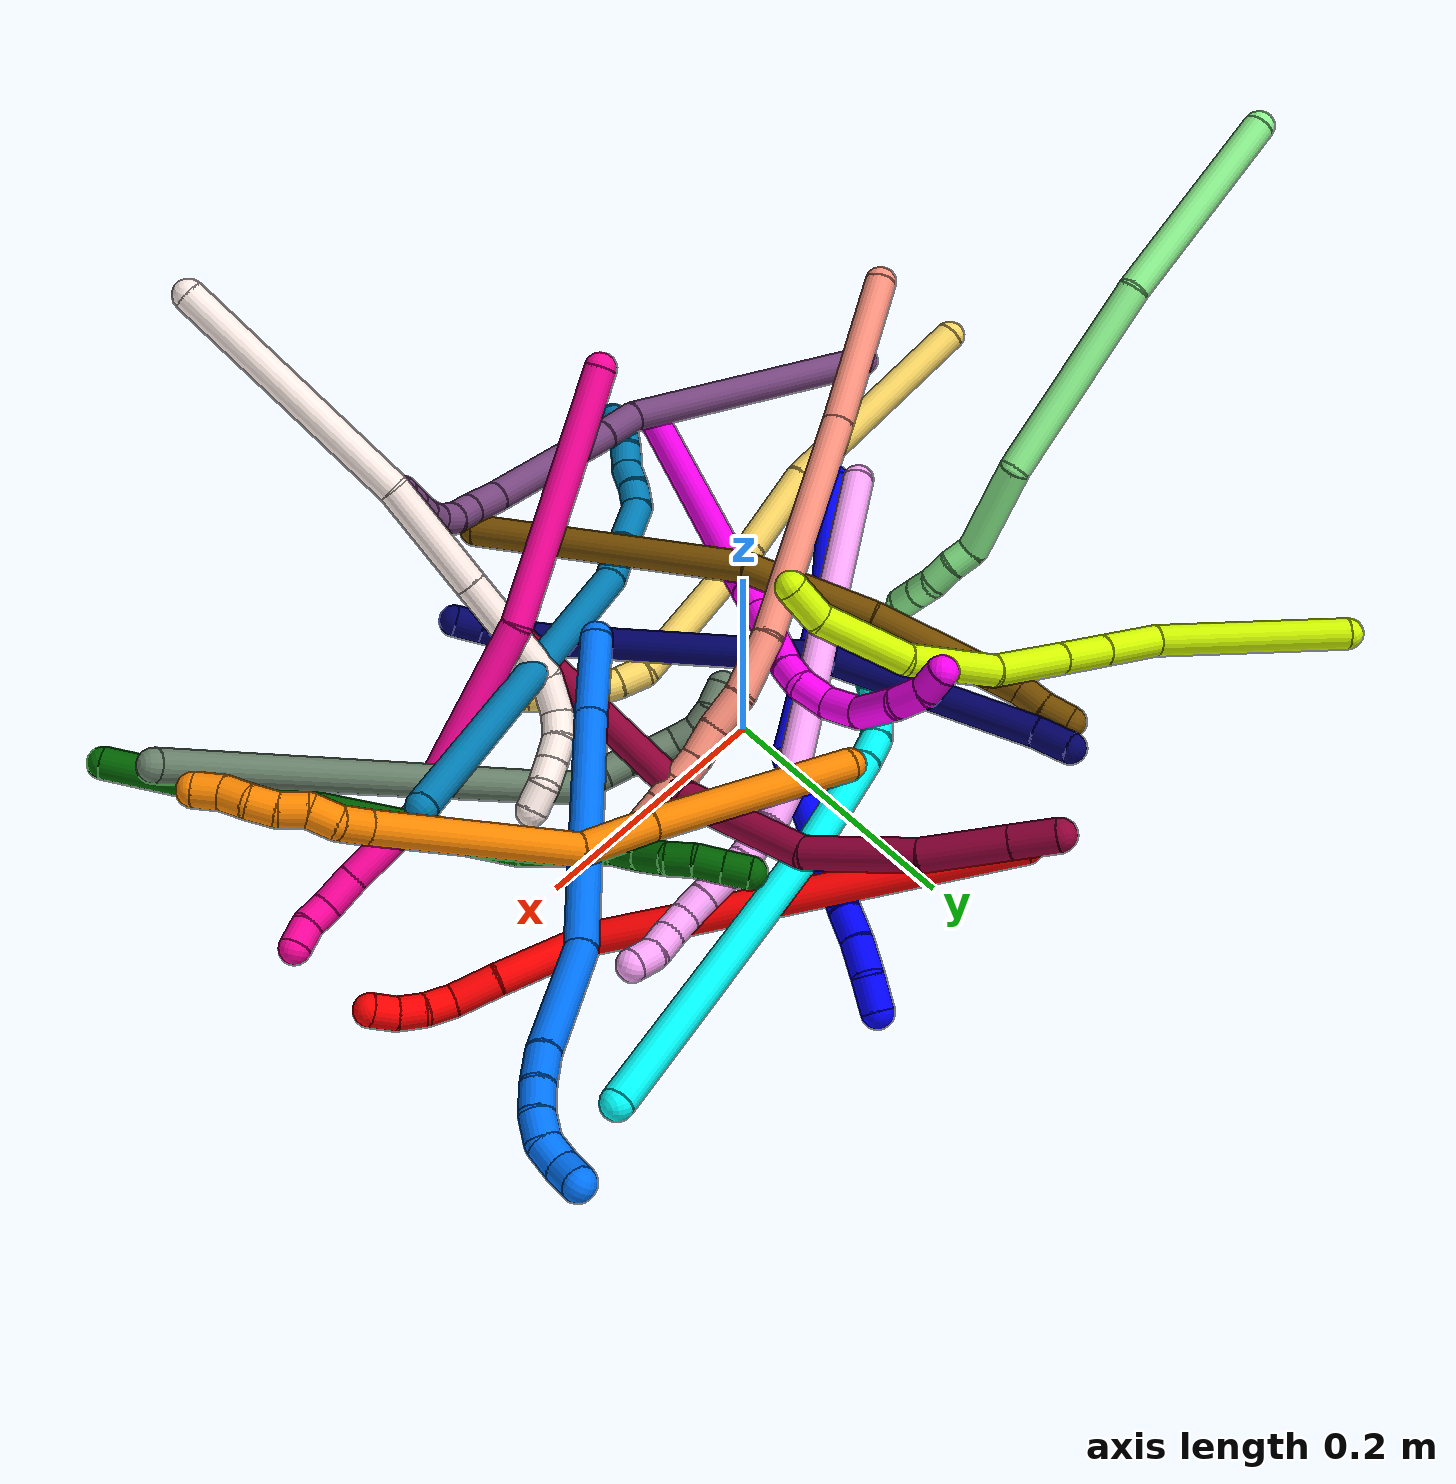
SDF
<sdf version="1.7">
 <world name="default">
  <plugin name="TubeGeneratorPlugin" filename="libtube_generator_plugin.so"/>
  <model name="photoneo_s_sensor">
   <static>1</static>
   <pose>0 0 2 1.57079 1.57079 3.14159</pose>
   <link name="link">
    <inertial><mass>0.1</mass></inertial>
    <sensor name="sensor" type="depth">
     <update_rate>30</update_rate>
     <camera>
      <horizontal_fov>1.22</horizontal_fov>
      <image><width>1920</width><height>1200</height><format>B8G8R8</format></image>
      <clip><near>0.1</near><far>4</far></clip>
      <depth_camera><output>points</output></depth_camera>
     </camera>
     <plugin name="camera_plugin" filename="libgazebo_ros_depth_camera.so">
      <baseline>0.2</baseline>
      <alwaysOn>1</alwaysOn>
      <updateRate>0.0</updateRate>
      <cameraName>camera_ir</cameraName>
      <imageTopicName>/camera/color/image_raw</imageTopicName>
      <cameraInfoTopicName>/camera/color/camera_info</cameraInfoTopicName>
      <depthImageTopicName>/camera/depth/image_raw</depthImageTopicName>
      <depthImageCameraInfoTopicName>/camera/depth/camera_info</depthImageCameraInfoTopicName>
      <pointCloudTopicName>/camera/depth/points</pointCloudTopicName>
      <frameName>fr_optical</frameName>
      <pointCloudCutoff>0.1</pointCloudCutoff>
      <pointCloudCutoffMax>2.0</pointCloudCutoffMax>
      <distortionK1>0</distortionK1>
      <distortionK2>0</distortionK2>
      <distortionK3>0</distortionK3>
      <distortionT1>0</distortionT1>
      <distortionT2>0</distortionT2>
      <CxPrime>0</CxPrime>
      <Cx>0</Cx>
      <Cy>0</Cy>
      <focalLength>0</focalLength>
      <hackBaseline>0</hackBaseline>
     </plugin>
    </sensor>
   </link>
  </model>
  <gravity>0 0 -9.8</gravity>
  <magnetic_field>6e-06 2.3e-05 -4.2e-05</magnetic_field>
  <atmosphere type="adiabatic"/>
  <physics name="default_physics" default="0" type="ode">
   <max_step_size>0.003</max_step_size>
   <real_time_factor>1</real_time_factor>
   <real_time_update_rate>1000</real_time_update_rate>
   <max_contacts>10000</max_contacts>
   <ode>
    <solver>
     <type>quick</type>
     <iters>100</iters>
     <sor>1.3</sor>
     <use_dynamic_moi_rescaling>0</use_dynamic_moi_rescaling>
    </solver>
    <constraints>
     <contact_max_correcting_vel>0</contact_max_correcting_vel>
     <contact_surface_layer>0.001</contact_surface_layer>
     <cfm>0</cfm>
     <erp>0.2</erp>
    </constraints>
   </ode>
  </physics>
  <scene><ambient>0.4 0.4 0.4 1</ambient><background>0.7 0.7 0.7 1</background><shadows>0</shadows></scene>
  <audio><device>default</device></audio>
  <spherical_coordinates>
   <surface_model>EARTH_WGS84</surface_model>
   <latitude_deg>0</latitude_deg>
   <longitude_deg>0</longitude_deg>
   <elevation>0</elevation>
   <heading_deg>0</heading_deg>
  </spherical_coordinates>
  <model name="bin">
   <static>1</static>
   <link name="bottom">
    <collision name="collision-bottom">
     <pose>0 0 -0.01 0 -0 0</pose>
     <geometry><box><size>0.8 0.6 0.02</size></box></geometry>
     <surface>
      <friction><ode><mu>100</mu><mu2>100</mu2></ode></friction>
      <contact><collide_bitmask>65535</collide_bitmask></contact>
     </surface>
    </collision>
   </link>
   <link name="west_wall">
    <collision name="collision-west_wall">
     <pose>-0.41 0 0.1 0 -0 0</pose>
     <geometry><box><size>0.02 0.6 0.2</size></box></geometry>
     <surface>
      <friction><ode><mu>100</mu><mu2>100</mu2></ode></friction>
      <contact><collide_bitmask>65535</collide_bitmask></contact>
     </surface>
    </collision>
   </link>
   <link name="east_wall">
    <collision name="collision-east_wall">
     <pose>0.41 0 0.1 0 -0 0</pose>
     <geometry><box><size>0.02 0.6 0.2</size></box></geometry>
     <surface>
      <friction><ode><mu>100</mu><mu2>100</mu2></ode></friction>
      <contact><collide_bitmask>65535</collide_bitmask></contact>
     </surface>
    </collision>
   </link>
   <link name="south_wall">
    <collision name="collision-south_wall">
     <pose>0 -0.31 0.1 0 -0 0</pose>
     <geometry><box><size>0.8 0.02 0.2</size></box></geometry>
     <surface>
      <friction><ode><mu>100</mu><mu2>100</mu2></ode></friction>
      <contact><collide_bitmask>65535</collide_bitmask></contact>
     </surface>
    </collision>
   </link>
   <link name="north_wall">
    <collision name="collision-north_wall">
     <pose>0 0.31 0.1 0 -0 0</pose>
     <geometry><box><size>0.8 0.02 0.2</size></box></geometry>
     <surface>
      <friction><ode><mu>100</mu><mu2>100</mu2></ode></friction>
      <contact><collide_bitmask>65535</collide_bitmask></contact>
     </surface>
    </collision>
   </link>
  </model>
  <model name="1">
   <static>0</static>
   <link name="1">
    <collision name="collision-cylinder-e_1_1_4">
     <pose>0.00017 0.049913 -0.037373 -2.21351 0.00273 -0.005455</pose>
     <geometry><cylinder><radius>0.0125</radius><length>0.124709</length></cylinder></geometry>
     <surface>
      <friction><ode><mu>1.16</mu><mu2>1.16</mu2><slip1>0</slip1><slip2>0</slip2></ode></friction>
      <contact><ode><kp>1e+06</kp><kd>1</kd><max_vel>0</max_vel><min_depth>0.001</min_depth></ode></contact>
     </surface>
    </collision>
    <visual name="visual-cylinder-e_1_1_4">
     <pose>0.00017 0.049913 -0.037373 -2.21351 0.00273 -0.005455</pose>
     <geometry><cylinder><radius>0.0125</radius><length>0.124709</length></cylinder></geometry>
     <material><ambient>0 0 1 1</ambient></material>
    </visual>
    <collision name="collision-cylinder-e_2_4_5">
     <pose>-0.004843 0.163602 -0.111821 -2.09738 -0.070147 0.121816</pose>
     <geometry><cylinder><radius>0.0125</radius><length>0.147902</length></cylinder></geometry>
     <surface>
      <friction><ode><mu>1.16</mu><mu2>1.16</mu2><slip1>0</slip1><slip2>0</slip2></ode></friction>
      <contact><ode><kp>1e+06</kp><kd>1</kd><max_vel>0</max_vel><min_depth>0.001</min_depth></ode></contact>
     </surface>
    </collision>
    <visual name="visual-cylinder-e_2_4_5">
     <pose>-0.004843 0.163602 -0.111821 -2.09738 -0.070147 0.121816</pose>
     <geometry><cylinder><radius>0.0125</radius><length>0.147902</length></cylinder></geometry>
     <material><ambient>0 0 1 1</ambient></material>
    </visual>
    <collision name="collision-cylinder-e_3_5_6">
     <pose>-0.002838 0.266967 -0.21059 -2.57107 0.09775 -0.330545</pose>
     <geometry><cylinder><radius>0.0125</radius><length>0.14731</length></cylinder></geometry>
     <surface>
      <friction><ode><mu>1.16</mu><mu2>1.16</mu2><slip1>0</slip1><slip2>0</slip2></ode></friction>
      <contact><ode><kp>1e+06</kp><kd>1</kd><max_vel>0</max_vel><min_depth>0.001</min_depth></ode></contact>
     </surface>
    </collision>
    <visual name="visual-cylinder-e_3_5_6">
     <pose>-0.002838 0.266967 -0.21059 -2.57107 0.09775 -0.330545</pose>
     <geometry><cylinder><radius>0.0125</radius><length>0.14731</length></cylinder></geometry>
     <material><ambient>0 0 1 1</ambient></material>
    </visual>
    <collision name="collision-cylinder-e_4_6_7">
     <pose>0.006806 0.313166 -0.282592 -2.57142 0.197856 -0.653076</pose>
     <geometry><cylinder><radius>0.0125</radius><length>0.024978</length></cylinder></geometry>
     <surface>
      <friction><ode><mu>1.16</mu><mu2>1.16</mu2><slip1>0</slip1><slip2>0</slip2></ode></friction>
      <contact><ode><kp>1e+06</kp><kd>1</kd><max_vel>0</max_vel><min_depth>0.001</min_depth></ode></contact>
     </surface>
    </collision>
    <visual name="visual-cylinder-e_4_6_7">
     <pose>0.006806 0.313166 -0.282592 -2.57142 0.197856 -0.653076</pose>
     <geometry><cylinder><radius>0.0125</radius><length>0.024978</length></cylinder></geometry>
     <material><ambient>0 0 1 1</ambient></material>
    </visual>
    <collision name="collision-cylinder-e_5_7_8">
     <pose>0.012743 0.328298 -0.303603 -2.46911 0.249205 -0.688203</pose>
     <geometry><cylinder><radius>0.0125</radius><length>0.028235</length></cylinder></geometry>
     <surface>
      <friction><ode><mu>1.16</mu><mu2>1.16</mu2><slip1>0</slip1><slip2>0</slip2></ode></friction>
      <contact><ode><kp>1e+06</kp><kd>1</kd><max_vel>0</max_vel><min_depth>0.001</min_depth></ode></contact>
     </surface>
    </collision>
    <visual name="visual-cylinder-e_5_7_8">
     <pose>0.012743 0.328298 -0.303603 -2.46911 0.249205 -0.688203</pose>
     <geometry><cylinder><radius>0.0125</radius><length>0.028235</length></cylinder></geometry>
     <material><ambient>0 0 1 1</ambient></material>
    </visual>
    <collision name="collision-cylinder-e_6_8_2">
     <pose>0.022868 0.345298 -0.322333 -2.32893 0.517346 -1.10268</pose>
     <geometry><cylinder><radius>0.0125</radius><length>0.026865</length></cylinder></geometry>
     <surface>
      <friction><ode><mu>1.16</mu><mu2>1.16</mu2><slip1>0</slip1><slip2>0</slip2></ode></friction>
      <contact><ode><kp>1e+06</kp><kd>1</kd><max_vel>0</max_vel><min_depth>0.001</min_depth></ode></contact>
     </surface>
    </collision>
    <visual name="visual-cylinder-e_6_8_2">
     <pose>0.022868 0.345298 -0.322333 -2.32893 0.517346 -1.10268</pose>
     <geometry><cylinder><radius>0.0125</radius><length>0.026865</length></cylinder></geometry>
     <material><ambient>0 0 1 1</ambient></material>
    </visual>
    <collision name="collision-sphere-2">
     <pose>0.029511 0.353775 -0.33036 0 -0 0</pose>
     <geometry><sphere><radius>0.0125</radius></sphere></geometry>
     <surface>
      <friction><ode><mu>1.16</mu><mu2>1.16</mu2><slip1>0</slip1><slip2>0</slip2></ode></friction>
      <contact><ode><kp>1e+06</kp><kd>1</kd><max_vel>0</max_vel><min_depth>0.001</min_depth></ode></contact>
     </surface>
    </collision>
    <visual name="visual-sphere-2">
     <pose>0.029511 0.353775 -0.33036 0 -0 0</pose>
     <geometry><sphere><radius>0.0125</radius></sphere></geometry>
     <material><ambient>0 0 1 1</ambient></material>
    </visual>
    <collision name="collision-sphere-4">
     <pose>0.00034 0.099826 -0.074746 0 -0 0</pose>
     <geometry><sphere><radius>0.0125</radius></sphere></geometry>
     <surface>
      <friction><ode><mu>1.16</mu><mu2>1.16</mu2><slip1>0</slip1><slip2>0</slip2></ode></friction>
      <contact><ode><kp>1e+06</kp><kd>1</kd><max_vel>0</max_vel><min_depth>0.001</min_depth></ode></contact>
     </surface>
    </collision>
    <visual name="visual-sphere-4">
     <pose>0.00034 0.099826 -0.074746 0 -0 0</pose>
     <geometry><sphere><radius>0.0125</radius></sphere></geometry>
     <material><ambient>0 0 1 1</ambient></material>
    </visual>
    <collision name="collision-sphere-1">
     <geometry><sphere><radius>0.0125</radius></sphere></geometry>
     <surface>
      <friction><ode><mu>1.16</mu><mu2>1.16</mu2><slip1>0</slip1><slip2>0</slip2></ode></friction>
      <contact><ode><kp>1e+06</kp><kd>1</kd><max_vel>0</max_vel><min_depth>0.001</min_depth></ode></contact>
     </surface>
    </collision>
    <visual name="visual-sphere-1">
     <geometry><sphere><radius>0.0125</radius></sphere></geometry>
     <material><ambient>0 0 1 1</ambient></material>
    </visual>
    <collision name="collision-sphere-8">
     <pose>0.016224 0.336821 -0.314306 0 -0 0</pose>
     <geometry><sphere><radius>0.0125</radius></sphere></geometry>
     <surface>
      <friction><ode><mu>1.16</mu><mu2>1.16</mu2><slip1>0</slip1><slip2>0</slip2></ode></friction>
      <contact><ode><kp>1e+06</kp><kd>1</kd><max_vel>0</max_vel><min_depth>0.001</min_depth></ode></contact>
     </surface>
    </collision>
    <visual name="visual-sphere-8">
     <pose>0.016224 0.336821 -0.314306 0 -0 0</pose>
     <geometry><sphere><radius>0.0125</radius></sphere></geometry>
     <material><ambient>0 0 1 1</ambient></material>
    </visual>
    <collision name="collision-sphere-5">
     <pose>-0.010026 0.227378 -0.148896 0 -0 0</pose>
     <geometry><sphere><radius>0.0125</radius></sphere></geometry>
     <surface>
      <friction><ode><mu>1.16</mu><mu2>1.16</mu2><slip1>0</slip1><slip2>0</slip2></ode></friction>
      <contact><ode><kp>1e+06</kp><kd>1</kd><max_vel>0</max_vel><min_depth>0.001</min_depth></ode></contact>
     </surface>
    </collision>
    <visual name="visual-sphere-5">
     <pose>-0.010026 0.227378 -0.148896 0 -0 0</pose>
     <geometry><sphere><radius>0.0125</radius></sphere></geometry>
     <material><ambient>0 0 1 1</ambient></material>
    </visual>
    <collision name="collision-sphere-6">
     <pose>0.004351 0.306556 -0.272283 0 -0 0</pose>
     <geometry><sphere><radius>0.0125</radius></sphere></geometry>
     <surface>
      <friction><ode><mu>1.16</mu><mu2>1.16</mu2><slip1>0</slip1><slip2>0</slip2></ode></friction>
      <contact><ode><kp>1e+06</kp><kd>1</kd><max_vel>0</max_vel><min_depth>0.001</min_depth></ode></contact>
     </surface>
    </collision>
    <visual name="visual-sphere-6">
     <pose>0.004351 0.306556 -0.272283 0 -0 0</pose>
     <geometry><sphere><radius>0.0125</radius></sphere></geometry>
     <material><ambient>0 0 1 1</ambient></material>
    </visual>
    <collision name="collision-sphere-7">
     <pose>0.009261 0.319776 -0.2929 0 -0 0</pose>
     <geometry><sphere><radius>0.0125</radius></sphere></geometry>
     <surface>
      <friction><ode><mu>1.16</mu><mu2>1.16</mu2><slip1>0</slip1><slip2>0</slip2></ode></friction>
      <contact><ode><kp>1e+06</kp><kd>1</kd><max_vel>0</max_vel><min_depth>0.001</min_depth></ode></contact>
     </surface>
    </collision>
    <visual name="visual-sphere-7">
     <pose>0.009261 0.319776 -0.2929 0 -0 0</pose>
     <geometry><sphere><radius>0.0125</radius></sphere></geometry>
     <material><ambient>0 0 1 1</ambient></material>
    </visual>
    <inertial>
     <pose>6.2e-05 0.192234 -0.153024 0 -0 0</pose>
     <mass>0.5</mass>
     <inertia>
      <ixx>0.000642</ixx>
      <ixy>0</ixy>
      <ixz>0</ixz>
      <iyy>-0.000483</iyy>
      <iyz>0</iyz>
      <izz>-0.000558</izz>
     </inertia>
    </inertial>
   </link>
   <pose>-0.219983 -0.113507 0.011872 -2.49761 1.05943 2.27583</pose>
  </model>
  <model name="2">
   <static>0</static>
   <link name="2">
    <collision name="collision-cylinder-e_1_1_4">
     <pose>0.087385 -0.089154 -0.018681 1.77735 0.764645 0.919436</pose>
     <geometry><cylinder><radius>0.0125</radius><length>0.252456</length></cylinder></geometry>
     <surface>
      <friction><ode><mu>1.16</mu><mu2>1.16</mu2><slip1>0</slip1><slip2>0</slip2></ode></friction>
      <contact><ode><kp>1e+06</kp><kd>1</kd><max_vel>0</max_vel><min_depth>0.001</min_depth></ode></contact>
     </surface>
    </collision>
    <visual name="visual-cylinder-e_1_1_4">
     <pose>0.087385 -0.089154 -0.018681 1.77735 0.764645 0.919436</pose>
     <geometry><cylinder><radius>0.0125</radius><length>0.252456</length></cylinder></geometry>
     <material><ambient>1 0 0 1</ambient></material>
    </visual>
    <collision name="collision-cylinder-e_2_4_5">
     <pose>0.20015 -0.203439 -0.042627 1.77731 0.779574 0.936532</pose>
     <geometry><cylinder><radius>0.0125</radius><length>0.072207</length></cylinder></geometry>
     <surface>
      <friction><ode><mu>1.16</mu><mu2>1.16</mu2><slip1>0</slip1><slip2>0</slip2></ode></friction>
      <contact><ode><kp>1e+06</kp><kd>1</kd><max_vel>0</max_vel><min_depth>0.001</min_depth></ode></contact>
     </surface>
    </collision>
    <visual name="visual-cylinder-e_2_4_5">
     <pose>0.20015 -0.203439 -0.042627 1.77731 0.779574 0.936532</pose>
     <geometry><cylinder><radius>0.0125</radius><length>0.072207</length></cylinder></geometry>
     <material><ambient>1 0 0 1</ambient></material>
    </visual>
    <collision name="collision-cylinder-e_3_5_6">
     <pose>0.23873 -0.263422 -0.058104 1.85584 0.348614 0.461808</pose>
     <geometry><cylinder><radius>0.0125</radius><length>0.077281</length></cylinder></geometry>
     <surface>
      <friction><ode><mu>1.16</mu><mu2>1.16</mu2><slip1>0</slip1><slip2>0</slip2></ode></friction>
      <contact><ode><kp>1e+06</kp><kd>1</kd><max_vel>0</max_vel><min_depth>0.001</min_depth></ode></contact>
     </surface>
    </collision>
    <visual name="visual-cylinder-e_3_5_6">
     <pose>0.23873 -0.263422 -0.058104 1.85584 0.348614 0.461808</pose>
     <geometry><cylinder><radius>0.0125</radius><length>0.077281</length></cylinder></geometry>
     <material><ambient>1 0 0 1</ambient></material>
    </visual>
    <collision name="collision-cylinder-e_4_6_7">
     <pose>0.259366 -0.31421 -0.07107 1.74186 0.430955 0.508605</pose>
     <geometry><cylinder><radius>0.0125</radius><length>0.035603</length></cylinder></geometry>
     <surface>
      <friction><ode><mu>1.16</mu><mu2>1.16</mu2><slip1>0</slip1><slip2>0</slip2></ode></friction>
      <contact><ode><kp>1e+06</kp><kd>1</kd><max_vel>0</max_vel><min_depth>0.001</min_depth></ode></contact>
     </surface>
    </collision>
    <visual name="visual-cylinder-e_4_6_7">
     <pose>0.259366 -0.31421 -0.07107 1.74186 0.430955 0.508605</pose>
     <geometry><cylinder><radius>0.0125</radius><length>0.035603</length></cylinder></geometry>
     <material><ambient>1 0 0 1</ambient></material>
    </visual>
    <collision name="collision-cylinder-e_5_7_8">
     <pose>0.269559 -0.339489 -0.078681 2.05036 0.256098 0.417973</pose>
     <geometry><cylinder><radius>0.0125</radius><length>0.021769</length></cylinder></geometry>
     <surface>
      <friction><ode><mu>1.16</mu><mu2>1.16</mu2><slip1>0</slip1><slip2>0</slip2></ode></friction>
      <contact><ode><kp>1e+06</kp><kd>1</kd><max_vel>0</max_vel><min_depth>0.001</min_depth></ode></contact>
     </surface>
    </collision>
    <visual name="visual-cylinder-e_5_7_8">
     <pose>0.269559 -0.339489 -0.078681 2.05036 0.256098 0.417973</pose>
     <geometry><cylinder><radius>0.0125</radius><length>0.021769</length></cylinder></geometry>
     <material><ambient>1 0 0 1</ambient></material>
    </visual>
    <collision name="collision-cylinder-e_6_8_9">
     <pose>0.277186 -0.356533 -0.088141 2.10937 0.497253 0.841443</pose>
     <geometry><cylinder><radius>0.0125</radius><length>0.020417</length></cylinder></geometry>
     <surface>
      <friction><ode><mu>1.16</mu><mu2>1.16</mu2><slip1>0</slip1><slip2>0</slip2></ode></friction>
      <contact><ode><kp>1e+06</kp><kd>1</kd><max_vel>0</max_vel><min_depth>0.001</min_depth></ode></contact>
     </surface>
    </collision>
    <visual name="visual-cylinder-e_6_8_9">
     <pose>0.277186 -0.356533 -0.088141 2.10937 0.497253 0.841443</pose>
     <geometry><cylinder><radius>0.0125</radius><length>0.020417</length></cylinder></geometry>
     <material><ambient>1 0 0 1</ambient></material>
    </visual>
    <collision name="collision-cylinder-e_7_9_2">
     <pose>0.28617 -0.370036 -0.099962 2.4647 0.41811 1.08485</pose>
     <geometry><cylinder><radius>0.0125</radius><length>0.020267</length></cylinder></geometry>
     <surface>
      <friction><ode><mu>1.16</mu><mu2>1.16</mu2><slip1>0</slip1><slip2>0</slip2></ode></friction>
      <contact><ode><kp>1e+06</kp><kd>1</kd><max_vel>0</max_vel><min_depth>0.001</min_depth></ode></contact>
     </surface>
    </collision>
    <visual name="visual-cylinder-e_7_9_2">
     <pose>0.28617 -0.370036 -0.099962 2.4647 0.41811 1.08485</pose>
     <geometry><cylinder><radius>0.0125</radius><length>0.020267</length></cylinder></geometry>
     <material><ambient>1 0 0 1</ambient></material>
    </visual>
    <collision name="collision-sphere-2">
     <pose>0.290284 -0.375837 -0.107181 0 -0 0</pose>
     <geometry><sphere><radius>0.0125</radius></sphere></geometry>
     <surface>
      <friction><ode><mu>1.16</mu><mu2>1.16</mu2><slip1>0</slip1><slip2>0</slip2></ode></friction>
      <contact><ode><kp>1e+06</kp><kd>1</kd><max_vel>0</max_vel><min_depth>0.001</min_depth></ode></contact>
     </surface>
    </collision>
    <visual name="visual-sphere-2">
     <pose>0.290284 -0.375837 -0.107181 0 -0 0</pose>
     <geometry><sphere><radius>0.0125</radius></sphere></geometry>
     <material><ambient>1 0 0 1</ambient></material>
    </visual>
    <collision name="collision-sphere-9">
     <pose>0.282055 -0.364236 -0.092743 0 -0 0</pose>
     <geometry><sphere><radius>0.0125</radius></sphere></geometry>
     <surface>
      <friction><ode><mu>1.16</mu><mu2>1.16</mu2><slip1>0</slip1><slip2>0</slip2></ode></friction>
      <contact><ode><kp>1e+06</kp><kd>1</kd><max_vel>0</max_vel><min_depth>0.001</min_depth></ode></contact>
     </surface>
    </collision>
    <visual name="visual-sphere-9">
     <pose>0.282055 -0.364236 -0.092743 0 -0 0</pose>
     <geometry><sphere><radius>0.0125</radius></sphere></geometry>
     <material><ambient>1 0 0 1</ambient></material>
    </visual>
    <collision name="collision-sphere-4">
     <pose>0.17477 -0.178307 -0.037362 0 -0 0</pose>
     <geometry><sphere><radius>0.0125</radius></sphere></geometry>
     <surface>
      <friction><ode><mu>1.16</mu><mu2>1.16</mu2><slip1>0</slip1><slip2>0</slip2></ode></friction>
      <contact><ode><kp>1e+06</kp><kd>1</kd><max_vel>0</max_vel><min_depth>0.001</min_depth></ode></contact>
     </surface>
    </collision>
    <visual name="visual-sphere-4">
     <pose>0.17477 -0.178307 -0.037362 0 -0 0</pose>
     <geometry><sphere><radius>0.0125</radius></sphere></geometry>
     <material><ambient>1 0 0 1</ambient></material>
    </visual>
    <collision name="collision-sphere-1">
     <geometry><sphere><radius>0.0125</radius></sphere></geometry>
     <surface>
      <friction><ode><mu>1.16</mu><mu2>1.16</mu2><slip1>0</slip1><slip2>0</slip2></ode></friction>
      <contact><ode><kp>1e+06</kp><kd>1</kd><max_vel>0</max_vel><min_depth>0.001</min_depth></ode></contact>
     </surface>
    </collision>
    <visual name="visual-sphere-1">
     <geometry><sphere><radius>0.0125</radius></sphere></geometry>
     <material><ambient>1 0 0 1</ambient></material>
    </visual>
    <collision name="collision-sphere-8">
     <pose>0.272316 -0.348831 -0.083539 0 -0 0</pose>
     <geometry><sphere><radius>0.0125</radius></sphere></geometry>
     <surface>
      <friction><ode><mu>1.16</mu><mu2>1.16</mu2><slip1>0</slip1><slip2>0</slip2></ode></friction>
      <contact><ode><kp>1e+06</kp><kd>1</kd><max_vel>0</max_vel><min_depth>0.001</min_depth></ode></contact>
     </surface>
    </collision>
    <visual name="visual-sphere-8">
     <pose>0.272316 -0.348831 -0.083539 0 -0 0</pose>
     <geometry><sphere><radius>0.0125</radius></sphere></geometry>
     <material><ambient>1 0 0 1</ambient></material>
    </visual>
    <collision name="collision-sphere-5">
     <pose>0.22553 -0.228571 -0.047892 0 -0 0</pose>
     <geometry><sphere><radius>0.0125</radius></sphere></geometry>
     <surface>
      <friction><ode><mu>1.16</mu><mu2>1.16</mu2><slip1>0</slip1><slip2>0</slip2></ode></friction>
      <contact><ode><kp>1e+06</kp><kd>1</kd><max_vel>0</max_vel><min_depth>0.001</min_depth></ode></contact>
     </surface>
    </collision>
    <visual name="visual-sphere-5">
     <pose>0.22553 -0.228571 -0.047892 0 -0 0</pose>
     <geometry><sphere><radius>0.0125</radius></sphere></geometry>
     <material><ambient>1 0 0 1</ambient></material>
    </visual>
    <collision name="collision-sphere-6">
     <pose>0.251929 -0.298272 -0.068316 0 -0 0</pose>
     <geometry><sphere><radius>0.0125</radius></sphere></geometry>
     <surface>
      <friction><ode><mu>1.16</mu><mu2>1.16</mu2><slip1>0</slip1><slip2>0</slip2></ode></friction>
      <contact><ode><kp>1e+06</kp><kd>1</kd><max_vel>0</max_vel><min_depth>0.001</min_depth></ode></contact>
     </surface>
    </collision>
    <visual name="visual-sphere-6">
     <pose>0.251929 -0.298272 -0.068316 0 -0 0</pose>
     <geometry><sphere><radius>0.0125</radius></sphere></geometry>
     <material><ambient>1 0 0 1</ambient></material>
    </visual>
    <collision name="collision-sphere-7">
     <pose>0.266802 -0.330148 -0.073823 0 -0 0</pose>
     <geometry><sphere><radius>0.0125</radius></sphere></geometry>
     <surface>
      <friction><ode><mu>1.16</mu><mu2>1.16</mu2><slip1>0</slip1><slip2>0</slip2></ode></friction>
      <contact><ode><kp>1e+06</kp><kd>1</kd><max_vel>0</max_vel><min_depth>0.001</min_depth></ode></contact>
     </surface>
    </collision>
    <visual name="visual-sphere-7">
     <pose>0.266802 -0.330148 -0.073823 0 -0 0</pose>
     <geometry><sphere><radius>0.0125</radius></sphere></geometry>
     <material><ambient>1 0 0 1</ambient></material>
    </visual>
    <inertial>
     <pose>0.163048 -0.181821 -0.040706 0 -0 0</pose>
     <mass>0.5</mass>
     <inertia>
      <ixx>0.001487</ixx>
      <ixy>0</ixy>
      <ixz>0</ixz>
      <iyy>0.001358</iyy>
      <iyz>0</iyz>
      <izz>3.8e-05</izz>
     </inertia>
    </inertial>
   </link>
   <pose>-0.039913 0.249769 0.074961 3.06753 0.418776 -1.47309</pose>
  </model>
  <model name="3">
   <static>0</static>
   <link name="3">
    <collision name="collision-cylinder-e_1_1_4">
     <pose>0.001723 -0.049345 0.125041 0.375868 0.012813 0.002437</pose>
     <geometry><cylinder><radius>0.0125</radius><length>0.268874</length></cylinder></geometry>
     <surface>
      <friction><ode><mu>1.16</mu><mu2>1.16</mu2><slip1>0</slip1><slip2>0</slip2></ode></friction>
      <contact><ode><kp>1e+06</kp><kd>1</kd><max_vel>0</max_vel><min_depth>0.001</min_depth></ode></contact>
     </surface>
    </collision>
    <visual name="visual-cylinder-e_1_1_4">
     <pose>0.001723 -0.049345 0.125041 0.375868 0.012813 0.002437</pose>
     <geometry><cylinder><radius>0.0125</radius><length>0.268874</length></cylinder></geometry>
     <material><ambient>0.003922 1 0.996078 1</ambient></material>
    </visual>
    <collision name="collision-cylinder-e_2_4_5">
     <pose>0.001564 -0.119449 0.295153 0.431629 -0.037897 -0.008309</pose>
     <geometry><cylinder><radius>0.0125</radius><length>0.099312</length></cylinder></geometry>
     <surface>
      <friction><ode><mu>1.16</mu><mu2>1.16</mu2><slip1>0</slip1><slip2>0</slip2></ode></friction>
      <contact><ode><kp>1e+06</kp><kd>1</kd><max_vel>0</max_vel><min_depth>0.001</min_depth></ode></contact>
     </surface>
    </collision>
    <visual name="visual-cylinder-e_2_4_5">
     <pose>0.001564 -0.119449 0.295153 0.431629 -0.037897 -0.008309</pose>
     <geometry><cylinder><radius>0.0125</radius><length>0.099312</length></cylinder></geometry>
     <material><ambient>0.003922 1 0.996078 1</ambient></material>
    </visual>
    <collision name="collision-cylinder-e_3_5_6">
     <pose>-0.001742 -0.146636 0.352458 0.483773 -0.102674 -0.025352</pose>
     <geometry><cylinder><radius>0.0125</radius><length>0.02779</length></cylinder></geometry>
     <surface>
      <friction><ode><mu>1.16</mu><mu2>1.16</mu2><slip1>0</slip1><slip2>0</slip2></ode></friction>
      <contact><ode><kp>1e+06</kp><kd>1</kd><max_vel>0</max_vel><min_depth>0.001</min_depth></ode></contact>
     </surface>
    </collision>
    <visual name="visual-cylinder-e_3_5_6">
     <pose>-0.001742 -0.146636 0.352458 0.483773 -0.102674 -0.025352</pose>
     <geometry><cylinder><radius>0.0125</radius><length>0.02779</length></cylinder></geometry>
     <material><ambient>0.003922 1 0.996078 1</ambient></material>
    </visual>
    <collision name="collision-cylinder-e_4_6_7">
     <pose>-0.006181 -0.165186 0.376831 0.784731 -0.174015 -0.072162</pose>
     <geometry><cylinder><radius>0.0125</radius><length>0.034832</length></cylinder></geometry>
     <surface>
      <friction><ode><mu>1.16</mu><mu2>1.16</mu2><slip1>0</slip1><slip2>0</slip2></ode></friction>
      <contact><ode><kp>1e+06</kp><kd>1</kd><max_vel>0</max_vel><min_depth>0.001</min_depth></ode></contact>
     </surface>
    </collision>
    <visual name="visual-cylinder-e_4_6_7">
     <pose>-0.006181 -0.165186 0.376831 0.784731 -0.174015 -0.072162</pose>
     <geometry><cylinder><radius>0.0125</radius><length>0.034832</length></cylinder></geometry>
     <material><ambient>0.003922 1 0.996078 1</ambient></material>
    </visual>
    <collision name="collision-cylinder-e_5_7_8">
     <pose>-0.01451 -0.184579 0.396211 0.787406 -0.477713 -0.201614</pose>
     <geometry><cylinder><radius>0.0125</radius><length>0.023116</length></cylinder></geometry>
     <surface>
      <friction><ode><mu>1.16</mu><mu2>1.16</mu2><slip1>0</slip1><slip2>0</slip2></ode></friction>
      <contact><ode><kp>1e+06</kp><kd>1</kd><max_vel>0</max_vel><min_depth>0.001</min_depth></ode></contact>
     </surface>
    </collision>
    <visual name="visual-cylinder-e_5_7_8">
     <pose>-0.01451 -0.184579 0.396211 0.787406 -0.477713 -0.201614</pose>
     <geometry><cylinder><radius>0.0125</radius><length>0.023116</length></cylinder></geometry>
     <material><ambient>0.003922 1 0.996078 1</ambient></material>
    </visual>
    <collision name="collision-cylinder-e_6_8_9">
     <pose>-0.021619 -0.202743 0.408472 1.13907 -0.148546 -0.095219</pose>
     <geometry><cylinder><radius>0.0125</radius><length>0.024251</length></cylinder></geometry>
     <surface>
      <friction><ode><mu>1.16</mu><mu2>1.16</mu2><slip1>0</slip1><slip2>0</slip2></ode></friction>
      <contact><ode><kp>1e+06</kp><kd>1</kd><max_vel>0</max_vel><min_depth>0.001</min_depth></ode></contact>
     </surface>
    </collision>
    <visual name="visual-cylinder-e_6_8_9">
     <pose>-0.021619 -0.202743 0.408472 1.13907 -0.148546 -0.095219</pose>
     <geometry><cylinder><radius>0.0125</radius><length>0.024251</length></cylinder></geometry>
     <material><ambient>0.003922 1 0.996078 1</ambient></material>
    </visual>
    <collision name="collision-cylinder-e_7_9_2">
     <pose>-0.024044 -0.223544 0.418018 1.14211 -0.057795 -0.037137</pose>
     <geometry><cylinder><radius>0.0125</radius><length>0.021825</length></cylinder></geometry>
     <surface>
      <friction><ode><mu>1.16</mu><mu2>1.16</mu2><slip1>0</slip1><slip2>0</slip2></ode></friction>
      <contact><ode><kp>1e+06</kp><kd>1</kd><max_vel>0</max_vel><min_depth>0.001</min_depth></ode></contact>
     </surface>
    </collision>
    <visual name="visual-cylinder-e_7_9_2">
     <pose>-0.024044 -0.223544 0.418018 1.14211 -0.057795 -0.037137</pose>
     <geometry><cylinder><radius>0.0125</radius><length>0.021825</length></cylinder></geometry>
     <material><ambient>0.003922 1 0.996078 1</ambient></material>
    </visual>
    <collision name="collision-sphere-2">
     <pose>-0.024674 -0.233452 0.422547 0 -0 0</pose>
     <geometry><sphere><radius>0.0125</radius></sphere></geometry>
     <surface>
      <friction><ode><mu>1.16</mu><mu2>1.16</mu2><slip1>0</slip1><slip2>0</slip2></ode></friction>
      <contact><ode><kp>1e+06</kp><kd>1</kd><max_vel>0</max_vel><min_depth>0.001</min_depth></ode></contact>
     </surface>
    </collision>
    <visual name="visual-sphere-2">
     <pose>-0.024674 -0.233452 0.422547 0 -0 0</pose>
     <geometry><sphere><radius>0.0125</radius></sphere></geometry>
     <material><ambient>0.003922 1 0.996078 1</ambient></material>
    </visual>
    <collision name="collision-sphere-9">
     <pose>-0.023413 -0.213635 0.41349 0 -0 0</pose>
     <geometry><sphere><radius>0.0125</radius></sphere></geometry>
     <surface>
      <friction><ode><mu>1.16</mu><mu2>1.16</mu2><slip1>0</slip1><slip2>0</slip2></ode></friction>
      <contact><ode><kp>1e+06</kp><kd>1</kd><max_vel>0</max_vel><min_depth>0.001</min_depth></ode></contact>
     </surface>
    </collision>
    <visual name="visual-sphere-9">
     <pose>-0.023413 -0.213635 0.41349 0 -0 0</pose>
     <geometry><sphere><radius>0.0125</radius></sphere></geometry>
     <material><ambient>0.003922 1 0.996078 1</ambient></material>
    </visual>
    <collision name="collision-sphere-4">
     <pose>0.003445 -0.09869 0.250083 0 -0 0</pose>
     <geometry><sphere><radius>0.0125</radius></sphere></geometry>
     <surface>
      <friction><ode><mu>1.16</mu><mu2>1.16</mu2><slip1>0</slip1><slip2>0</slip2></ode></friction>
      <contact><ode><kp>1e+06</kp><kd>1</kd><max_vel>0</max_vel><min_depth>0.001</min_depth></ode></contact>
     </surface>
    </collision>
    <visual name="visual-sphere-4">
     <pose>0.003445 -0.09869 0.250083 0 -0 0</pose>
     <geometry><sphere><radius>0.0125</radius></sphere></geometry>
     <material><ambient>0.003922 1 0.996078 1</ambient></material>
    </visual>
    <collision name="collision-sphere-1">
     <geometry><sphere><radius>0.0125</radius></sphere></geometry>
     <surface>
      <friction><ode><mu>1.16</mu><mu2>1.16</mu2><slip1>0</slip1><slip2>0</slip2></ode></friction>
      <contact><ode><kp>1e+06</kp><kd>1</kd><max_vel>0</max_vel><min_depth>0.001</min_depth></ode></contact>
     </surface>
    </collision>
    <visual name="visual-sphere-1">
     <geometry><sphere><radius>0.0125</radius></sphere></geometry>
     <material><ambient>0.003922 1 0.996078 1</ambient></material>
    </visual>
    <collision name="collision-sphere-8">
     <pose>-0.019824 -0.191852 0.403454 0 -0 0</pose>
     <geometry><sphere><radius>0.0125</radius></sphere></geometry>
     <surface>
      <friction><ode><mu>1.16</mu><mu2>1.16</mu2><slip1>0</slip1><slip2>0</slip2></ode></friction>
      <contact><ode><kp>1e+06</kp><kd>1</kd><max_vel>0</max_vel><min_depth>0.001</min_depth></ode></contact>
     </surface>
    </collision>
    <visual name="visual-sphere-8">
     <pose>-0.019824 -0.191852 0.403454 0 -0 0</pose>
     <geometry><sphere><radius>0.0125</radius></sphere></geometry>
     <material><ambient>0.003922 1 0.996078 1</ambient></material>
    </visual>
    <collision name="collision-sphere-5">
     <pose>-0.000318 -0.140208 0.340222 0 -0 0</pose>
     <geometry><sphere><radius>0.0125</radius></sphere></geometry>
     <surface>
      <friction><ode><mu>1.16</mu><mu2>1.16</mu2><slip1>0</slip1><slip2>0</slip2></ode></friction>
      <contact><ode><kp>1e+06</kp><kd>1</kd><max_vel>0</max_vel><min_depth>0.001</min_depth></ode></contact>
     </surface>
    </collision>
    <visual name="visual-sphere-5">
     <pose>-0.000318 -0.140208 0.340222 0 -0 0</pose>
     <geometry><sphere><radius>0.0125</radius></sphere></geometry>
     <material><ambient>0.003922 1 0.996078 1</ambient></material>
    </visual>
    <collision name="collision-sphere-6">
     <pose>-0.003166 -0.153065 0.364693 0 -0 0</pose>
     <geometry><sphere><radius>0.0125</radius></sphere></geometry>
     <surface>
      <friction><ode><mu>1.16</mu><mu2>1.16</mu2><slip1>0</slip1><slip2>0</slip2></ode></friction>
      <contact><ode><kp>1e+06</kp><kd>1</kd><max_vel>0</max_vel><min_depth>0.001</min_depth></ode></contact>
     </surface>
    </collision>
    <visual name="visual-sphere-6">
     <pose>-0.003166 -0.153065 0.364693 0 -0 0</pose>
     <geometry><sphere><radius>0.0125</radius></sphere></geometry>
     <material><ambient>0.003922 1 0.996078 1</ambient></material>
    </visual>
    <collision name="collision-sphere-7">
     <pose>-0.009197 -0.177307 0.388968 0 -0 0</pose>
     <geometry><sphere><radius>0.0125</radius></sphere></geometry>
     <surface>
      <friction><ode><mu>1.16</mu><mu2>1.16</mu2><slip1>0</slip1><slip2>0</slip2></ode></friction>
      <contact><ode><kp>1e+06</kp><kd>1</kd><max_vel>0</max_vel><min_depth>0.001</min_depth></ode></contact>
     </surface>
    </collision>
    <visual name="visual-sphere-7">
     <pose>-0.009197 -0.177307 0.388968 0 -0 0</pose>
     <geometry><sphere><radius>0.0125</radius></sphere></geometry>
     <material><ambient>0.003922 1 0.996078 1</ambient></material>
    </visual>
    <inertial>
     <pose>-0.002059 -0.098043 0.228082 0 -0 0</pose>
     <mass>0.5</mass>
     <inertia>
      <ixx>0.001729</ixx>
      <ixy>0</ixy>
      <ixz>0</ixz>
      <iyy>0.001587</iyy>
      <iyz>0</iyz>
      <izz>0.000661</izz>
     </inertia>
    </inertial>
   </link>
   <pose>0.318278 0.198905 0.116291 -2.40014 -1.02735 2.22705</pose>
  </model>
  <model name="4">
   <static>0</static>
   <link name="4">
    <collision name="collision-cylinder-e_1_1_4">
     <pose>0.111063 0.107108 0.001743 -1.55452 0.80346 -0.791812</pose>
     <geometry><cylinder><radius>0.0125</radius><length>0.308612</length></cylinder></geometry>
     <surface>
      <friction><ode><mu>1.16</mu><mu2>1.16</mu2><slip1>0</slip1><slip2>0</slip2></ode></friction>
      <contact><ode><kp>1e+06</kp><kd>1</kd><max_vel>0</max_vel><min_depth>0.001</min_depth></ode></contact>
     </surface>
    </collision>
    <visual name="visual-cylinder-e_1_1_4">
     <pose>0.111063 0.107108 0.001743 -1.55452 0.80346 -0.791812</pose>
     <geometry><cylinder><radius>0.0125</radius><length>0.308612</length></cylinder></geometry>
     <material><ambient>1 0.65098 0.996078 1</ambient></material>
    </visual>
    <collision name="collision-cylinder-e_2_4_5">
     <pose>0.229012 0.228474 0.000715 -1.76276 0.442657 -0.532932</pose>
     <geometry><cylinder><radius>0.0125</radius><length>0.032149</length></cylinder></geometry>
     <surface>
      <friction><ode><mu>1.16</mu><mu2>1.16</mu2><slip1>0</slip1><slip2>0</slip2></ode></friction>
      <contact><ode><kp>1e+06</kp><kd>1</kd><max_vel>0</max_vel><min_depth>0.001</min_depth></ode></contact>
     </surface>
    </collision>
    <visual name="visual-cylinder-e_2_4_5">
     <pose>0.229012 0.228474 0.000715 -1.76276 0.442657 -0.532932</pose>
     <geometry><cylinder><radius>0.0125</radius><length>0.032149</length></cylinder></geometry>
     <material><ambient>1 0.65098 0.996078 1</ambient></material>
    </visual>
    <collision name="collision-cylinder-e_3_5_6">
     <pose>0.245263 0.257014 -0.008482 -1.9936 0.538967 -0.807374</pose>
     <geometry><cylinder><radius>0.0125</radius><length>0.036495</length></cylinder></geometry>
     <surface>
      <friction><ode><mu>1.16</mu><mu2>1.16</mu2><slip1>0</slip1><slip2>0</slip2></ode></friction>
      <contact><ode><kp>1e+06</kp><kd>1</kd><max_vel>0</max_vel><min_depth>0.001</min_depth></ode></contact>
     </surface>
    </collision>
    <visual name="visual-cylinder-e_3_5_6">
     <pose>0.245263 0.257014 -0.008482 -1.9936 0.538967 -0.807374</pose>
     <geometry><cylinder><radius>0.0125</radius><length>0.036495</length></cylinder></geometry>
     <material><ambient>1 0.65098 0.996078 1</ambient></material>
    </visual>
    <collision name="collision-cylinder-e_4_6_7">
     <pose>0.259418 0.279076 -0.020057 -2.15552 0.474313 -0.845471</pose>
     <geometry><cylinder><radius>0.0125</radius><length>0.020975</length></cylinder></geometry>
     <surface>
      <friction><ode><mu>1.16</mu><mu2>1.16</mu2><slip1>0</slip1><slip2>0</slip2></ode></friction>
      <contact><ode><kp>1e+06</kp><kd>1</kd><max_vel>0</max_vel><min_depth>0.001</min_depth></ode></contact>
     </surface>
    </collision>
    <visual name="visual-cylinder-e_4_6_7">
     <pose>0.259418 0.279076 -0.020057 -2.15552 0.474313 -0.845471</pose>
     <geometry><cylinder><radius>0.0125</radius><length>0.020975</length></cylinder></geometry>
     <material><ambient>1 0.65098 0.996078 1</ambient></material>
    </visual>
    <collision name="collision-cylinder-e_5_7_8">
     <pose>0.268631 0.294708 -0.030215 -2.13856 0.443314 -0.779964</pose>
     <geometry><cylinder><radius>0.0125</radius><length>0.020621</length></cylinder></geometry>
     <surface>
      <friction><ode><mu>1.16</mu><mu2>1.16</mu2><slip1>0</slip1><slip2>0</slip2></ode></friction>
      <contact><ode><kp>1e+06</kp><kd>1</kd><max_vel>0</max_vel><min_depth>0.001</min_depth></ode></contact>
     </surface>
    </collision>
    <visual name="visual-cylinder-e_5_7_8">
     <pose>0.268631 0.294708 -0.030215 -2.13856 0.443314 -0.779964</pose>
     <geometry><cylinder><radius>0.0125</radius><length>0.020621</length></cylinder></geometry>
     <material><ambient>1 0.65098 0.996078 1</ambient></material>
    </visual>
    <collision name="collision-cylinder-e_6_8_9">
     <pose>0.277583 0.310716 -0.039906 -2.09192 0.448883 -0.751129</pose>
     <geometry><cylinder><radius>0.0125</radius><length>0.020876</length></cylinder></geometry>
     <surface>
      <friction><ode><mu>1.16</mu><mu2>1.16</mu2><slip1>0</slip1><slip2>0</slip2></ode></friction>
      <contact><ode><kp>1e+06</kp><kd>1</kd><max_vel>0</max_vel><min_depth>0.001</min_depth></ode></contact>
     </surface>
    </collision>
    <visual name="visual-cylinder-e_6_8_9">
     <pose>0.277583 0.310716 -0.039906 -2.09192 0.448883 -0.751129</pose>
     <geometry><cylinder><radius>0.0125</radius><length>0.020876</length></cylinder></geometry>
     <material><ambient>1 0.65098 0.996078 1</ambient></material>
    </visual>
    <collision name="collision-cylinder-e_7_9_10">
     <pose>0.288612 0.325356 -0.048646 -2.13004 0.704246 -1.17155</pose>
     <geometry><cylinder><radius>0.0125</radius><length>0.020075</length></cylinder></geometry>
     <surface>
      <friction><ode><mu>1.16</mu><mu2>1.16</mu2><slip1>0</slip1><slip2>0</slip2></ode></friction>
      <contact><ode><kp>1e+06</kp><kd>1</kd><max_vel>0</max_vel><min_depth>0.001</min_depth></ode></contact>
     </surface>
    </collision>
    <visual name="visual-cylinder-e_7_9_10">
     <pose>0.288612 0.325356 -0.048646 -2.13004 0.704246 -1.17155</pose>
     <geometry><cylinder><radius>0.0125</radius><length>0.020075</length></cylinder></geometry>
     <material><ambient>1 0.65098 0.996078 1</ambient></material>
    </visual>
    <collision name="collision-cylinder-e_8_10_11">
     <pose>0.302332 0.337942 -0.056184 -2.08906 0.799245 -1.25729</pose>
     <geometry><cylinder><radius>0.0125</radius><length>0.020148</length></cylinder></geometry>
     <surface>
      <friction><ode><mu>1.16</mu><mu2>1.16</mu2><slip1>0</slip1><slip2>0</slip2></ode></friction>
      <contact><ode><kp>1e+06</kp><kd>1</kd><max_vel>0</max_vel><min_depth>0.001</min_depth></ode></contact>
     </surface>
    </collision>
    <visual name="visual-cylinder-e_8_10_11">
     <pose>0.302332 0.337942 -0.056184 -2.08906 0.799245 -1.25729</pose>
     <geometry><cylinder><radius>0.0125</radius><length>0.020148</length></cylinder></geometry>
     <material><ambient>1 0.65098 0.996078 1</ambient></material>
    </visual>
    <collision name="collision-cylinder-e_9_11_2">
     <pose>0.315934 0.348553 -0.065945 -2.51902 0.68988 -1.68098</pose>
     <geometry><cylinder><radius>0.0125</radius><length>0.020049</length></cylinder></geometry>
     <surface>
      <friction><ode><mu>1.16</mu><mu2>1.16</mu2><slip1>0</slip1><slip2>0</slip2></ode></friction>
      <contact><ode><kp>1e+06</kp><kd>1</kd><max_vel>0</max_vel><min_depth>0.001</min_depth></ode></contact>
     </surface>
    </collision>
    <visual name="visual-cylinder-e_9_11_2">
     <pose>0.315934 0.348553 -0.065945 -2.51902 0.68988 -1.68098</pose>
     <geometry><cylinder><radius>0.0125</radius><length>0.020049</length></cylinder></geometry>
     <material><ambient>1 0.65098 0.996078 1</ambient></material>
    </visual>
    <collision name="collision-sphere-2">
     <pose>0.322314 0.353062 -0.072227 0 -0 0</pose>
     <geometry><sphere><radius>0.0125</radius></sphere></geometry>
     <surface>
      <friction><ode><mu>1.16</mu><mu2>1.16</mu2><slip1>0</slip1><slip2>0</slip2></ode></friction>
      <contact><ode><kp>1e+06</kp><kd>1</kd><max_vel>0</max_vel><min_depth>0.001</min_depth></ode></contact>
     </surface>
    </collision>
    <visual name="visual-sphere-2">
     <pose>0.322314 0.353062 -0.072227 0 -0 0</pose>
     <geometry><sphere><radius>0.0125</radius></sphere></geometry>
     <material><ambient>1 0.65098 0.996078 1</ambient></material>
    </visual>
    <collision name="collision-sphere-11">
     <pose>0.309554 0.344044 -0.059664 0 -0 0</pose>
     <geometry><sphere><radius>0.0125</radius></sphere></geometry>
     <surface>
      <friction><ode><mu>1.16</mu><mu2>1.16</mu2><slip1>0</slip1><slip2>0</slip2></ode></friction>
      <contact><ode><kp>1e+06</kp><kd>1</kd><max_vel>0</max_vel><min_depth>0.001</min_depth></ode></contact>
     </surface>
    </collision>
    <visual name="visual-sphere-11">
     <pose>0.309554 0.344044 -0.059664 0 -0 0</pose>
     <geometry><sphere><radius>0.0125</radius></sphere></geometry>
     <material><ambient>1 0.65098 0.996078 1</ambient></material>
    </visual>
    <collision name="collision-sphere-10">
     <pose>0.295111 0.331841 -0.052705 0 -0 0</pose>
     <geometry><sphere><radius>0.0125</radius></sphere></geometry>
     <surface>
      <friction><ode><mu>1.16</mu><mu2>1.16</mu2><slip1>0</slip1><slip2>0</slip2></ode></friction>
      <contact><ode><kp>1e+06</kp><kd>1</kd><max_vel>0</max_vel><min_depth>0.001</min_depth></ode></contact>
     </surface>
    </collision>
    <visual name="visual-sphere-10">
     <pose>0.295111 0.331841 -0.052705 0 -0 0</pose>
     <geometry><sphere><radius>0.0125</radius></sphere></geometry>
     <material><ambient>1 0.65098 0.996078 1</ambient></material>
    </visual>
    <collision name="collision-sphere-9">
     <pose>0.282113 0.318872 -0.044588 0 -0 0</pose>
     <geometry><sphere><radius>0.0125</radius></sphere></geometry>
     <surface>
      <friction><ode><mu>1.16</mu><mu2>1.16</mu2><slip1>0</slip1><slip2>0</slip2></ode></friction>
      <contact><ode><kp>1e+06</kp><kd>1</kd><max_vel>0</max_vel><min_depth>0.001</min_depth></ode></contact>
     </surface>
    </collision>
    <visual name="visual-sphere-9">
     <pose>0.282113 0.318872 -0.044588 0 -0 0</pose>
     <geometry><sphere><radius>0.0125</radius></sphere></geometry>
     <material><ambient>1 0.65098 0.996078 1</ambient></material>
    </visual>
    <collision name="collision-sphere-4">
     <pose>0.222127 0.214216 0.003486 0 -0 0</pose>
     <geometry><sphere><radius>0.0125</radius></sphere></geometry>
     <surface>
      <friction><ode><mu>1.16</mu><mu2>1.16</mu2><slip1>0</slip1><slip2>0</slip2></ode></friction>
      <contact><ode><kp>1e+06</kp><kd>1</kd><max_vel>0</max_vel><min_depth>0.001</min_depth></ode></contact>
     </surface>
    </collision>
    <visual name="visual-sphere-4">
     <pose>0.222127 0.214216 0.003486 0 -0 0</pose>
     <geometry><sphere><radius>0.0125</radius></sphere></geometry>
     <material><ambient>1 0.65098 0.996078 1</ambient></material>
    </visual>
    <collision name="collision-sphere-1">
     <geometry><sphere><radius>0.0125</radius></sphere></geometry>
     <surface>
      <friction><ode><mu>1.16</mu><mu2>1.16</mu2><slip1>0</slip1><slip2>0</slip2></ode></friction>
      <contact><ode><kp>1e+06</kp><kd>1</kd><max_vel>0</max_vel><min_depth>0.001</min_depth></ode></contact>
     </surface>
    </collision>
    <visual name="visual-sphere-1">
     <geometry><sphere><radius>0.0125</radius></sphere></geometry>
     <material><ambient>1 0.65098 0.996078 1</ambient></material>
    </visual>
    <collision name="collision-sphere-8">
     <pose>0.273053 0.30256 -0.035224 0 -0 0</pose>
     <geometry><sphere><radius>0.0125</radius></sphere></geometry>
     <surface>
      <friction><ode><mu>1.16</mu><mu2>1.16</mu2><slip1>0</slip1><slip2>0</slip2></ode></friction>
      <contact><ode><kp>1e+06</kp><kd>1</kd><max_vel>0</max_vel><min_depth>0.001</min_depth></ode></contact>
     </surface>
    </collision>
    <visual name="visual-sphere-8">
     <pose>0.273053 0.30256 -0.035224 0 -0 0</pose>
     <geometry><sphere><radius>0.0125</radius></sphere></geometry>
     <material><ambient>1 0.65098 0.996078 1</ambient></material>
    </visual>
    <collision name="collision-sphere-5">
     <pose>0.235898 0.242733 -0.002056 0 -0 0</pose>
     <geometry><sphere><radius>0.0125</radius></sphere></geometry>
     <surface>
      <friction><ode><mu>1.16</mu><mu2>1.16</mu2><slip1>0</slip1><slip2>0</slip2></ode></friction>
      <contact><ode><kp>1e+06</kp><kd>1</kd><max_vel>0</max_vel><min_depth>0.001</min_depth></ode></contact>
     </surface>
    </collision>
    <visual name="visual-sphere-5">
     <pose>0.235898 0.242733 -0.002056 0 -0 0</pose>
     <geometry><sphere><radius>0.0125</radius></sphere></geometry>
     <material><ambient>1 0.65098 0.996078 1</ambient></material>
    </visual>
    <collision name="collision-sphere-6">
     <pose>0.254629 0.271296 -0.014908 0 -0 0</pose>
     <geometry><sphere><radius>0.0125</radius></sphere></geometry>
     <surface>
      <friction><ode><mu>1.16</mu><mu2>1.16</mu2><slip1>0</slip1><slip2>0</slip2></ode></friction>
      <contact><ode><kp>1e+06</kp><kd>1</kd><max_vel>0</max_vel><min_depth>0.001</min_depth></ode></contact>
     </surface>
    </collision>
    <visual name="visual-sphere-6">
     <pose>0.254629 0.271296 -0.014908 0 -0 0</pose>
     <geometry><sphere><radius>0.0125</radius></sphere></geometry>
     <material><ambient>1 0.65098 0.996078 1</ambient></material>
    </visual>
    <collision name="collision-sphere-7">
     <pose>0.264208 0.286855 -0.025207 0 -0 0</pose>
     <geometry><sphere><radius>0.0125</radius></sphere></geometry>
     <surface>
      <friction><ode><mu>1.16</mu><mu2>1.16</mu2><slip1>0</slip1><slip2>0</slip2></ode></friction>
      <contact><ode><kp>1e+06</kp><kd>1</kd><max_vel>0</max_vel><min_depth>0.001</min_depth></ode></contact>
     </surface>
    </collision>
    <visual name="visual-sphere-7">
     <pose>0.264208 0.286855 -0.025207 0 -0 0</pose>
     <geometry><sphere><radius>0.0125</radius></sphere></geometry>
     <material><ambient>1 0.65098 0.996078 1</ambient></material>
    </visual>
    <inertial>
     <pose>0.171168 0.177052 -0.010112 0 -0 0</pose>
     <mass>0.5</mass>
     <inertia><ixx>8e-06</ixx><ixy>0</ixy><ixz>0</ixz><iyy>9.1e-05</iyy><iyz>0</iyz><izz>-0.003509</izz></inertia>
    </inertial>
   </link>
   <pose>-0.216909 -0.085592 0.040597 -1.90674 -0.817663 0.813494</pose>
  </model>
  <model name="5">
   <static>0</static>
   <link name="5">
    <collision name="collision-cylinder-e_1_1_4">
     <pose>0.051833 -0.000489 0.076219 0.006413 0.597206 0.001974</pose>
     <geometry><cylinder><radius>0.0125</radius><length>0.18435</length></cylinder></geometry>
     <surface>
      <friction><ode><mu>1.16</mu><mu2>1.16</mu2><slip1>0</slip1><slip2>0</slip2></ode></friction>
      <contact><ode><kp>1e+06</kp><kd>1</kd><max_vel>0</max_vel><min_depth>0.001</min_depth></ode></contact>
     </surface>
    </collision>
    <visual name="visual-cylinder-e_1_1_4">
     <pose>0.051833 -0.000489 0.076219 0.006413 0.597206 0.001974</pose>
     <geometry><cylinder><radius>0.0125</radius><length>0.18435</length></cylinder></geometry>
     <material><ambient>1 0.858824 0.4 1</ambient></material>
    </visual>
    <collision name="collision-cylinder-e_2_4_5">
     <pose>0.129837 0.001488 0.17936 -0.09133 0.769162 -0.036986</pose>
     <geometry><cylinder><radius>0.0125</radius><length>0.075254</length></cylinder></geometry>
     <surface>
      <friction><ode><mu>1.16</mu><mu2>1.16</mu2><slip1>0</slip1><slip2>0</slip2></ode></friction>
      <contact><ode><kp>1e+06</kp><kd>1</kd><max_vel>0</max_vel><min_depth>0.001</min_depth></ode></contact>
     </surface>
    </collision>
    <visual name="visual-cylinder-e_2_4_5">
     <pose>0.129837 0.001488 0.17936 -0.09133 0.769162 -0.036986</pose>
     <geometry><cylinder><radius>0.0125</radius><length>0.075254</length></cylinder></geometry>
     <material><ambient>1 0.858824 0.4 1</ambient></material>
    </visual>
    <collision name="collision-cylinder-e_3_5_6">
     <pose>0.193559 0.012686 0.253413 -0.183196 0.66454 -0.06337</pose>
     <geometry><cylinder><radius>0.0125</radius><length>0.121782</length></cylinder></geometry>
     <surface>
      <friction><ode><mu>1.16</mu><mu2>1.16</mu2><slip1>0</slip1><slip2>0</slip2></ode></friction>
      <contact><ode><kp>1e+06</kp><kd>1</kd><max_vel>0</max_vel><min_depth>0.001</min_depth></ode></contact>
     </surface>
    </collision>
    <visual name="visual-cylinder-e_3_5_6">
     <pose>0.193559 0.012686 0.253413 -0.183196 0.66454 -0.06337</pose>
     <geometry><cylinder><radius>0.0125</radius><length>0.121782</length></cylinder></geometry>
     <material><ambient>1 0.858824 0.4 1</ambient></material>
    </visual>
    <collision name="collision-cylinder-e_4_6_7">
     <pose>0.237956 0.023377 0.309355 -0.218721 0.648879 -0.073822</pose>
     <geometry><cylinder><radius>0.0125</radius><length>0.022655</length></cylinder></geometry>
     <surface>
      <friction><ode><mu>1.16</mu><mu2>1.16</mu2><slip1>0</slip1><slip2>0</slip2></ode></friction>
      <contact><ode><kp>1e+06</kp><kd>1</kd><max_vel>0</max_vel><min_depth>0.001</min_depth></ode></contact>
     </surface>
    </collision>
    <visual name="visual-cylinder-e_4_6_7">
     <pose>0.237956 0.023377 0.309355 -0.218721 0.648879 -0.073822</pose>
     <geometry><cylinder><radius>0.0125</radius><length>0.022655</length></cylinder></geometry>
     <material><ambient>1 0.858824 0.4 1</ambient></material>
    </visual>
    <collision name="collision-cylinder-e_5_7_8">
     <pose>0.247824 0.025417 0.329647 -0.007154 0.257466 -0.000926</pose>
     <geometry><cylinder><radius>0.0125</radius><length>0.023747</length></cylinder></geometry>
     <surface>
      <friction><ode><mu>1.16</mu><mu2>1.16</mu2><slip1>0</slip1><slip2>0</slip2></ode></friction>
      <contact><ode><kp>1e+06</kp><kd>1</kd><max_vel>0</max_vel><min_depth>0.001</min_depth></ode></contact>
     </surface>
    </collision>
    <visual name="visual-cylinder-e_5_7_8">
     <pose>0.247824 0.025417 0.329647 -0.007154 0.257466 -0.000926</pose>
     <geometry><cylinder><radius>0.0125</radius><length>0.023747</length></cylinder></geometry>
     <material><ambient>1 0.858824 0.4 1</ambient></material>
    </visual>
    <collision name="collision-cylinder-e_6_8_9">
     <pose>0.252465 0.02556 0.353677 -0.004816 0.128164 -0.000309</pose>
     <geometry><cylinder><radius>0.0125</radius><length>0.025304</length></cylinder></geometry>
     <surface>
      <friction><ode><mu>1.16</mu><mu2>1.16</mu2><slip1>0</slip1><slip2>0</slip2></ode></friction>
      <contact><ode><kp>1e+06</kp><kd>1</kd><max_vel>0</max_vel><min_depth>0.001</min_depth></ode></contact>
     </surface>
    </collision>
    <visual name="visual-cylinder-e_6_8_9">
     <pose>0.252465 0.02556 0.353677 -0.004816 0.128164 -0.000309</pose>
     <geometry><cylinder><radius>0.0125</radius><length>0.025304</length></cylinder></geometry>
     <material><ambient>1 0.858824 0.4 1</ambient></material>
    </visual>
    <collision name="collision-cylinder-e_7_9_10">
     <pose>0.25342 0.023905 0.377263 0.154112 -0.059141 -0.004568</pose>
     <geometry><cylinder><radius>0.0125</radius><length>0.02238</length></cylinder></geometry>
     <surface>
      <friction><ode><mu>1.16</mu><mu2>1.16</mu2><slip1>0</slip1><slip2>0</slip2></ode></friction>
      <contact><ode><kp>1e+06</kp><kd>1</kd><max_vel>0</max_vel><min_depth>0.001</min_depth></ode></contact>
     </surface>
    </collision>
    <visual name="visual-cylinder-e_7_9_10">
     <pose>0.25342 0.023905 0.377263 0.154112 -0.059141 -0.004568</pose>
     <geometry><cylinder><radius>0.0125</radius><length>0.02238</length></cylinder></geometry>
     <material><ambient>1 0.858824 0.4 1</ambient></material>
    </visual>
    <collision name="collision-cylinder-e_8_10_2">
     <pose>0.251443 0.018533 0.399933 0.304618 -0.107517 -0.016519</pose>
     <geometry><cylinder><radius>0.0125</radius><length>0.024529</length></cylinder></geometry>
     <surface>
      <friction><ode><mu>1.16</mu><mu2>1.16</mu2><slip1>0</slip1><slip2>0</slip2></ode></friction>
      <contact><ode><kp>1e+06</kp><kd>1</kd><max_vel>0</max_vel><min_depth>0.001</min_depth></ode></contact>
     </surface>
    </collision>
    <visual name="visual-cylinder-e_8_10_2">
     <pose>0.251443 0.018533 0.399933 0.304618 -0.107517 -0.016519</pose>
     <geometry><cylinder><radius>0.0125</radius><length>0.024529</length></cylinder></geometry>
     <material><ambient>1 0.858824 0.4 1</ambient></material>
    </visual>
    <collision name="collision-sphere-2">
     <pose>0.250127 0.014876 0.411565 0 -0 0</pose>
     <geometry><sphere><radius>0.0125</radius></sphere></geometry>
     <surface>
      <friction><ode><mu>1.16</mu><mu2>1.16</mu2><slip1>0</slip1><slip2>0</slip2></ode></friction>
      <contact><ode><kp>1e+06</kp><kd>1</kd><max_vel>0</max_vel><min_depth>0.001</min_depth></ode></contact>
     </surface>
    </collision>
    <visual name="visual-sphere-2">
     <pose>0.250127 0.014876 0.411565 0 -0 0</pose>
     <geometry><sphere><radius>0.0125</radius></sphere></geometry>
     <material><ambient>1 0.858824 0.4 1</ambient></material>
    </visual>
    <collision name="collision-sphere-10">
     <pose>0.252759 0.022191 0.388301 0 -0 0</pose>
     <geometry><sphere><radius>0.0125</radius></sphere></geometry>
     <surface>
      <friction><ode><mu>1.16</mu><mu2>1.16</mu2><slip1>0</slip1><slip2>0</slip2></ode></friction>
      <contact><ode><kp>1e+06</kp><kd>1</kd><max_vel>0</max_vel><min_depth>0.001</min_depth></ode></contact>
     </surface>
    </collision>
    <visual name="visual-sphere-10">
     <pose>0.252759 0.022191 0.388301 0 -0 0</pose>
     <geometry><sphere><radius>0.0125</radius></sphere></geometry>
     <material><ambient>1 0.858824 0.4 1</ambient></material>
    </visual>
    <collision name="collision-sphere-9">
     <pose>0.254082 0.02562 0.366225 0 -0 0</pose>
     <geometry><sphere><radius>0.0125</radius></sphere></geometry>
     <surface>
      <friction><ode><mu>1.16</mu><mu2>1.16</mu2><slip1>0</slip1><slip2>0</slip2></ode></friction>
      <contact><ode><kp>1e+06</kp><kd>1</kd><max_vel>0</max_vel><min_depth>0.001</min_depth></ode></contact>
     </surface>
    </collision>
    <visual name="visual-sphere-9">
     <pose>0.254082 0.02562 0.366225 0 -0 0</pose>
     <geometry><sphere><radius>0.0125</radius></sphere></geometry>
     <material><ambient>1 0.858824 0.4 1</ambient></material>
    </visual>
    <collision name="collision-sphere-4">
     <pose>0.103666 -0.000978 0.152438 0 -0 0</pose>
     <geometry><sphere><radius>0.0125</radius></sphere></geometry>
     <surface>
      <friction><ode><mu>1.16</mu><mu2>1.16</mu2><slip1>0</slip1><slip2>0</slip2></ode></friction>
      <contact><ode><kp>1e+06</kp><kd>1</kd><max_vel>0</max_vel><min_depth>0.001</min_depth></ode></contact>
     </surface>
    </collision>
    <visual name="visual-sphere-4">
     <pose>0.103666 -0.000978 0.152438 0 -0 0</pose>
     <geometry><sphere><radius>0.0125</radius></sphere></geometry>
     <material><ambient>1 0.858824 0.4 1</ambient></material>
    </visual>
    <collision name="collision-sphere-1">
     <geometry><sphere><radius>0.0125</radius></sphere></geometry>
     <surface>
      <friction><ode><mu>1.16</mu><mu2>1.16</mu2><slip1>0</slip1><slip2>0</slip2></ode></friction>
      <contact><ode><kp>1e+06</kp><kd>1</kd><max_vel>0</max_vel><min_depth>0.001</min_depth></ode></contact>
     </surface>
    </collision>
    <visual name="visual-sphere-1">
     <geometry><sphere><radius>0.0125</radius></sphere></geometry>
     <material><ambient>1 0.858824 0.4 1</ambient></material>
    </visual>
    <collision name="collision-sphere-8">
     <pose>0.250848 0.025499 0.341129 0 -0 0</pose>
     <geometry><sphere><radius>0.0125</radius></sphere></geometry>
     <surface>
      <friction><ode><mu>1.16</mu><mu2>1.16</mu2><slip1>0</slip1><slip2>0</slip2></ode></friction>
      <contact><ode><kp>1e+06</kp><kd>1</kd><max_vel>0</max_vel><min_depth>0.001</min_depth></ode></contact>
     </surface>
    </collision>
    <visual name="visual-sphere-8">
     <pose>0.250848 0.025499 0.341129 0 -0 0</pose>
     <geometry><sphere><radius>0.0125</radius></sphere></geometry>
     <material><ambient>1 0.858824 0.4 1</ambient></material>
    </visual>
    <collision name="collision-sphere-5">
     <pose>0.156008 0.003954 0.206282 0 -0 0</pose>
     <geometry><sphere><radius>0.0125</radius></sphere></geometry>
     <surface>
      <friction><ode><mu>1.16</mu><mu2>1.16</mu2><slip1>0</slip1><slip2>0</slip2></ode></friction>
      <contact><ode><kp>1e+06</kp><kd>1</kd><max_vel>0</max_vel><min_depth>0.001</min_depth></ode></contact>
     </surface>
    </collision>
    <visual name="visual-sphere-5">
     <pose>0.156008 0.003954 0.206282 0 -0 0</pose>
     <geometry><sphere><radius>0.0125</radius></sphere></geometry>
     <material><ambient>1 0.858824 0.4 1</ambient></material>
    </visual>
    <collision name="collision-sphere-6">
     <pose>0.23111 0.021418 0.300544 0 -0 0</pose>
     <geometry><sphere><radius>0.0125</radius></sphere></geometry>
     <surface>
      <friction><ode><mu>1.16</mu><mu2>1.16</mu2><slip1>0</slip1><slip2>0</slip2></ode></friction>
      <contact><ode><kp>1e+06</kp><kd>1</kd><max_vel>0</max_vel><min_depth>0.001</min_depth></ode></contact>
     </surface>
    </collision>
    <visual name="visual-sphere-6">
     <pose>0.23111 0.021418 0.300544 0 -0 0</pose>
     <geometry><sphere><radius>0.0125</radius></sphere></geometry>
     <material><ambient>1 0.858824 0.4 1</ambient></material>
    </visual>
    <collision name="collision-sphere-7">
     <pose>0.244801 0.025335 0.318165 0 -0 0</pose>
     <geometry><sphere><radius>0.0125</radius></sphere></geometry>
     <surface>
      <friction><ode><mu>1.16</mu><mu2>1.16</mu2><slip1>0</slip1><slip2>0</slip2></ode></friction>
      <contact><ode><kp>1e+06</kp><kd>1</kd><max_vel>0</max_vel><min_depth>0.001</min_depth></ode></contact>
     </surface>
    </collision>
    <visual name="visual-sphere-7">
     <pose>0.244801 0.025335 0.318165 0 -0 0</pose>
     <geometry><sphere><radius>0.0125</radius></sphere></geometry>
     <material><ambient>1 0.858824 0.4 1</ambient></material>
    </visual>
    <inertial>
     <pose>0.144803 0.008673 0.200897 0 -0 0</pose>
     <mass>0.5</mass>
     <inertia>
      <ixx>0.000609</ixx>
      <ixy>0</ixy>
      <ixz>0</ixz>
      <iyy>0.000724</iyy>
      <iyz>0</iyz>
      <izz>-0.000411</izz>
     </inertia>
    </inertial>
   </link>
   <pose>-0.374907 -0.130184 0.053041 1.33659 0.540303 0.96723</pose>
  </model>
  <model name="6">
   <static>0</static>
   <link name="6">
    <collision name="collision-cylinder-e_1_1_4">
     <pose>-0.021512 0.024012 -0.043616 -2.63833 -0.40784 1.35484</pose>
     <geometry><cylinder><radius>0.0125</radius><length>0.108475</length></cylinder></geometry>
     <surface>
      <friction><ode><mu>1.16</mu><mu2>1.16</mu2><slip1>0</slip1><slip2>0</slip2></ode></friction>
      <contact><ode><kp>1e+06</kp><kd>1</kd><max_vel>0</max_vel><min_depth>0.001</min_depth></ode></contact>
     </surface>
    </collision>
    <visual name="visual-cylinder-e_1_1_4">
     <pose>-0.021512 0.024012 -0.043616 -2.63833 -0.40784 1.35484</pose>
     <geometry><cylinder><radius>0.0125</radius><length>0.108475</length></cylinder></geometry>
     <material><ambient>0 0.392157 0.003922 1</ambient></material>
    </visual>
    <collision name="collision-cylinder-e_2_4_5">
     <pose>-0.083846 0.093897 -0.172918 -2.65006 -0.397635 1.35342</pose>
     <geometry><cylinder><radius>0.0125</radius><length>0.210836</length></cylinder></geometry>
     <surface>
      <friction><ode><mu>1.16</mu><mu2>1.16</mu2><slip1>0</slip1><slip2>0</slip2></ode></friction>
      <contact><ode><kp>1e+06</kp><kd>1</kd><max_vel>0</max_vel><min_depth>0.001</min_depth></ode></contact>
     </surface>
    </collision>
    <visual name="visual-cylinder-e_2_4_5">
     <pose>-0.083846 0.093897 -0.172918 -2.65006 -0.397635 1.35342</pose>
     <geometry><cylinder><radius>0.0125</radius><length>0.210836</length></cylinder></geometry>
     <material><ambient>0 0.392157 0.003922 1</ambient></material>
    </visual>
    <collision name="collision-cylinder-e_3_5_6">
     <pose>-0.139389 0.144907 -0.290631 -2.98256 -0.426072 2.43569</pose>
     <geometry><cylinder><radius>0.0125</radius><length>0.07124</length></cylinder></geometry>
     <surface>
      <friction><ode><mu>1.16</mu><mu2>1.16</mu2><slip1>0</slip1><slip2>0</slip2></ode></friction>
      <contact><ode><kp>1e+06</kp><kd>1</kd><max_vel>0</max_vel><min_depth>0.001</min_depth></ode></contact>
     </surface>
    </collision>
    <visual name="visual-cylinder-e_3_5_6">
     <pose>-0.139389 0.144907 -0.290631 -2.98256 -0.426072 2.43569</pose>
     <geometry><cylinder><radius>0.0125</radius><length>0.07124</length></cylinder></geometry>
     <material><ambient>0 0.392157 0.003922 1</ambient></material>
    </visual>
    <collision name="collision-cylinder-e_4_6_7">
     <pose>-0.16261 0.1509 -0.331244 -3.04215 -0.777803 2.8999</pose>
     <geometry><cylinder><radius>0.0125</radius><length>0.024225</length></cylinder></geometry>
     <surface>
      <friction><ode><mu>1.16</mu><mu2>1.16</mu2><slip1>0</slip1><slip2>0</slip2></ode></friction>
      <contact><ode><kp>1e+06</kp><kd>1</kd><max_vel>0</max_vel><min_depth>0.001</min_depth></ode></contact>
     </surface>
    </collision>
    <visual name="visual-cylinder-e_4_6_7">
     <pose>-0.16261 0.1509 -0.331244 -3.04215 -0.777803 2.8999</pose>
     <geometry><cylinder><radius>0.0125</radius><length>0.024225</length></cylinder></geometry>
     <material><ambient>0 0.392157 0.003922 1</ambient></material>
    </visual>
    <collision name="collision-cylinder-e_5_7_8">
     <pose>-0.179045 0.15179 -0.348531 -3.13775 -0.739419 3.13169</pose>
     <geometry><cylinder><radius>0.0125</radius><length>0.023551</length></cylinder></geometry>
     <surface>
      <friction><ode><mu>1.16</mu><mu2>1.16</mu2><slip1>0</slip1><slip2>0</slip2></ode></friction>
      <contact><ode><kp>1e+06</kp><kd>1</kd><max_vel>0</max_vel><min_depth>0.001</min_depth></ode></contact>
     </surface>
    </collision>
    <visual name="visual-cylinder-e_5_7_8">
     <pose>-0.179045 0.15179 -0.348531 -3.13775 -0.739419 3.13169</pose>
     <geometry><cylinder><radius>0.0125</radius><length>0.023551</length></cylinder></geometry>
     <material><ambient>0 0.392157 0.003922 1</ambient></material>
    </visual>
    <collision name="collision-cylinder-e_6_8_9">
     <pose>-0.191517 0.154137 -0.366294 -2.8917 -0.451613 2.14092</pose>
     <geometry><cylinder><radius>0.0125</radius><length>0.02079</length></cylinder></geometry>
     <surface>
      <friction><ode><mu>1.16</mu><mu2>1.16</mu2><slip1>0</slip1><slip2>0</slip2></ode></friction>
      <contact><ode><kp>1e+06</kp><kd>1</kd><max_vel>0</max_vel><min_depth>0.001</min_depth></ode></contact>
     </surface>
    </collision>
    <visual name="visual-cylinder-e_6_8_9">
     <pose>-0.191517 0.154137 -0.366294 -2.8917 -0.451613 2.14092</pose>
     <geometry><cylinder><radius>0.0125</radius><length>0.02079</length></cylinder></geometry>
     <material><ambient>0 0.392157 0.003922 1</ambient></material>
    </visual>
    <collision name="collision-cylinder-e_7_9_10">
     <pose>-0.200349 0.161077 -0.383648 -2.63253 -0.424869 1.38437</pose>
     <geometry><cylinder><radius>0.0125</radius><length>0.020844</length></cylinder></geometry>
     <surface>
      <friction><ode><mu>1.16</mu><mu2>1.16</mu2><slip1>0</slip1><slip2>0</slip2></ode></friction>
      <contact><ode><kp>1e+06</kp><kd>1</kd><max_vel>0</max_vel><min_depth>0.001</min_depth></ode></contact>
     </surface>
    </collision>
    <visual name="visual-cylinder-e_7_9_10">
     <pose>-0.200349 0.161077 -0.383648 -2.63253 -0.424869 1.38437</pose>
     <geometry><cylinder><radius>0.0125</radius><length>0.020844</length></cylinder></geometry>
     <material><ambient>0 0.392157 0.003922 1</ambient></material>
    </visual>
    <collision name="collision-cylinder-e_8_10_2">
     <pose>-0.208645 0.170146 -0.399981 -2.63706 -0.410665 1.3592</pose>
     <geometry><cylinder><radius>0.0125</radius><length>0.020039</length></cylinder></geometry>
     <surface>
      <friction><ode><mu>1.16</mu><mu2>1.16</mu2><slip1>0</slip1><slip2>0</slip2></ode></friction>
      <contact><ode><kp>1e+06</kp><kd>1</kd><max_vel>0</max_vel><min_depth>0.001</min_depth></ode></contact>
     </surface>
    </collision>
    <visual name="visual-cylinder-e_8_10_2">
     <pose>-0.208645 0.170146 -0.399981 -2.63706 -0.410665 1.3592</pose>
     <geometry><cylinder><radius>0.0125</radius><length>0.020039</length></cylinder></geometry>
     <material><ambient>0 0.392157 0.003922 1</ambient></material>
    </visual>
    <collision name="collision-sphere-2">
     <pose>-0.212645 0.174586 -0.408023 0 -0 0</pose>
     <geometry><sphere><radius>0.0125</radius></sphere></geometry>
     <surface>
      <friction><ode><mu>1.16</mu><mu2>1.16</mu2><slip1>0</slip1><slip2>0</slip2></ode></friction>
      <contact><ode><kp>1e+06</kp><kd>1</kd><max_vel>0</max_vel><min_depth>0.001</min_depth></ode></contact>
     </surface>
    </collision>
    <visual name="visual-sphere-2">
     <pose>-0.212645 0.174586 -0.408023 0 -0 0</pose>
     <geometry><sphere><radius>0.0125</radius></sphere></geometry>
     <material><ambient>0 0.392157 0.003922 1</ambient></material>
    </visual>
    <collision name="collision-sphere-10">
     <pose>-0.204645 0.165705 -0.391939 0 -0 0</pose>
     <geometry><sphere><radius>0.0125</radius></sphere></geometry>
     <surface>
      <friction><ode><mu>1.16</mu><mu2>1.16</mu2><slip1>0</slip1><slip2>0</slip2></ode></friction>
      <contact><ode><kp>1e+06</kp><kd>1</kd><max_vel>0</max_vel><min_depth>0.001</min_depth></ode></contact>
     </surface>
    </collision>
    <visual name="visual-sphere-10">
     <pose>-0.204645 0.165705 -0.391939 0 -0 0</pose>
     <geometry><sphere><radius>0.0125</radius></sphere></geometry>
     <material><ambient>0 0.392157 0.003922 1</ambient></material>
    </visual>
    <collision name="collision-sphere-9">
     <pose>-0.196054 0.15645 -0.375357 0 -0 0</pose>
     <geometry><sphere><radius>0.0125</radius></sphere></geometry>
     <surface>
      <friction><ode><mu>1.16</mu><mu2>1.16</mu2><slip1>0</slip1><slip2>0</slip2></ode></friction>
      <contact><ode><kp>1e+06</kp><kd>1</kd><max_vel>0</max_vel><min_depth>0.001</min_depth></ode></contact>
     </surface>
    </collision>
    <visual name="visual-sphere-9">
     <pose>-0.196054 0.15645 -0.375357 0 -0 0</pose>
     <geometry><sphere><radius>0.0125</radius></sphere></geometry>
     <material><ambient>0 0.392157 0.003922 1</ambient></material>
    </visual>
    <collision name="collision-sphere-4">
     <pose>-0.043024 0.048025 -0.087231 0 -0 0</pose>
     <geometry><sphere><radius>0.0125</radius></sphere></geometry>
     <surface>
      <friction><ode><mu>1.16</mu><mu2>1.16</mu2><slip1>0</slip1><slip2>0</slip2></ode></friction>
      <contact><ode><kp>1e+06</kp><kd>1</kd><max_vel>0</max_vel><min_depth>0.001</min_depth></ode></contact>
     </surface>
    </collision>
    <visual name="visual-sphere-4">
     <pose>-0.043024 0.048025 -0.087231 0 -0 0</pose>
     <geometry><sphere><radius>0.0125</radius></sphere></geometry>
     <material><ambient>0 0.392157 0.003922 1</ambient></material>
    </visual>
    <collision name="collision-sphere-1">
     <geometry><sphere><radius>0.0125</radius></sphere></geometry>
     <surface>
      <friction><ode><mu>1.16</mu><mu2>1.16</mu2><slip1>0</slip1><slip2>0</slip2></ode></friction>
      <contact><ode><kp>1e+06</kp><kd>1</kd><max_vel>0</max_vel><min_depth>0.001</min_depth></ode></contact>
     </surface>
    </collision>
    <visual name="visual-sphere-1">
     <geometry><sphere><radius>0.0125</radius></sphere></geometry>
     <material><ambient>0 0.392157 0.003922 1</ambient></material>
    </visual>
    <collision name="collision-sphere-8">
     <pose>-0.18698 0.151824 -0.357232 0 -0 0</pose>
     <geometry><sphere><radius>0.0125</radius></sphere></geometry>
     <surface>
      <friction><ode><mu>1.16</mu><mu2>1.16</mu2><slip1>0</slip1><slip2>0</slip2></ode></friction>
      <contact><ode><kp>1e+06</kp><kd>1</kd><max_vel>0</max_vel><min_depth>0.001</min_depth></ode></contact>
     </surface>
    </collision>
    <visual name="visual-sphere-8">
     <pose>-0.18698 0.151824 -0.357232 0 -0 0</pose>
     <geometry><sphere><radius>0.0125</radius></sphere></geometry>
     <material><ambient>0 0.392157 0.003922 1</ambient></material>
    </visual>
    <collision name="collision-sphere-5">
     <pose>-0.124668 0.13977 -0.258605 0 -0 0</pose>
     <geometry><sphere><radius>0.0125</radius></sphere></geometry>
     <surface>
      <friction><ode><mu>1.16</mu><mu2>1.16</mu2><slip1>0</slip1><slip2>0</slip2></ode></friction>
      <contact><ode><kp>1e+06</kp><kd>1</kd><max_vel>0</max_vel><min_depth>0.001</min_depth></ode></contact>
     </surface>
    </collision>
    <visual name="visual-sphere-5">
     <pose>-0.124668 0.13977 -0.258605 0 -0 0</pose>
     <geometry><sphere><radius>0.0125</radius></sphere></geometry>
     <material><ambient>0 0.392157 0.003922 1</ambient></material>
    </visual>
    <collision name="collision-sphere-6">
     <pose>-0.154111 0.150043 -0.322657 0 -0 0</pose>
     <geometry><sphere><radius>0.0125</radius></sphere></geometry>
     <surface>
      <friction><ode><mu>1.16</mu><mu2>1.16</mu2><slip1>0</slip1><slip2>0</slip2></ode></friction>
      <contact><ode><kp>1e+06</kp><kd>1</kd><max_vel>0</max_vel><min_depth>0.001</min_depth></ode></contact>
     </surface>
    </collision>
    <visual name="visual-sphere-6">
     <pose>-0.154111 0.150043 -0.322657 0 -0 0</pose>
     <geometry><sphere><radius>0.0125</radius></sphere></geometry>
     <material><ambient>0 0.392157 0.003922 1</ambient></material>
    </visual>
    <collision name="collision-sphere-7">
     <pose>-0.17111 0.151757 -0.339831 0 -0 0</pose>
     <geometry><sphere><radius>0.0125</radius></sphere></geometry>
     <surface>
      <friction><ode><mu>1.16</mu><mu2>1.16</mu2><slip1>0</slip1><slip2>0</slip2></ode></friction>
      <contact><ode><kp>1e+06</kp><kd>1</kd><max_vel>0</max_vel><min_depth>0.001</min_depth></ode></contact>
     </surface>
    </collision>
    <visual name="visual-sphere-7">
     <pose>-0.17111 0.151757 -0.339831 0 -0 0</pose>
     <geometry><sphere><radius>0.0125</radius></sphere></geometry>
     <material><ambient>0 0.392157 0.003922 1</ambient></material>
    </visual>
    <inertial>
     <pose>-0.100872 0.099854 -0.203506 0 -0 0</pose>
     <mass>0.5</mass>
     <inertia>
      <ixx>0.00097</ixx>
      <ixy>0</ixy>
      <ixz>0</ixz>
      <iyy>0.000869</iyy>
      <iyz>0</iyz>
      <izz>-6.3e-05</izz>
     </inertia>
    </inertial>
   </link>
   <pose>0.387447 -0.28635 0.066951 -1.84029 0.354952 -2.1042</pose>
  </model>
  <model name="7">
   <static>0</static>
   <link name="7">
    <collision name="collision-cylinder-e_1_1_4">
     <pose>0.013996 0.001533 -0.00381 -2.75911 1.28535 -2.6355</pose>
     <geometry><cylinder><radius>0.0125</radius><length>0.029172</length></cylinder></geometry>
     <surface>
      <friction><ode><mu>1.16</mu><mu2>1.16</mu2><slip1>0</slip1><slip2>0</slip2></ode></friction>
      <contact><ode><kp>1e+06</kp><kd>1</kd><max_vel>0</max_vel><min_depth>0.001</min_depth></ode></contact>
     </surface>
    </collision>
    <visual name="visual-cylinder-e_1_1_4">
     <pose>0.013996 0.001533 -0.00381 -2.75911 1.28535 -2.6355</pose>
     <geometry><cylinder><radius>0.0125</radius><length>0.029172</length></cylinder></geometry>
     <material><ambient>0.003922 0 0.403922 1</ambient></material>
    </visual>
    <collision name="collision-cylinder-e_2_4_5">
     <pose>0.112714 0.003352 -0.031156 -3.12944 1.29982 -3.1256</pose>
     <geometry><cylinder><radius>0.0125</radius><length>0.175864</length></cylinder></geometry>
     <surface>
      <friction><ode><mu>1.16</mu><mu2>1.16</mu2><slip1>0</slip1><slip2>0</slip2></ode></friction>
      <contact><ode><kp>1e+06</kp><kd>1</kd><max_vel>0</max_vel><min_depth>0.001</min_depth></ode></contact>
     </surface>
    </collision>
    <visual name="visual-cylinder-e_2_4_5">
     <pose>0.112714 0.003352 -0.031156 -3.12944 1.29982 -3.1256</pose>
     <geometry><cylinder><radius>0.0125</radius><length>0.175864</length></cylinder></geometry>
     <material><ambient>0.003922 0 0.403922 1</ambient></material>
    </visual>
    <collision name="collision-cylinder-e_3_5_6">
     <pose>0.278667 -0.028382 -0.086019 2.34526 1.06682 1.90368</pose>
     <geometry><cylinder><radius>0.0125</radius><length>0.185525</length></cylinder></geometry>
     <surface>
      <friction><ode><mu>1.16</mu><mu2>1.16</mu2><slip1>0</slip1><slip2>0</slip2></ode></friction>
      <contact><ode><kp>1e+06</kp><kd>1</kd><max_vel>0</max_vel><min_depth>0.001</min_depth></ode></contact>
     </surface>
    </collision>
    <visual name="visual-cylinder-e_3_5_6">
     <pose>0.278667 -0.028382 -0.086019 2.34526 1.06682 1.90368</pose>
     <geometry><cylinder><radius>0.0125</radius><length>0.185525</length></cylinder></geometry>
     <material><ambient>0.003922 0 0.403922 1</ambient></material>
    </visual>
    <collision name="collision-cylinder-e_4_6_7">
     <pose>0.371386 -0.063144 -0.118596 1.99877 1.3144 1.75222</pose>
     <geometry><cylinder><radius>0.0125</radius><length>0.023759</length></cylinder></geometry>
     <surface>
      <friction><ode><mu>1.16</mu><mu2>1.16</mu2><slip1>0</slip1><slip2>0</slip2></ode></friction>
      <contact><ode><kp>1e+06</kp><kd>1</kd><max_vel>0</max_vel><min_depth>0.001</min_depth></ode></contact>
     </surface>
    </collision>
    <visual name="visual-cylinder-e_4_6_7">
     <pose>0.371386 -0.063144 -0.118596 1.99877 1.3144 1.75222</pose>
     <geometry><cylinder><radius>0.0125</radius><length>0.023759</length></cylinder></geometry>
     <material><ambient>0.003922 0 0.403922 1</ambient></material>
    </visual>
    <collision name="collision-cylinder-e_5_7_8">
     <pose>0.392923 -0.068526 -0.123025 2.44816 1.18047 2.15233</pose>
     <geometry><cylinder><radius>0.0125</radius><length>0.021725</length></cylinder></geometry>
     <surface>
      <friction><ode><mu>1.16</mu><mu2>1.16</mu2><slip1>0</slip1><slip2>0</slip2></ode></friction>
      <contact><ode><kp>1e+06</kp><kd>1</kd><max_vel>0</max_vel><min_depth>0.001</min_depth></ode></contact>
     </surface>
    </collision>
    <visual name="visual-cylinder-e_5_7_8">
     <pose>0.392923 -0.068526 -0.123025 2.44816 1.18047 2.15233</pose>
     <geometry><cylinder><radius>0.0125</radius><length>0.021725</length></cylinder></geometry>
     <material><ambient>0.003922 0 0.403922 1</ambient></material>
    </visual>
    <collision name="collision-cylinder-e_6_8_9">
     <pose>0.410839 -0.075037 -0.131621 2.52142 0.86868 1.93263</pose>
     <geometry><cylinder><radius>0.0125</radius><length>0.020617</length></cylinder></geometry>
     <surface>
      <friction><ode><mu>1.16</mu><mu2>1.16</mu2><slip1>0</slip1><slip2>0</slip2></ode></friction>
      <contact><ode><kp>1e+06</kp><kd>1</kd><max_vel>0</max_vel><min_depth>0.001</min_depth></ode></contact>
     </surface>
    </collision>
    <visual name="visual-cylinder-e_6_8_9">
     <pose>0.410839 -0.075037 -0.131621 2.52142 0.86868 1.93263</pose>
     <geometry><cylinder><radius>0.0125</radius><length>0.020617</length></cylinder></geometry>
     <material><ambient>0.003922 0 0.403922 1</ambient></material>
    </visual>
    <collision name="collision-cylinder-e_7_9_10">
     <pose>0.426616 -0.082124 -0.143887 2.70239 0.80742 2.17862</pose>
     <geometry><cylinder><radius>0.0125</radius><length>0.021887</length></cylinder></geometry>
     <surface>
      <friction><ode><mu>1.16</mu><mu2>1.16</mu2><slip1>0</slip1><slip2>0</slip2></ode></friction>
      <contact><ode><kp>1e+06</kp><kd>1</kd><max_vel>0</max_vel><min_depth>0.001</min_depth></ode></contact>
     </surface>
    </collision>
    <visual name="visual-cylinder-e_7_9_10">
     <pose>0.426616 -0.082124 -0.143887 2.70239 0.80742 2.17862</pose>
     <geometry><cylinder><radius>0.0125</radius><length>0.021887</length></cylinder></geometry>
     <material><ambient>0.003922 0 0.403922 1</ambient></material>
    </visual>
    <collision name="collision-cylinder-e_8_10_2">
     <pose>0.44226 -0.08847 -0.157473 2.70673 0.805736 2.18509</pose>
     <geometry><cylinder><radius>0.0125</radius><length>0.021452</length></cylinder></geometry>
     <surface>
      <friction><ode><mu>1.16</mu><mu2>1.16</mu2><slip1>0</slip1><slip2>0</slip2></ode></friction>
      <contact><ode><kp>1e+06</kp><kd>1</kd><max_vel>0</max_vel><min_depth>0.001</min_depth></ode></contact>
     </surface>
    </collision>
    <visual name="visual-cylinder-e_8_10_2">
     <pose>0.44226 -0.08847 -0.157473 2.70673 0.805736 2.18509</pose>
     <geometry><cylinder><radius>0.0125</radius><length>0.021452</length></cylinder></geometry>
     <material><ambient>0.003922 0 0.403922 1</ambient></material>
    </visual>
    <collision name="collision-sphere-2">
     <pose>0.449997 -0.0916 -0.16421 0 -0 0</pose>
     <geometry><sphere><radius>0.0125</radius></sphere></geometry>
     <surface>
      <friction><ode><mu>1.16</mu><mu2>1.16</mu2><slip1>0</slip1><slip2>0</slip2></ode></friction>
      <contact><ode><kp>1e+06</kp><kd>1</kd><max_vel>0</max_vel><min_depth>0.001</min_depth></ode></contact>
     </surface>
    </collision>
    <visual name="visual-sphere-2">
     <pose>0.449997 -0.0916 -0.16421 0 -0 0</pose>
     <geometry><sphere><radius>0.0125</radius></sphere></geometry>
     <material><ambient>0.003922 0 0.403922 1</ambient></material>
    </visual>
    <collision name="collision-sphere-10">
     <pose>0.434523 -0.085341 -0.150735 0 -0 0</pose>
     <geometry><sphere><radius>0.0125</radius></sphere></geometry>
     <surface>
      <friction><ode><mu>1.16</mu><mu2>1.16</mu2><slip1>0</slip1><slip2>0</slip2></ode></friction>
      <contact><ode><kp>1e+06</kp><kd>1</kd><max_vel>0</max_vel><min_depth>0.001</min_depth></ode></contact>
     </surface>
    </collision>
    <visual name="visual-sphere-10">
     <pose>0.434523 -0.085341 -0.150735 0 -0 0</pose>
     <geometry><sphere><radius>0.0125</radius></sphere></geometry>
     <material><ambient>0.003922 0 0.403922 1</ambient></material>
    </visual>
    <collision name="collision-sphere-9">
     <pose>0.418709 -0.078906 -0.137039 0 -0 0</pose>
     <geometry><sphere><radius>0.0125</radius></sphere></geometry>
     <surface>
      <friction><ode><mu>1.16</mu><mu2>1.16</mu2><slip1>0</slip1><slip2>0</slip2></ode></friction>
      <contact><ode><kp>1e+06</kp><kd>1</kd><max_vel>0</max_vel><min_depth>0.001</min_depth></ode></contact>
     </surface>
    </collision>
    <visual name="visual-sphere-9">
     <pose>0.418709 -0.078906 -0.137039 0 -0 0</pose>
     <geometry><sphere><radius>0.0125</radius></sphere></geometry>
     <material><ambient>0.003922 0 0.403922 1</ambient></material>
    </visual>
    <collision name="collision-sphere-4">
     <pose>0.027991 0.003066 -0.007621 0 -0 0</pose>
     <geometry><sphere><radius>0.0125</radius></sphere></geometry>
     <surface>
      <friction><ode><mu>1.16</mu><mu2>1.16</mu2><slip1>0</slip1><slip2>0</slip2></ode></friction>
      <contact><ode><kp>1e+06</kp><kd>1</kd><max_vel>0</max_vel><min_depth>0.001</min_depth></ode></contact>
     </surface>
    </collision>
    <visual name="visual-sphere-4">
     <pose>0.027991 0.003066 -0.007621 0 -0 0</pose>
     <geometry><sphere><radius>0.0125</radius></sphere></geometry>
     <material><ambient>0.003922 0 0.403922 1</ambient></material>
    </visual>
    <collision name="collision-sphere-1">
     <geometry><sphere><radius>0.0125</radius></sphere></geometry>
     <surface>
      <friction><ode><mu>1.16</mu><mu2>1.16</mu2><slip1>0</slip1><slip2>0</slip2></ode></friction>
      <contact><ode><kp>1e+06</kp><kd>1</kd><max_vel>0</max_vel><min_depth>0.001</min_depth></ode></contact>
     </surface>
    </collision>
    <visual name="visual-sphere-1">
     <geometry><sphere><radius>0.0125</radius></sphere></geometry>
     <material><ambient>0.003922 0 0.403922 1</ambient></material>
    </visual>
    <collision name="collision-sphere-8">
     <pose>0.402968 -0.071168 -0.126204 0 -0 0</pose>
     <geometry><sphere><radius>0.0125</radius></sphere></geometry>
     <surface>
      <friction><ode><mu>1.16</mu><mu2>1.16</mu2><slip1>0</slip1><slip2>0</slip2></ode></friction>
      <contact><ode><kp>1e+06</kp><kd>1</kd><max_vel>0</max_vel><min_depth>0.001</min_depth></ode></contact>
     </surface>
    </collision>
    <visual name="visual-sphere-8">
     <pose>0.402968 -0.071168 -0.126204 0 -0 0</pose>
     <geometry><sphere><radius>0.0125</radius></sphere></geometry>
     <material><ambient>0.003922 0 0.403922 1</ambient></material>
    </visual>
    <collision name="collision-sphere-5">
     <pose>0.197438 0.003638 -0.054691 0 -0 0</pose>
     <geometry><sphere><radius>0.0125</radius></sphere></geometry>
     <surface>
      <friction><ode><mu>1.16</mu><mu2>1.16</mu2><slip1>0</slip1><slip2>0</slip2></ode></friction>
      <contact><ode><kp>1e+06</kp><kd>1</kd><max_vel>0</max_vel><min_depth>0.001</min_depth></ode></contact>
     </surface>
    </collision>
    <visual name="visual-sphere-5">
     <pose>0.197438 0.003638 -0.054691 0 -0 0</pose>
     <geometry><sphere><radius>0.0125</radius></sphere></geometry>
     <material><ambient>0.003922 0 0.403922 1</ambient></material>
    </visual>
    <collision name="collision-sphere-6">
     <pose>0.359895 -0.060403 -0.117346 0 -0 0</pose>
     <geometry><sphere><radius>0.0125</radius></sphere></geometry>
     <surface>
      <friction><ode><mu>1.16</mu><mu2>1.16</mu2><slip1>0</slip1><slip2>0</slip2></ode></friction>
      <contact><ode><kp>1e+06</kp><kd>1</kd><max_vel>0</max_vel><min_depth>0.001</min_depth></ode></contact>
     </surface>
    </collision>
    <visual name="visual-sphere-6">
     <pose>0.359895 -0.060403 -0.117346 0 -0 0</pose>
     <geometry><sphere><radius>0.0125</radius></sphere></geometry>
     <material><ambient>0.003922 0 0.403922 1</ambient></material>
    </visual>
    <collision name="collision-sphere-7">
     <pose>0.382878 -0.065884 -0.119847 0 -0 0</pose>
     <geometry><sphere><radius>0.0125</radius></sphere></geometry>
     <surface>
      <friction><ode><mu>1.16</mu><mu2>1.16</mu2><slip1>0</slip1><slip2>0</slip2></ode></friction>
      <contact><ode><kp>1e+06</kp><kd>1</kd><max_vel>0</max_vel><min_depth>0.001</min_depth></ode></contact>
     </surface>
    </collision>
    <visual name="visual-sphere-7">
     <pose>0.382878 -0.065884 -0.119847 0 -0 0</pose>
     <geometry><sphere><radius>0.0125</radius></sphere></geometry>
     <material><ambient>0.003922 0 0.403922 1</ambient></material>
    </visual>
    <inertial>
     <pose>0.23317 -0.025726 -0.072561 0 -0 0</pose>
     <mass>0.5</mass>
     <inertia>
      <ixx>7.2e-05</ixx>
      <ixy>0</ixy>
      <ixz>0</ixz>
      <iyy>0.001153</iyy>
      <iyz>0</iyz>
      <izz>-0.000752</izz>
     </inertia>
    </inertial>
   </link>
   <pose>-0.136438 0.210216 0.055716 3.02372 0.348941 -1.27047</pose>
  </model>
  <model name="8">
   <static>0</static>
   <link name="8">
    <collision name="collision-cylinder-e_1_1_4">
     <pose>-0.006684 0.027369 0.094649 -0.281487 -0.067739 0.009601</pose>
     <geometry><cylinder><radius>0.0125</radius><length>0.197507</length></cylinder></geometry>
     <surface>
      <friction><ode><mu>1.16</mu><mu2>1.16</mu2><slip1>0</slip1><slip2>0</slip2></ode></friction>
      <contact><ode><kp>1e+06</kp><kd>1</kd><max_vel>0</max_vel><min_depth>0.001</min_depth></ode></contact>
     </surface>
    </collision>
    <visual name="visual-cylinder-e_1_1_4">
     <pose>-0.006684 0.027369 0.094649 -0.281487 -0.067739 0.009601</pose>
     <geometry><cylinder><radius>0.0125</radius><length>0.197507</length></cylinder></geometry>
     <material><ambient>0.584314 0 0.227451 1</ambient></material>
    </visual>
    <collision name="collision-cylinder-e_2_4_5">
     <pose>-0.0311 0.076956 0.237947 -0.428398 -0.32014 0.070214</pose>
     <geometry><cylinder><radius>0.0125</radius><length>0.112689</length></cylinder></geometry>
     <surface>
      <friction><ode><mu>1.16</mu><mu2>1.16</mu2><slip1>0</slip1><slip2>0</slip2></ode></friction>
      <contact><ode><kp>1e+06</kp><kd>1</kd><max_vel>0</max_vel><min_depth>0.001</min_depth></ode></contact>
     </surface>
    </collision>
    <visual name="visual-cylinder-e_2_4_5">
     <pose>-0.0311 0.076956 0.237947 -0.428398 -0.32014 0.070214</pose>
     <geometry><cylinder><radius>0.0125</radius><length>0.112689</length></cylinder></geometry>
     <material><ambient>0.584314 0 0.227451 1</ambient></material>
    </visual>
    <collision name="collision-cylinder-e_3_5_6">
     <pose>-0.069662 0.127865 0.313478 -0.81796 -0.48721 0.214617</pose>
     <geometry><cylinder><radius>0.0125</radius><length>0.088989</length></cylinder></geometry>
     <surface>
      <friction><ode><mu>1.16</mu><mu2>1.16</mu2><slip1>0</slip1><slip2>0</slip2></ode></friction>
      <contact><ode><kp>1e+06</kp><kd>1</kd><max_vel>0</max_vel><min_depth>0.001</min_depth></ode></contact>
     </surface>
    </collision>
    <visual name="visual-cylinder-e_3_5_6">
     <pose>-0.069662 0.127865 0.313478 -0.81796 -0.48721 0.214617</pose>
     <geometry><cylinder><radius>0.0125</radius><length>0.088989</length></cylinder></geometry>
     <material><ambient>0.584314 0 0.227451 1</ambient></material>
    </visual>
    <collision name="collision-cylinder-e_4_6_7">
     <pose>-0.10698 0.180942 0.355278 -1.02176 -0.523143 0.297883</pose>
     <geometry><cylinder><radius>0.0125</radius><length>0.066001</length></cylinder></geometry>
     <surface>
      <friction><ode><mu>1.16</mu><mu2>1.16</mu2><slip1>0</slip1><slip2>0</slip2></ode></friction>
      <contact><ode><kp>1e+06</kp><kd>1</kd><max_vel>0</max_vel><min_depth>0.001</min_depth></ode></contact>
     </surface>
    </collision>
    <visual name="visual-cylinder-e_4_6_7">
     <pose>-0.10698 0.180942 0.355278 -1.02176 -0.523143 0.297883</pose>
     <geometry><cylinder><radius>0.0125</radius><length>0.066001</length></cylinder></geometry>
     <material><ambient>0.584314 0 0.227451 1</ambient></material>
    </visual>
    <collision name="collision-cylinder-e_5_7_2">
     <pose>-0.132148 0.218177 0.378103 -1.01916 -0.522078 0.296366</pose>
     <geometry><cylinder><radius>0.0125</radius><length>0.034814</length></cylinder></geometry>
     <surface>
      <friction><ode><mu>1.16</mu><mu2>1.16</mu2><slip1>0</slip1><slip2>0</slip2></ode></friction>
      <contact><ode><kp>1e+06</kp><kd>1</kd><max_vel>0</max_vel><min_depth>0.001</min_depth></ode></contact>
     </surface>
    </collision>
    <visual name="visual-cylinder-e_5_7_2">
     <pose>-0.132148 0.218177 0.378103 -1.01916 -0.522078 0.296366</pose>
     <geometry><cylinder><radius>0.0125</radius><length>0.034814</length></cylinder></geometry>
     <material><ambient>0.584314 0 0.227451 1</ambient></material>
    </visual>
    <collision name="collision-sphere-2">
     <pose>-0.140829 0.231027 0.386011 0 -0 0</pose>
     <geometry><sphere><radius>0.0125</radius></sphere></geometry>
     <surface>
      <friction><ode><mu>1.16</mu><mu2>1.16</mu2><slip1>0</slip1><slip2>0</slip2></ode></friction>
      <contact><ode><kp>1e+06</kp><kd>1</kd><max_vel>0</max_vel><min_depth>0.001</min_depth></ode></contact>
     </surface>
    </collision>
    <visual name="visual-sphere-2">
     <pose>-0.140829 0.231027 0.386011 0 -0 0</pose>
     <geometry><sphere><radius>0.0125</radius></sphere></geometry>
     <material><ambient>0.584314 0 0.227451 1</ambient></material>
    </visual>
    <collision name="collision-sphere-7">
     <pose>-0.123467 0.205327 0.370196 0 -0 0</pose>
     <geometry><sphere><radius>0.0125</radius></sphere></geometry>
     <surface>
      <friction><ode><mu>1.16</mu><mu2>1.16</mu2><slip1>0</slip1><slip2>0</slip2></ode></friction>
      <contact><ode><kp>1e+06</kp><kd>1</kd><max_vel>0</max_vel><min_depth>0.001</min_depth></ode></contact>
     </surface>
    </collision>
    <visual name="visual-sphere-7">
     <pose>-0.123467 0.205327 0.370196 0 -0 0</pose>
     <geometry><sphere><radius>0.0125</radius></sphere></geometry>
     <material><ambient>0.584314 0 0.227451 1</ambient></material>
    </visual>
    <collision name="collision-sphere-6">
     <pose>-0.090493 0.156557 0.340359 0 -0 0</pose>
     <geometry><sphere><radius>0.0125</radius></sphere></geometry>
     <surface>
      <friction><ode><mu>1.16</mu><mu2>1.16</mu2><slip1>0</slip1><slip2>0</slip2></ode></friction>
      <contact><ode><kp>1e+06</kp><kd>1</kd><max_vel>0</max_vel><min_depth>0.001</min_depth></ode></contact>
     </surface>
    </collision>
    <visual name="visual-sphere-6">
     <pose>-0.090493 0.156557 0.340359 0 -0 0</pose>
     <geometry><sphere><radius>0.0125</radius></sphere></geometry>
     <material><ambient>0.584314 0 0.227451 1</ambient></material>
    </visual>
    <collision name="collision-sphere-5">
     <pose>-0.048832 0.099173 0.286596 0 -0 0</pose>
     <geometry><sphere><radius>0.0125</radius></sphere></geometry>
     <surface>
      <friction><ode><mu>1.16</mu><mu2>1.16</mu2><slip1>0</slip1><slip2>0</slip2></ode></friction>
      <contact><ode><kp>1e+06</kp><kd>1</kd><max_vel>0</max_vel><min_depth>0.001</min_depth></ode></contact>
     </surface>
    </collision>
    <visual name="visual-sphere-5">
     <pose>-0.048832 0.099173 0.286596 0 -0 0</pose>
     <geometry><sphere><radius>0.0125</radius></sphere></geometry>
     <material><ambient>0.584314 0 0.227451 1</ambient></material>
    </visual>
    <collision name="collision-sphere-1">
     <geometry><sphere><radius>0.0125</radius></sphere></geometry>
     <surface>
      <friction><ode><mu>1.16</mu><mu2>1.16</mu2><slip1>0</slip1><slip2>0</slip2></ode></friction>
      <contact><ode><kp>1e+06</kp><kd>1</kd><max_vel>0</max_vel><min_depth>0.001</min_depth></ode></contact>
     </surface>
    </collision>
    <visual name="visual-sphere-1">
     <geometry><sphere><radius>0.0125</radius></sphere></geometry>
     <material><ambient>0.584314 0 0.227451 1</ambient></material>
    </visual>
    <collision name="collision-sphere-4">
     <pose>-0.013369 0.054739 0.189299 0 -0 0</pose>
     <geometry><sphere><radius>0.0125</radius></sphere></geometry>
     <surface>
      <friction><ode><mu>1.16</mu><mu2>1.16</mu2><slip1>0</slip1><slip2>0</slip2></ode></friction>
      <contact><ode><kp>1e+06</kp><kd>1</kd><max_vel>0</max_vel><min_depth>0.001</min_depth></ode></contact>
     </surface>
    </collision>
    <visual name="visual-sphere-4">
     <pose>-0.013369 0.054739 0.189299 0 -0 0</pose>
     <geometry><sphere><radius>0.0125</radius></sphere></geometry>
     <material><ambient>0.584314 0 0.227451 1</ambient></material>
    </visual>
    <inertial>
     <pose>-0.045371 0.089988 0.220032 0 -0 0</pose>
     <mass>0.5</mass>
     <inertia>
      <ixx>0.000868</ixx>
      <ixy>0</ixy>
      <ixz>0</ixz>
      <iyy>0.000855</iyy>
      <iyz>0</iyz>
      <izz>-0.000134</izz>
     </inertia>
    </inertial>
   </link>
   <pose>0.085495 -0.15665 0.045653 -1.20466 1.33478 -0.008594</pose>
  </model>
  <model name="9">
   <static>0</static>
   <link name="9">
    <collision name="collision-cylinder-e_1_1_4">
     <pose>0.005553 -0.058664 -0.143238 2.75288 0.035858 0.181683</pose>
     <geometry><cylinder><radius>0.0125</radius><length>0.309771</length></cylinder></geometry>
     <surface>
      <friction><ode><mu>1.16</mu><mu2>1.16</mu2><slip1>0</slip1><slip2>0</slip2></ode></friction>
      <contact><ode><kp>1e+06</kp><kd>1</kd><max_vel>0</max_vel><min_depth>0.001</min_depth></ode></contact>
     </surface>
    </collision>
    <visual name="visual-cylinder-e_1_1_4">
     <pose>0.005553 -0.058664 -0.143238 2.75288 0.035858 0.181683</pose>
     <geometry><cylinder><radius>0.0125</radius><length>0.309771</length></cylinder></geometry>
     <material><ambient>0 0.490196 0.709804 1</ambient></material>
    </visual>
    <collision name="collision-cylinder-e_2_4_5">
     <pose>0.005928 -0.123874 -0.304929 2.8007 -0.258506 -1.2936</pose>
     <geometry><cylinder><radius>0.0125</radius><length>0.040504</length></cylinder></geometry>
     <surface>
      <friction><ode><mu>1.16</mu><mu2>1.16</mu2><slip1>0</slip1><slip2>0</slip2></ode></friction>
      <contact><ode><kp>1e+06</kp><kd>1</kd><max_vel>0</max_vel><min_depth>0.001</min_depth></ode></contact>
     </surface>
    </collision>
    <visual name="visual-cylinder-e_2_4_5">
     <pose>0.005928 -0.123874 -0.304929 2.8007 -0.258506 -1.2936</pose>
     <geometry><cylinder><radius>0.0125</radius><length>0.040504</length></cylinder></geometry>
     <material><ambient>0 0.490196 0.709804 1</ambient></material>
    </visual>
    <collision name="collision-cylinder-e_3_5_6">
     <pose>-0.003495 -0.138254 -0.342609 2.75464 -0.201741 -0.953665</pose>
     <geometry><cylinder><radius>0.0125</radius><length>0.042384</length></cylinder></geometry>
     <surface>
      <friction><ode><mu>1.16</mu><mu2>1.16</mu2><slip1>0</slip1><slip2>0</slip2></ode></friction>
      <contact><ode><kp>1e+06</kp><kd>1</kd><max_vel>0</max_vel><min_depth>0.001</min_depth></ode></contact>
     </surface>
    </collision>
    <visual name="visual-cylinder-e_3_5_6">
     <pose>-0.003495 -0.138254 -0.342609 2.75464 -0.201741 -0.953665</pose>
     <geometry><cylinder><radius>0.0125</radius><length>0.042384</length></cylinder></geometry>
     <material><ambient>0 0.490196 0.709804 1</ambient></material>
    </visual>
    <collision name="collision-cylinder-e_4_6_7">
     <pose>-0.013823 -0.150594 -0.368836 2.56978 -0.630924 -1.67516</pose>
     <geometry><cylinder><radius>0.0125</radius><length>0.020619</length></cylinder></geometry>
     <surface>
      <friction><ode><mu>1.16</mu><mu2>1.16</mu2><slip1>0</slip1><slip2>0</slip2></ode></friction>
      <contact><ode><kp>1e+06</kp><kd>1</kd><max_vel>0</max_vel><min_depth>0.001</min_depth></ode></contact>
     </surface>
    </collision>
    <visual name="visual-cylinder-e_4_6_7">
     <pose>-0.013823 -0.150594 -0.368836 2.56978 -0.630924 -1.67516</pose>
     <geometry><cylinder><radius>0.0125</radius><length>0.020619</length></cylinder></geometry>
     <material><ambient>0 0.490196 0.709804 1</ambient></material>
    </visual>
    <collision name="collision-cylinder-e_5_7_8">
     <pose>-0.025958 -0.162064 -0.382615 2.34263 -0.557089 -1.19077</pose>
     <geometry><cylinder><radius>0.0125</radius><length>0.022899</length></cylinder></geometry>
     <surface>
      <friction><ode><mu>1.16</mu><mu2>1.16</mu2><slip1>0</slip1><slip2>0</slip2></ode></friction>
      <contact><ode><kp>1e+06</kp><kd>1</kd><max_vel>0</max_vel><min_depth>0.001</min_depth></ode></contact>
     </surface>
    </collision>
    <visual name="visual-cylinder-e_5_7_8">
     <pose>-0.025958 -0.162064 -0.382615 2.34263 -0.557089 -1.19077</pose>
     <geometry><cylinder><radius>0.0125</radius><length>0.022899</length></cylinder></geometry>
     <material><ambient>0 0.490196 0.709804 1</ambient></material>
    </visual>
    <collision name="collision-cylinder-e_6_8_9">
     <pose>-0.037592 -0.172377 -0.396995 2.72666 -0.591517 -1.93249</pose>
     <geometry><cylinder><radius>0.0125</radius><length>0.020014</length></cylinder></geometry>
     <surface>
      <friction><ode><mu>1.16</mu><mu2>1.16</mu2><slip1>0</slip1><slip2>0</slip2></ode></friction>
      <contact><ode><kp>1e+06</kp><kd>1</kd><max_vel>0</max_vel><min_depth>0.001</min_depth></ode></contact>
     </surface>
    </collision>
    <visual name="visual-cylinder-e_6_8_9">
     <pose>-0.037592 -0.172377 -0.396995 2.72666 -0.591517 -1.93249</pose>
     <geometry><cylinder><radius>0.0125</radius><length>0.020014</length></cylinder></geometry>
     <material><ambient>0 0.490196 0.709804 1</ambient></material>
    </visual>
    <collision name="collision-cylinder-e_7_9_10">
     <pose>-0.049309 -0.181049 -0.412269 2.53501 -0.581426 -1.52586</pose>
     <geometry><cylinder><radius>0.0125</radius><length>0.022348</length></cylinder></geometry>
     <surface>
      <friction><ode><mu>1.16</mu><mu2>1.16</mu2><slip1>0</slip1><slip2>0</slip2></ode></friction>
      <contact><ode><kp>1e+06</kp><kd>1</kd><max_vel>0</max_vel><min_depth>0.001</min_depth></ode></contact>
     </surface>
    </collision>
    <visual name="visual-cylinder-e_7_9_10">
     <pose>-0.049309 -0.181049 -0.412269 2.53501 -0.581426 -1.52586</pose>
     <geometry><cylinder><radius>0.0125</radius><length>0.022348</length></cylinder></geometry>
     <material><ambient>0 0.490196 0.709804 1</ambient></material>
    </visual>
    <collision name="collision-cylinder-e_8_10_2">
     <pose>-0.059615 -0.195207 -0.424381 2.03649 -0.399057 -0.633793</pose>
     <geometry><cylinder><radius>0.0125</radius><length>0.021461</length></cylinder></geometry>
     <surface>
      <friction><ode><mu>1.16</mu><mu2>1.16</mu2><slip1>0</slip1><slip2>0</slip2></ode></friction>
      <contact><ode><kp>1e+06</kp><kd>1</kd><max_vel>0</max_vel><min_depth>0.001</min_depth></ode></contact>
     </surface>
    </collision>
    <visual name="visual-cylinder-e_8_10_2">
     <pose>-0.059615 -0.195207 -0.424381 2.03649 -0.399057 -0.633793</pose>
     <geometry><cylinder><radius>0.0125</radius><length>0.021461</length></cylinder></geometry>
     <material><ambient>0 0.490196 0.709804 1</ambient></material>
    </visual>
    <collision name="collision-sphere-2">
     <pose>-0.063785 -0.204041 -0.42882 0 -0 0</pose>
     <geometry><sphere><radius>0.0125</radius></sphere></geometry>
     <surface>
      <friction><ode><mu>1.16</mu><mu2>1.16</mu2><slip1>0</slip1><slip2>0</slip2></ode></friction>
      <contact><ode><kp>1e+06</kp><kd>1</kd><max_vel>0</max_vel><min_depth>0.001</min_depth></ode></contact>
     </surface>
    </collision>
    <visual name="visual-sphere-2">
     <pose>-0.063785 -0.204041 -0.42882 0 -0 0</pose>
     <geometry><sphere><radius>0.0125</radius></sphere></geometry>
     <material><ambient>0 0.490196 0.709804 1</ambient></material>
    </visual>
    <collision name="collision-sphere-10">
     <pose>-0.055446 -0.186372 -0.419941 0 -0 0</pose>
     <geometry><sphere><radius>0.0125</radius></sphere></geometry>
     <surface>
      <friction><ode><mu>1.16</mu><mu2>1.16</mu2><slip1>0</slip1><slip2>0</slip2></ode></friction>
      <contact><ode><kp>1e+06</kp><kd>1</kd><max_vel>0</max_vel><min_depth>0.001</min_depth></ode></contact>
     </surface>
    </collision>
    <visual name="visual-sphere-10">
     <pose>-0.055446 -0.186372 -0.419941 0 -0 0</pose>
     <geometry><sphere><radius>0.0125</radius></sphere></geometry>
     <material><ambient>0 0.490196 0.709804 1</ambient></material>
    </visual>
    <collision name="collision-sphere-9">
     <pose>-0.043172 -0.175726 -0.404597 0 -0 0</pose>
     <geometry><sphere><radius>0.0125</radius></sphere></geometry>
     <surface>
      <friction><ode><mu>1.16</mu><mu2>1.16</mu2><slip1>0</slip1><slip2>0</slip2></ode></friction>
      <contact><ode><kp>1e+06</kp><kd>1</kd><max_vel>0</max_vel><min_depth>0.001</min_depth></ode></contact>
     </surface>
    </collision>
    <visual name="visual-sphere-9">
     <pose>-0.043172 -0.175726 -0.404597 0 -0 0</pose>
     <geometry><sphere><radius>0.0125</radius></sphere></geometry>
     <material><ambient>0 0.490196 0.709804 1</ambient></material>
    </visual>
    <collision name="collision-sphere-4">
     <pose>0.011105 -0.117328 -0.286477 0 -0 0</pose>
     <geometry><sphere><radius>0.0125</radius></sphere></geometry>
     <surface>
      <friction><ode><mu>1.16</mu><mu2>1.16</mu2><slip1>0</slip1><slip2>0</slip2></ode></friction>
      <contact><ode><kp>1e+06</kp><kd>1</kd><max_vel>0</max_vel><min_depth>0.001</min_depth></ode></contact>
     </surface>
    </collision>
    <visual name="visual-sphere-4">
     <pose>0.011105 -0.117328 -0.286477 0 -0 0</pose>
     <geometry><sphere><radius>0.0125</radius></sphere></geometry>
     <material><ambient>0 0.490196 0.709804 1</ambient></material>
    </visual>
    <collision name="collision-sphere-1">
     <geometry><sphere><radius>0.0125</radius></sphere></geometry>
     <surface>
      <friction><ode><mu>1.16</mu><mu2>1.16</mu2><slip1>0</slip1><slip2>0</slip2></ode></friction>
      <contact><ode><kp>1e+06</kp><kd>1</kd><max_vel>0</max_vel><min_depth>0.001</min_depth></ode></contact>
     </surface>
    </collision>
    <visual name="visual-sphere-1">
     <geometry><sphere><radius>0.0125</radius></sphere></geometry>
     <material><ambient>0 0.490196 0.709804 1</ambient></material>
    </visual>
    <collision name="collision-sphere-8">
     <pose>-0.032012 -0.169029 -0.389393 0 -0 0</pose>
     <geometry><sphere><radius>0.0125</radius></sphere></geometry>
     <surface>
      <friction><ode><mu>1.16</mu><mu2>1.16</mu2><slip1>0</slip1><slip2>0</slip2></ode></friction>
      <contact><ode><kp>1e+06</kp><kd>1</kd><max_vel>0</max_vel><min_depth>0.001</min_depth></ode></contact>
     </surface>
    </collision>
    <visual name="visual-sphere-8">
     <pose>-0.032012 -0.169029 -0.389393 0 -0 0</pose>
     <geometry><sphere><radius>0.0125</radius></sphere></geometry>
     <material><ambient>0 0.490196 0.709804 1</ambient></material>
    </visual>
    <collision name="collision-sphere-5">
     <pose>0.000751 -0.13042 -0.323382 0 -0 0</pose>
     <geometry><sphere><radius>0.0125</radius></sphere></geometry>
     <surface>
      <friction><ode><mu>1.16</mu><mu2>1.16</mu2><slip1>0</slip1><slip2>0</slip2></ode></friction>
      <contact><ode><kp>1e+06</kp><kd>1</kd><max_vel>0</max_vel><min_depth>0.001</min_depth></ode></contact>
     </surface>
    </collision>
    <visual name="visual-sphere-5">
     <pose>0.000751 -0.13042 -0.323382 0 -0 0</pose>
     <geometry><sphere><radius>0.0125</radius></sphere></geometry>
     <material><ambient>0 0.490196 0.709804 1</ambient></material>
    </visual>
    <collision name="collision-sphere-6">
     <pose>-0.007742 -0.146089 -0.361836 0 -0 0</pose>
     <geometry><sphere><radius>0.0125</radius></sphere></geometry>
     <surface>
      <friction><ode><mu>1.16</mu><mu2>1.16</mu2><slip1>0</slip1><slip2>0</slip2></ode></friction>
      <contact><ode><kp>1e+06</kp><kd>1</kd><max_vel>0</max_vel><min_depth>0.001</min_depth></ode></contact>
     </surface>
    </collision>
    <visual name="visual-sphere-6">
     <pose>-0.007742 -0.146089 -0.361836 0 -0 0</pose>
     <geometry><sphere><radius>0.0125</radius></sphere></geometry>
     <material><ambient>0 0.490196 0.709804 1</ambient></material>
    </visual>
    <collision name="collision-sphere-7">
     <pose>-0.019905 -0.155099 -0.375837 0 -0 0</pose>
     <geometry><sphere><radius>0.0125</radius></sphere></geometry>
     <surface>
      <friction><ode><mu>1.16</mu><mu2>1.16</mu2><slip1>0</slip1><slip2>0</slip2></ode></friction>
      <contact><ode><kp>1e+06</kp><kd>1</kd><max_vel>0</max_vel><min_depth>0.001</min_depth></ode></contact>
     </surface>
    </collision>
    <visual name="visual-sphere-7">
     <pose>-0.019905 -0.155099 -0.375837 0 -0 0</pose>
     <geometry><sphere><radius>0.0125</radius></sphere></geometry>
     <material><ambient>0 0.490196 0.709804 1</ambient></material>
    </visual>
    <inertial>
     <pose>-0.004402 -0.095102 -0.227752 0 -0 0</pose>
     <mass>0.5</mass>
     <inertia>
      <ixx>0.00288</ixx>
      <ixy>0</ixy>
      <ixz>0</ixz>
      <iyy>-0.001848</iyy>
      <iyz>0</iyz>
      <izz>0.000838</izz>
     </inertia>
    </inertial>
   </link>
   <pose>0.268201 -0.051594 0.14142 1.55531 0.689715 1.69705</pose>
  </model>
  <model name="10">
   <static>0</static>
   <link name="10">
    <collision name="collision-cylinder-e_1_1_4">
     <pose>-0.002085 0.007327 0.007538 -0.771216 -0.195754 0.079675</pose>
     <geometry><cylinder><radius>0.0125</radius><length>0.021434</length></cylinder></geometry>
     <surface>
      <friction><ode><mu>1.16</mu><mu2>1.16</mu2><slip1>0</slip1><slip2>0</slip2></ode></friction>
      <contact><ode><kp>1e+06</kp><kd>1</kd><max_vel>0</max_vel><min_depth>0.001</min_depth></ode></contact>
     </surface>
    </collision>
    <visual name="visual-cylinder-e_1_1_4">
     <pose>-0.002085 0.007327 0.007538 -0.771216 -0.195754 0.079675</pose>
     <geometry><cylinder><radius>0.0125</radius><length>0.021434</length></cylinder></geometry>
     <material><ambient>1 0 0.964706 1</ambient></material>
    </visual>
    <collision name="collision-cylinder-e_2_4_5">
     <pose>-0.016275 0.082985 0.101717 -0.66779 -0.109274 0.037938</pose>
     <geometry><cylinder><radius>0.0125</radius><length>0.22201</length></cylinder></geometry>
     <surface>
      <friction><ode><mu>1.16</mu><mu2>1.16</mu2><slip1>0</slip1><slip2>0</slip2></ode></friction>
      <contact><ode><kp>1e+06</kp><kd>1</kd><max_vel>0</max_vel><min_depth>0.001</min_depth></ode></contact>
     </surface>
    </collision>
    <visual name="visual-cylinder-e_2_4_5">
     <pose>-0.016275 0.082985 0.101717 -0.66779 -0.109274 0.037938</pose>
     <geometry><cylinder><radius>0.0125</radius><length>0.22201</length></cylinder></geometry>
     <material><ambient>1 0 0.964706 1</ambient></material>
    </visual>
    <collision name="collision-cylinder-e_3_5_6">
     <pose>-0.028587 0.158314 0.197442 -0.656425 -0.017965 0.006118</pose>
     <geometry><cylinder><radius>0.0125</radius><length>0.022939</length></cylinder></geometry>
     <surface>
      <friction><ode><mu>1.16</mu><mu2>1.16</mu2><slip1>0</slip1><slip2>0</slip2></ode></friction>
      <contact><ode><kp>1e+06</kp><kd>1</kd><max_vel>0</max_vel><min_depth>0.001</min_depth></ode></contact>
     </surface>
    </collision>
    <visual name="visual-cylinder-e_3_5_6">
     <pose>-0.028587 0.158314 0.197442 -0.656425 -0.017965 0.006118</pose>
     <geometry><cylinder><radius>0.0125</radius><length>0.022939</length></cylinder></geometry>
     <material><ambient>1 0 0.964706 1</ambient></material>
    </visual>
    <collision name="collision-cylinder-e_4_6_7">
     <pose>-0.03047 0.18312 0.231945 -0.611131 -0.053989 0.017034</pose>
     <geometry><cylinder><radius>0.0125</radius><length>0.062163</length></cylinder></geometry>
     <surface>
      <friction><ode><mu>1.16</mu><mu2>1.16</mu2><slip1>0</slip1><slip2>0</slip2></ode></friction>
      <contact><ode><kp>1e+06</kp><kd>1</kd><max_vel>0</max_vel><min_depth>0.001</min_depth></ode></contact>
     </surface>
    </collision>
    <visual name="visual-cylinder-e_4_6_7">
     <pose>-0.03047 0.18312 0.231945 -0.611131 -0.053989 0.017034</pose>
     <geometry><cylinder><radius>0.0125</radius><length>0.062163</length></cylinder></geometry>
     <material><ambient>1 0 0.964706 1</ambient></material>
    </visual>
    <collision name="collision-cylinder-e_5_7_8">
     <pose>-0.031475 0.207693 0.264762 -0.740584 0.067001 -0.026018</pose>
     <geometry><cylinder><radius>0.0125</radius><length>0.020095</length></cylinder></geometry>
     <surface>
      <friction><ode><mu>1.16</mu><mu2>1.16</mu2><slip1>0</slip1><slip2>0</slip2></ode></friction>
      <contact><ode><kp>1e+06</kp><kd>1</kd><max_vel>0</max_vel><min_depth>0.001</min_depth></ode></contact>
     </surface>
    </collision>
    <visual name="visual-cylinder-e_5_7_8">
     <pose>-0.031475 0.207693 0.264762 -0.740584 0.067001 -0.026018</pose>
     <geometry><cylinder><radius>0.0125</radius><length>0.020095</length></cylinder></geometry>
     <material><ambient>1 0 0.964706 1</ambient></material>
    </visual>
    <collision name="collision-cylinder-e_6_8_9">
     <pose>-0.02483 0.223771 0.279055 -0.933701 0.475838 -0.24325</pose>
     <geometry><cylinder><radius>0.0125</radius><length>0.026073</length></cylinder></geometry>
     <surface>
      <friction><ode><mu>1.16</mu><mu2>1.16</mu2><slip1>0</slip1><slip2>0</slip2></ode></friction>
      <contact><ode><kp>1e+06</kp><kd>1</kd><max_vel>0</max_vel><min_depth>0.001</min_depth></ode></contact>
     </surface>
    </collision>
    <visual name="visual-cylinder-e_6_8_9">
     <pose>-0.02483 0.223771 0.279055 -0.933701 0.475838 -0.24325</pose>
     <geometry><cylinder><radius>0.0125</radius><length>0.026073</length></cylinder></geometry>
     <material><ambient>1 0 0.964706 1</ambient></material>
    </visual>
    <collision name="collision-cylinder-e_7_9_10">
     <pose>-0.017496 0.247516 0.291069 -1.2298 0.088726 -0.062683</pose>
     <geometry><cylinder><radius>0.0125</radius><length>0.030745</length></cylinder></geometry>
     <surface>
      <friction><ode><mu>1.16</mu><mu2>1.16</mu2><slip1>0</slip1><slip2>0</slip2></ode></friction>
      <contact><ode><kp>1e+06</kp><kd>1</kd><max_vel>0</max_vel><min_depth>0.001</min_depth></ode></contact>
     </surface>
    </collision>
    <visual name="visual-cylinder-e_7_9_10">
     <pose>-0.017496 0.247516 0.291069 -1.2298 0.088726 -0.062683</pose>
     <geometry><cylinder><radius>0.0125</radius><length>0.030745</length></cylinder></geometry>
     <material><ambient>1 0 0.964706 1</ambient></material>
    </visual>
    <collision name="collision-cylinder-e_8_10_11">
     <pose>-0.023163 0.284282 0.297007 -1.53418 -0.304673 0.293876</pose>
     <geometry><cylinder><radius>0.0125</radius><length>0.046859</length></cylinder></geometry>
     <surface>
      <friction><ode><mu>1.16</mu><mu2>1.16</mu2><slip1>0</slip1><slip2>0</slip2></ode></friction>
      <contact><ode><kp>1e+06</kp><kd>1</kd><max_vel>0</max_vel><min_depth>0.001</min_depth></ode></contact>
     </surface>
    </collision>
    <visual name="visual-cylinder-e_8_10_11">
     <pose>-0.023163 0.284282 0.297007 -1.53418 -0.304673 0.293876</pose>
     <geometry><cylinder><radius>0.0125</radius><length>0.046859</length></cylinder></geometry>
     <material><ambient>1 0 0.964706 1</ambient></material>
    </visual>
    <collision name="collision-cylinder-e_9_11_12">
     <pose>-0.031024 0.319561 0.295011 -1.78492 -0.062801 0.077911</pose>
     <geometry><cylinder><radius>0.0125</radius><length>0.026544</length></cylinder></geometry>
     <surface>
      <friction><ode><mu>1.16</mu><mu2>1.16</mu2><slip1>0</slip1><slip2>0</slip2></ode></friction>
      <contact><ode><kp>1e+06</kp><kd>1</kd><max_vel>0</max_vel><min_depth>0.001</min_depth></ode></contact>
     </surface>
    </collision>
    <visual name="visual-cylinder-e_9_11_12">
     <pose>-0.031024 0.319561 0.295011 -1.78492 -0.062801 0.077911</pose>
     <geometry><cylinder><radius>0.0125</radius><length>0.026544</length></cylinder></geometry>
     <material><ambient>1 0 0.964706 1</ambient></material>
    </visual>
    <collision name="collision-cylinder-e_10_12_2">
     <pose>-0.034444 0.341146 0.286688 -2.13825 -0.247283 0.445645</pose>
     <geometry><cylinder><radius>0.0125</radius><length>0.021139</length></cylinder></geometry>
     <surface>
      <friction><ode><mu>1.16</mu><mu2>1.16</mu2><slip1>0</slip1><slip2>0</slip2></ode></friction>
      <contact><ode><kp>1e+06</kp><kd>1</kd><max_vel>0</max_vel><min_depth>0.001</min_depth></ode></contact>
     </surface>
    </collision>
    <visual name="visual-cylinder-e_10_12_2">
     <pose>-0.034444 0.341146 0.286688 -2.13825 -0.247283 0.445645</pose>
     <geometry><cylinder><radius>0.0125</radius><length>0.021139</length></cylinder></geometry>
     <material><ambient>1 0 0.964706 1</ambient></material>
    </visual>
    <collision name="collision-sphere-2">
     <pose>-0.037031 0.349788 0.28118 0 -0 0</pose>
     <geometry><sphere><radius>0.0125</radius></sphere></geometry>
     <surface>
      <friction><ode><mu>1.16</mu><mu2>1.16</mu2><slip1>0</slip1><slip2>0</slip2></ode></friction>
      <contact><ode><kp>1e+06</kp><kd>1</kd><max_vel>0</max_vel><min_depth>0.001</min_depth></ode></contact>
     </surface>
    </collision>
    <visual name="visual-sphere-2">
     <pose>-0.037031 0.349788 0.28118 0 -0 0</pose>
     <geometry><sphere><radius>0.0125</radius></sphere></geometry>
     <material><ambient>1 0 0.964706 1</ambient></material>
    </visual>
    <collision name="collision-sphere-12">
     <pose>-0.031857 0.332504 0.292196 0 -0 0</pose>
     <geometry><sphere><radius>0.0125</radius></sphere></geometry>
     <surface>
      <friction><ode><mu>1.16</mu><mu2>1.16</mu2><slip1>0</slip1><slip2>0</slip2></ode></friction>
      <contact><ode><kp>1e+06</kp><kd>1</kd><max_vel>0</max_vel><min_depth>0.001</min_depth></ode></contact>
     </surface>
    </collision>
    <visual name="visual-sphere-12">
     <pose>-0.031857 0.332504 0.292196 0 -0 0</pose>
     <geometry><sphere><radius>0.0125</radius></sphere></geometry>
     <material><ambient>1 0 0.964706 1</ambient></material>
    </visual>
    <collision name="collision-sphere-11">
     <pose>-0.030191 0.306617 0.297826 0 -0 0</pose>
     <geometry><sphere><radius>0.0125</radius></sphere></geometry>
     <surface>
      <friction><ode><mu>1.16</mu><mu2>1.16</mu2><slip1>0</slip1><slip2>0</slip2></ode></friction>
      <contact><ode><kp>1e+06</kp><kd>1</kd><max_vel>0</max_vel><min_depth>0.001</min_depth></ode></contact>
     </surface>
    </collision>
    <visual name="visual-sphere-11">
     <pose>-0.030191 0.306617 0.297826 0 -0 0</pose>
     <geometry><sphere><radius>0.0125</radius></sphere></geometry>
     <material><ambient>1 0 0.964706 1</ambient></material>
    </visual>
    <collision name="collision-sphere-10">
     <pose>-0.016134 0.261947 0.296189 0 -0 0</pose>
     <geometry><sphere><radius>0.0125</radius></sphere></geometry>
     <surface>
      <friction><ode><mu>1.16</mu><mu2>1.16</mu2><slip1>0</slip1><slip2>0</slip2></ode></friction>
      <contact><ode><kp>1e+06</kp><kd>1</kd><max_vel>0</max_vel><min_depth>0.001</min_depth></ode></contact>
     </surface>
    </collision>
    <visual name="visual-sphere-10">
     <pose>-0.016134 0.261947 0.296189 0 -0 0</pose>
     <geometry><sphere><radius>0.0125</radius></sphere></geometry>
     <material><ambient>1 0 0.964706 1</ambient></material>
    </visual>
    <collision name="collision-sphere-9">
     <pose>-0.018859 0.233086 0.285948 0 -0 0</pose>
     <geometry><sphere><radius>0.0125</radius></sphere></geometry>
     <surface>
      <friction><ode><mu>1.16</mu><mu2>1.16</mu2><slip1>0</slip1><slip2>0</slip2></ode></friction>
      <contact><ode><kp>1e+06</kp><kd>1</kd><max_vel>0</max_vel><min_depth>0.001</min_depth></ode></contact>
     </surface>
    </collision>
    <visual name="visual-sphere-9">
     <pose>-0.018859 0.233086 0.285948 0 -0 0</pose>
     <geometry><sphere><radius>0.0125</radius></sphere></geometry>
     <material><ambient>1 0 0.964706 1</ambient></material>
    </visual>
    <collision name="collision-sphere-4">
     <pose>-0.004169 0.014654 0.015076 0 -0 0</pose>
     <geometry><sphere><radius>0.0125</radius></sphere></geometry>
     <surface>
      <friction><ode><mu>1.16</mu><mu2>1.16</mu2><slip1>0</slip1><slip2>0</slip2></ode></friction>
      <contact><ode><kp>1e+06</kp><kd>1</kd><max_vel>0</max_vel><min_depth>0.001</min_depth></ode></contact>
     </surface>
    </collision>
    <visual name="visual-sphere-4">
     <pose>-0.004169 0.014654 0.015076 0 -0 0</pose>
     <geometry><sphere><radius>0.0125</radius></sphere></geometry>
     <material><ambient>1 0 0.964706 1</ambient></material>
    </visual>
    <collision name="collision-sphere-1">
     <geometry><sphere><radius>0.0125</radius></sphere></geometry>
     <surface>
      <friction><ode><mu>1.16</mu><mu2>1.16</mu2><slip1>0</slip1><slip2>0</slip2></ode></friction>
      <contact><ode><kp>1e+06</kp><kd>1</kd><max_vel>0</max_vel><min_depth>0.001</min_depth></ode></contact>
     </surface>
    </collision>
    <visual name="visual-sphere-1">
     <geometry><sphere><radius>0.0125</radius></sphere></geometry>
     <material><ambient>1 0 0.964706 1</ambient></material>
    </visual>
    <collision name="collision-sphere-8">
     <pose>-0.030802 0.214456 0.272161 0 -0 0</pose>
     <geometry><sphere><radius>0.0125</radius></sphere></geometry>
     <surface>
      <friction><ode><mu>1.16</mu><mu2>1.16</mu2><slip1>0</slip1><slip2>0</slip2></ode></friction>
      <contact><ode><kp>1e+06</kp><kd>1</kd><max_vel>0</max_vel><min_depth>0.001</min_depth></ode></contact>
     </surface>
    </collision>
    <visual name="visual-sphere-8">
     <pose>-0.030802 0.214456 0.272161 0 -0 0</pose>
     <geometry><sphere><radius>0.0125</radius></sphere></geometry>
     <material><ambient>1 0 0.964706 1</ambient></material>
    </visual>
    <collision name="collision-sphere-5">
     <pose>-0.028381 0.151315 0.188357 0 -0 0</pose>
     <geometry><sphere><radius>0.0125</radius></sphere></geometry>
     <surface>
      <friction><ode><mu>1.16</mu><mu2>1.16</mu2><slip1>0</slip1><slip2>0</slip2></ode></friction>
      <contact><ode><kp>1e+06</kp><kd>1</kd><max_vel>0</max_vel><min_depth>0.001</min_depth></ode></contact>
     </surface>
    </collision>
    <visual name="visual-sphere-5">
     <pose>-0.028381 0.151315 0.188357 0 -0 0</pose>
     <geometry><sphere><radius>0.0125</radius></sphere></geometry>
     <material><ambient>1 0 0.964706 1</ambient></material>
    </visual>
    <collision name="collision-sphere-6">
     <pose>-0.028793 0.165312 0.206526 0 -0 0</pose>
     <geometry><sphere><radius>0.0125</radius></sphere></geometry>
     <surface>
      <friction><ode><mu>1.16</mu><mu2>1.16</mu2><slip1>0</slip1><slip2>0</slip2></ode></friction>
      <contact><ode><kp>1e+06</kp><kd>1</kd><max_vel>0</max_vel><min_depth>0.001</min_depth></ode></contact>
     </surface>
    </collision>
    <visual name="visual-sphere-6">
     <pose>-0.028793 0.165312 0.206526 0 -0 0</pose>
     <geometry><sphere><radius>0.0125</radius></sphere></geometry>
     <material><ambient>1 0 0.964706 1</ambient></material>
    </visual>
    <collision name="collision-sphere-7">
     <pose>-0.032147 0.200929 0.257363 0 -0 0</pose>
     <geometry><sphere><radius>0.0125</radius></sphere></geometry>
     <surface>
      <friction><ode><mu>1.16</mu><mu2>1.16</mu2><slip1>0</slip1><slip2>0</slip2></ode></friction>
      <contact><ode><kp>1e+06</kp><kd>1</kd><max_vel>0</max_vel><min_depth>0.001</min_depth></ode></contact>
     </surface>
    </collision>
    <visual name="visual-sphere-7">
     <pose>-0.032147 0.200929 0.257363 0 -0 0</pose>
     <geometry><sphere><radius>0.0125</radius></sphere></geometry>
     <material><ambient>1 0 0.964706 1</ambient></material>
    </visual>
    <inertial>
     <pose>-0.021325 0.160456 0.182089 0 -0 0</pose>
     <mass>0.5</mass>
     <inertia>
      <ixx>0.000996</ixx>
      <ixy>0</ixy>
      <ixz>0</ixz>
      <iyy>0.000815</iyy>
      <iyz>0</iyz>
      <izz>-0.000476</izz>
     </inertia>
    </inertial>
   </link>
   <pose>-0.159574 -0.272188 0.012678 2.02457 0.862739 2.61581</pose>
  </model>
  <model name="11">
   <static>0</static>
   <link name="11">
    <collision name="collision-cylinder-e_1_1_4">
     <pose>-0.013264 0.090094 -0.049282 -2.07134 -0.128449 0.216127</pose>
     <geometry><cylinder><radius>0.0125</radius><length>0.20709</length></cylinder></geometry>
     <surface>
      <friction><ode><mu>1.16</mu><mu2>1.16</mu2><slip1>0</slip1><slip2>0</slip2></ode></friction>
      <contact><ode><kp>1e+06</kp><kd>1</kd><max_vel>0</max_vel><min_depth>0.001</min_depth></ode></contact>
     </surface>
    </collision>
    <visual name="visual-cylinder-e_1_1_4">
     <pose>-0.013264 0.090094 -0.049282 -2.07134 -0.128449 0.216127</pose>
     <geometry><cylinder><radius>0.0125</radius><length>0.20709</length></cylinder></geometry>
     <material><ambient>1 0.933333 0.909804 1</ambient></material>
    </visual>
    <collision name="collision-cylinder-e_2_4_5">
     <pose>-0.028026 0.215361 -0.127117 -2.25266 -0.033069 0.069416</pose>
     <geometry><cylinder><radius>0.0125</radius><length>0.090657</length></cylinder></geometry>
     <surface>
      <friction><ode><mu>1.16</mu><mu2>1.16</mu2><slip1>0</slip1><slip2>0</slip2></ode></friction>
      <contact><ode><kp>1e+06</kp><kd>1</kd><max_vel>0</max_vel><min_depth>0.001</min_depth></ode></contact>
     </surface>
    </collision>
    <visual name="visual-cylinder-e_2_4_5">
     <pose>-0.028026 0.215361 -0.127117 -2.25266 -0.033069 0.069416</pose>
     <geometry><cylinder><radius>0.0125</radius><length>0.090657</length></cylinder></geometry>
     <material><ambient>1 0.933333 0.909804 1</ambient></material>
    </visual>
    <collision name="collision-cylinder-e_3_5_6">
     <pose>-0.03146 0.285559 -0.185319 -2.27328 -0.042143 0.090843</pose>
     <geometry><cylinder><radius>0.0125</radius><length>0.09186</length></cylinder></geometry>
     <surface>
      <friction><ode><mu>1.16</mu><mu2>1.16</mu2><slip1>0</slip1><slip2>0</slip2></ode></friction>
      <contact><ode><kp>1e+06</kp><kd>1</kd><max_vel>0</max_vel><min_depth>0.001</min_depth></ode></contact>
     </surface>
    </collision>
    <visual name="visual-cylinder-e_3_5_6">
     <pose>-0.03146 0.285559 -0.185319 -2.27328 -0.042143 0.090843</pose>
     <geometry><cylinder><radius>0.0125</radius><length>0.09186</length></cylinder></geometry>
     <material><ambient>1 0.933333 0.909804 1</ambient></material>
    </visual>
    <collision name="collision-cylinder-e_4_6_7">
     <pose>-0.027892 0.331874 -0.222281 -2.14551 0.38831 -0.693966</pose>
     <geometry><cylinder><radius>0.0125</radius><length>0.029068</length></cylinder></geometry>
     <surface>
      <friction><ode><mu>1.16</mu><mu2>1.16</mu2><slip1>0</slip1><slip2>0</slip2></ode></friction>
      <contact><ode><kp>1e+06</kp><kd>1</kd><max_vel>0</max_vel><min_depth>0.001</min_depth></ode></contact>
     </surface>
    </collision>
    <visual name="visual-cylinder-e_4_6_7">
     <pose>-0.027892 0.331874 -0.222281 -2.14551 0.38831 -0.693966</pose>
     <geometry><cylinder><radius>0.0125</radius><length>0.029068</length></cylinder></geometry>
     <material><ambient>1 0.933333 0.909804 1</ambient></material>
    </visual>
    <collision name="collision-cylinder-e_5_7_8">
     <pose>-0.015696 0.351388 -0.230137 -1.6368 0.682107 -0.724823</pose>
     <geometry><cylinder><radius>0.0125</radius><length>0.021233</length></cylinder></geometry>
     <surface>
      <friction><ode><mu>1.16</mu><mu2>1.16</mu2><slip1>0</slip1><slip2>0</slip2></ode></friction>
      <contact><ode><kp>1e+06</kp><kd>1</kd><max_vel>0</max_vel><min_depth>0.001</min_depth></ode></contact>
     </surface>
    </collision>
    <visual name="visual-cylinder-e_5_7_8">
     <pose>-0.015696 0.351388 -0.230137 -1.6368 0.682107 -0.724823</pose>
     <geometry><cylinder><radius>0.0125</radius><length>0.021233</length></cylinder></geometry>
     <material><ambient>1 0.933333 0.909804 1</ambient></material>
    </visual>
    <collision name="collision-cylinder-e_6_8_9">
     <pose>-0.000669 0.365118 -0.231469 -1.71304 0.982218 -1.10545</pose>
     <geometry><cylinder><radius>0.0125</radius><length>0.02004</length></cylinder></geometry>
     <surface>
      <friction><ode><mu>1.16</mu><mu2>1.16</mu2><slip1>0</slip1><slip2>0</slip2></ode></friction>
      <contact><ode><kp>1e+06</kp><kd>1</kd><max_vel>0</max_vel><min_depth>0.001</min_depth></ode></contact>
     </surface>
    </collision>
    <visual name="visual-cylinder-e_6_8_9">
     <pose>-0.000669 0.365118 -0.231469 -1.71304 0.982218 -1.10545</pose>
     <geometry><cylinder><radius>0.0125</radius><length>0.02004</length></cylinder></geometry>
     <material><ambient>1 0.933333 0.909804 1</ambient></material>
    </visual>
    <collision name="collision-cylinder-e_7_9_10">
     <pose>0.016066 0.376044 -0.231972 -1.51817 0.997224 -0.953635</pose>
     <geometry><cylinder><radius>0.0125</radius><length>0.020003</length></cylinder></geometry>
     <surface>
      <friction><ode><mu>1.16</mu><mu2>1.16</mu2><slip1>0</slip1><slip2>0</slip2></ode></friction>
      <contact><ode><kp>1e+06</kp><kd>1</kd><max_vel>0</max_vel><min_depth>0.001</min_depth></ode></contact>
     </surface>
    </collision>
    <visual name="visual-cylinder-e_7_9_10">
     <pose>0.016066 0.376044 -0.231972 -1.51817 0.997224 -0.953635</pose>
     <geometry><cylinder><radius>0.0125</radius><length>0.020003</length></cylinder></geometry>
     <material><ambient>1 0.933333 0.909804 1</ambient></material>
    </visual>
    <collision name="collision-cylinder-e_8_10_2">
     <pose>0.033352 0.384189 -0.235446 -2.51422 1.08923 -2.15823</pose>
     <geometry><cylinder><radius>0.0125</radius><length>0.02005</length></cylinder></geometry>
     <surface>
      <friction><ode><mu>1.16</mu><mu2>1.16</mu2><slip1>0</slip1><slip2>0</slip2></ode></friction>
      <contact><ode><kp>1e+06</kp><kd>1</kd><max_vel>0</max_vel><min_depth>0.001</min_depth></ode></contact>
     </surface>
    </collision>
    <visual name="visual-cylinder-e_8_10_2">
     <pose>0.033352 0.384189 -0.235446 -2.51422 1.08923 -2.15823</pose>
     <geometry><cylinder><radius>0.0125</radius><length>0.02005</length></cylinder></geometry>
     <material><ambient>1 0.933333 0.909804 1</ambient></material>
    </visual>
    <collision name="collision-sphere-2">
     <pose>0.042237 0.386915 -0.239205 0 -0 0</pose>
     <geometry><sphere><radius>0.0125</radius></sphere></geometry>
     <surface>
      <friction><ode><mu>1.16</mu><mu2>1.16</mu2><slip1>0</slip1><slip2>0</slip2></ode></friction>
      <contact><ode><kp>1e+06</kp><kd>1</kd><max_vel>0</max_vel><min_depth>0.001</min_depth></ode></contact>
     </surface>
    </collision>
    <visual name="visual-sphere-2">
     <pose>0.042237 0.386915 -0.239205 0 -0 0</pose>
     <geometry><sphere><radius>0.0125</radius></sphere></geometry>
     <material><ambient>1 0.933333 0.909804 1</ambient></material>
    </visual>
    <collision name="collision-sphere-10">
     <pose>0.024467 0.381464 -0.231687 0 -0 0</pose>
     <geometry><sphere><radius>0.0125</radius></sphere></geometry>
     <surface>
      <friction><ode><mu>1.16</mu><mu2>1.16</mu2><slip1>0</slip1><slip2>0</slip2></ode></friction>
      <contact><ode><kp>1e+06</kp><kd>1</kd><max_vel>0</max_vel><min_depth>0.001</min_depth></ode></contact>
     </surface>
    </collision>
    <visual name="visual-sphere-10">
     <pose>0.024467 0.381464 -0.231687 0 -0 0</pose>
     <geometry><sphere><radius>0.0125</radius></sphere></geometry>
     <material><ambient>1 0.933333 0.909804 1</ambient></material>
    </visual>
    <collision name="collision-sphere-9">
     <pose>0.007665 0.370624 -0.232258 0 -0 0</pose>
     <geometry><sphere><radius>0.0125</radius></sphere></geometry>
     <surface>
      <friction><ode><mu>1.16</mu><mu2>1.16</mu2><slip1>0</slip1><slip2>0</slip2></ode></friction>
      <contact><ode><kp>1e+06</kp><kd>1</kd><max_vel>0</max_vel><min_depth>0.001</min_depth></ode></contact>
     </surface>
    </collision>
    <visual name="visual-sphere-9">
     <pose>0.007665 0.370624 -0.232258 0 -0 0</pose>
     <geometry><sphere><radius>0.0125</radius></sphere></geometry>
     <material><ambient>1 0.933333 0.909804 1</ambient></material>
    </visual>
    <collision name="collision-sphere-4">
     <pose>-0.026527 0.180187 -0.098565 0 -0 0</pose>
     <geometry><sphere><radius>0.0125</radius></sphere></geometry>
     <surface>
      <friction><ode><mu>1.16</mu><mu2>1.16</mu2><slip1>0</slip1><slip2>0</slip2></ode></friction>
      <contact><ode><kp>1e+06</kp><kd>1</kd><max_vel>0</max_vel><min_depth>0.001</min_depth></ode></contact>
     </surface>
    </collision>
    <visual name="visual-sphere-4">
     <pose>-0.026527 0.180187 -0.098565 0 -0 0</pose>
     <geometry><sphere><radius>0.0125</radius></sphere></geometry>
     <material><ambient>1 0.933333 0.909804 1</ambient></material>
    </visual>
    <collision name="collision-sphere-1">
     <geometry><sphere><radius>0.0125</radius></sphere></geometry>
     <surface>
      <friction><ode><mu>1.16</mu><mu2>1.16</mu2><slip1>0</slip1><slip2>0</slip2></ode></friction>
      <contact><ode><kp>1e+06</kp><kd>1</kd><max_vel>0</max_vel><min_depth>0.001</min_depth></ode></contact>
     </surface>
    </collision>
    <visual name="visual-sphere-1">
     <geometry><sphere><radius>0.0125</radius></sphere></geometry>
     <material><ambient>1 0.933333 0.909804 1</ambient></material>
    </visual>
    <collision name="collision-sphere-8">
     <pose>-0.009003 0.359611 -0.23068 0 -0 0</pose>
     <geometry><sphere><radius>0.0125</radius></sphere></geometry>
     <surface>
      <friction><ode><mu>1.16</mu><mu2>1.16</mu2><slip1>0</slip1><slip2>0</slip2></ode></friction>
      <contact><ode><kp>1e+06</kp><kd>1</kd><max_vel>0</max_vel><min_depth>0.001</min_depth></ode></contact>
     </surface>
    </collision>
    <visual name="visual-sphere-8">
     <pose>-0.009003 0.359611 -0.23068 0 -0 0</pose>
     <geometry><sphere><radius>0.0125</radius></sphere></geometry>
     <material><ambient>1 0.933333 0.909804 1</ambient></material>
    </visual>
    <collision name="collision-sphere-5">
     <pose>-0.029525 0.250534 -0.155669 0 -0 0</pose>
     <geometry><sphere><radius>0.0125</radius></sphere></geometry>
     <surface>
      <friction><ode><mu>1.16</mu><mu2>1.16</mu2><slip1>0</slip1><slip2>0</slip2></ode></friction>
      <contact><ode><kp>1e+06</kp><kd>1</kd><max_vel>0</max_vel><min_depth>0.001</min_depth></ode></contact>
     </surface>
    </collision>
    <visual name="visual-sphere-5">
     <pose>-0.029525 0.250534 -0.155669 0 -0 0</pose>
     <geometry><sphere><radius>0.0125</radius></sphere></geometry>
     <material><ambient>1 0.933333 0.909804 1</ambient></material>
    </visual>
    <collision name="collision-sphere-6">
     <pose>-0.033395 0.320583 -0.214969 0 -0 0</pose>
     <geometry><sphere><radius>0.0125</radius></sphere></geometry>
     <surface>
      <friction><ode><mu>1.16</mu><mu2>1.16</mu2><slip1>0</slip1><slip2>0</slip2></ode></friction>
      <contact><ode><kp>1e+06</kp><kd>1</kd><max_vel>0</max_vel><min_depth>0.001</min_depth></ode></contact>
     </surface>
    </collision>
    <visual name="visual-sphere-6">
     <pose>-0.033395 0.320583 -0.214969 0 -0 0</pose>
     <geometry><sphere><radius>0.0125</radius></sphere></geometry>
     <material><ambient>1 0.933333 0.909804 1</ambient></material>
    </visual>
    <collision name="collision-sphere-7">
     <pose>-0.022389 0.343165 -0.229593 0 -0 0</pose>
     <geometry><sphere><radius>0.0125</radius></sphere></geometry>
     <surface>
      <friction><ode><mu>1.16</mu><mu2>1.16</mu2><slip1>0</slip1><slip2>0</slip2></ode></friction>
      <contact><ode><kp>1e+06</kp><kd>1</kd><max_vel>0</max_vel><min_depth>0.001</min_depth></ode></contact>
     </surface>
    </collision>
    <visual name="visual-sphere-7">
     <pose>-0.022389 0.343165 -0.229593 0 -0 0</pose>
     <geometry><sphere><radius>0.0125</radius></sphere></geometry>
     <material><ambient>1 0.933333 0.909804 1</ambient></material>
    </visual>
    <inertial>
     <pose>-0.01669 0.208125 -0.128201 0 -0 0</pose>
     <mass>0.5</mass>
     <inertia>
      <ixx>0.00103</ixx>
      <ixy>0</ixy>
      <ixz>0</ixz>
      <iyy>-0.000219</iyy>
      <iyz>0</iyz>
      <izz>-0.000683</izz>
     </inertia>
    </inertial>
   </link>
   <pose>0.147009 -0.432 0.279674 0.025837 0.09405 -0.040333</pose>
  </model>
  <model name="12">
   <static>0</static>
   <link name="12">
    <collision name="collision-cylinder-e_1_1_4">
     <pose>-0.044355 0.062276 -0.081064 -2.48653 -0.409386 1.09694</pose>
     <geometry><cylinder><radius>0.0125</radius><length>0.222864</length></cylinder></geometry>
     <surface>
      <friction><ode><mu>1.16</mu><mu2>1.16</mu2><slip1>0</slip1><slip2>0</slip2></ode></friction>
      <contact><ode><kp>1e+06</kp><kd>1</kd><max_vel>0</max_vel><min_depth>0.001</min_depth></ode></contact>
     </surface>
    </collision>
    <visual name="visual-cylinder-e_1_1_4">
     <pose>-0.044355 0.062276 -0.081064 -2.48653 -0.409386 1.09694</pose>
     <geometry><cylinder><radius>0.0125</radius><length>0.222864</length></cylinder></geometry>
     <material><ambient>0.466667 0.301961 0 1</ambient></material>
    </visual>
    <collision name="collision-cylinder-e_2_4_5">
     <pose>-0.097258 0.152318 -0.20632 -2.5806 -0.162338 0.550405</pose>
     <geometry><cylinder><radius>0.0125</radius><length>0.105772</length></cylinder></geometry>
     <surface>
      <friction><ode><mu>1.16</mu><mu2>1.16</mu2><slip1>0</slip1><slip2>0</slip2></ode></friction>
      <contact><ode><kp>1e+06</kp><kd>1</kd><max_vel>0</max_vel><min_depth>0.001</min_depth></ode></contact>
     </surface>
    </collision>
    <visual name="visual-cylinder-e_2_4_5">
     <pose>-0.097258 0.152318 -0.20632 -2.5806 -0.162338 0.550405</pose>
     <geometry><cylinder><radius>0.0125</radius><length>0.105772</length></cylinder></geometry>
     <material><ambient>0.466667 0.301961 0 1</ambient></material>
    </visual>
    <collision name="collision-cylinder-e_3_5_6">
     <pose>-0.108491 0.203909 -0.295838 -2.65768 -0.052402 0.211586</pose>
     <geometry><cylinder><radius>0.0125</radius><length>0.102554</length></cylinder></geometry>
     <surface>
      <friction><ode><mu>1.16</mu><mu2>1.16</mu2><slip1>0</slip1><slip2>0</slip2></ode></friction>
      <contact><ode><kp>1e+06</kp><kd>1</kd><max_vel>0</max_vel><min_depth>0.001</min_depth></ode></contact>
     </surface>
    </collision>
    <visual name="visual-cylinder-e_3_5_6">
     <pose>-0.108491 0.203909 -0.295838 -2.65768 -0.052402 0.211586</pose>
     <geometry><cylinder><radius>0.0125</radius><length>0.102554</length></cylinder></geometry>
     <material><ambient>0.466667 0.301961 0 1</ambient></material>
    </visual>
    <collision name="collision-cylinder-e_4_6_7">
     <pose>-0.11185 0.233202 -0.350848 -2.62744 -0.060396 0.228802</pose>
     <geometry><cylinder><radius>0.0125</radius><length>0.022281</length></cylinder></geometry>
     <surface>
      <friction><ode><mu>1.16</mu><mu2>1.16</mu2><slip1>0</slip1><slip2>0</slip2></ode></friction>
      <contact><ode><kp>1e+06</kp><kd>1</kd><max_vel>0</max_vel><min_depth>0.001</min_depth></ode></contact>
     </surface>
    </collision>
    <visual name="visual-cylinder-e_4_6_7">
     <pose>-0.11185 0.233202 -0.350848 -2.62744 -0.060396 0.228802</pose>
     <geometry><cylinder><radius>0.0125</radius><length>0.022281</length></cylinder></geometry>
     <material><ambient>0.466667 0.301961 0 1</ambient></material>
    </visual>
    <collision name="collision-cylinder-e_5_7_8">
     <pose>-0.1116 0.247039 -0.368672 -2.34245 0.07883 -0.18623</pose>
     <geometry><cylinder><radius>0.0125</radius><length>0.023423</length></cylinder></geometry>
     <surface>
      <friction><ode><mu>1.16</mu><mu2>1.16</mu2><slip1>0</slip1><slip2>0</slip2></ode></friction>
      <contact><ode><kp>1e+06</kp><kd>1</kd><max_vel>0</max_vel><min_depth>0.001</min_depth></ode></contact>
     </surface>
    </collision>
    <visual name="visual-cylinder-e_5_7_8">
     <pose>-0.1116 0.247039 -0.368672 -2.34245 0.07883 -0.18623</pose>
     <geometry><cylinder><radius>0.0125</radius><length>0.023423</length></cylinder></geometry>
     <material><ambient>0.466667 0.301961 0 1</ambient></material>
    </visual>
    <collision name="collision-cylinder-e_6_8_2">
     <pose>-0.111392 0.262971 -0.385517 -2.42614 -0.061913 0.165304</pose>
     <geometry><cylinder><radius>0.0125</radius><length>0.023106</length></cylinder></geometry>
     <surface>
      <friction><ode><mu>1.16</mu><mu2>1.16</mu2><slip1>0</slip1><slip2>0</slip2></ode></friction>
      <contact><ode><kp>1e+06</kp><kd>1</kd><max_vel>0</max_vel><min_depth>0.001</min_depth></ode></contact>
     </surface>
    </collision>
    <visual name="visual-cylinder-e_6_8_2">
     <pose>-0.111392 0.262971 -0.385517 -2.42614 -0.061913 0.165304</pose>
     <geometry><cylinder><radius>0.0125</radius><length>0.023106</length></cylinder></geometry>
     <material><ambient>0.466667 0.301961 0 1</ambient></material>
    </visual>
    <collision name="collision-sphere-2">
     <pose>-0.112107 0.270535 -0.39422 0 -0 0</pose>
     <geometry><sphere><radius>0.0125</radius></sphere></geometry>
     <surface>
      <friction><ode><mu>1.16</mu><mu2>1.16</mu2><slip1>0</slip1><slip2>0</slip2></ode></friction>
      <contact><ode><kp>1e+06</kp><kd>1</kd><max_vel>0</max_vel><min_depth>0.001</min_depth></ode></contact>
     </surface>
    </collision>
    <visual name="visual-sphere-2">
     <pose>-0.112107 0.270535 -0.39422 0 -0 0</pose>
     <geometry><sphere><radius>0.0125</radius></sphere></geometry>
     <material><ambient>0.466667 0.301961 0 1</ambient></material>
    </visual>
    <collision name="collision-sphere-4">
     <pose>-0.08871 0.124552 -0.162128 0 -0 0</pose>
     <geometry><sphere><radius>0.0125</radius></sphere></geometry>
     <surface>
      <friction><ode><mu>1.16</mu><mu2>1.16</mu2><slip1>0</slip1><slip2>0</slip2></ode></friction>
      <contact><ode><kp>1e+06</kp><kd>1</kd><max_vel>0</max_vel><min_depth>0.001</min_depth></ode></contact>
     </surface>
    </collision>
    <visual name="visual-sphere-4">
     <pose>-0.08871 0.124552 -0.162128 0 -0 0</pose>
     <geometry><sphere><radius>0.0125</radius></sphere></geometry>
     <material><ambient>0.466667 0.301961 0 1</ambient></material>
    </visual>
    <collision name="collision-sphere-1">
     <geometry><sphere><radius>0.0125</radius></sphere></geometry>
     <surface>
      <friction><ode><mu>1.16</mu><mu2>1.16</mu2><slip1>0</slip1><slip2>0</slip2></ode></friction>
      <contact><ode><kp>1e+06</kp><kd>1</kd><max_vel>0</max_vel><min_depth>0.001</min_depth></ode></contact>
     </surface>
    </collision>
    <visual name="visual-sphere-1">
     <geometry><sphere><radius>0.0125</radius></sphere></geometry>
     <material><ambient>0.466667 0.301961 0 1</ambient></material>
    </visual>
    <collision name="collision-sphere-8">
     <pose>-0.110677 0.255407 -0.376813 0 -0 0</pose>
     <geometry><sphere><radius>0.0125</radius></sphere></geometry>
     <surface>
      <friction><ode><mu>1.16</mu><mu2>1.16</mu2><slip1>0</slip1><slip2>0</slip2></ode></friction>
      <contact><ode><kp>1e+06</kp><kd>1</kd><max_vel>0</max_vel><min_depth>0.001</min_depth></ode></contact>
     </surface>
    </collision>
    <visual name="visual-sphere-8">
     <pose>-0.110677 0.255407 -0.376813 0 -0 0</pose>
     <geometry><sphere><radius>0.0125</radius></sphere></geometry>
     <material><ambient>0.466667 0.301961 0 1</ambient></material>
    </visual>
    <collision name="collision-sphere-5">
     <pose>-0.105806 0.180085 -0.250511 0 -0 0</pose>
     <geometry><sphere><radius>0.0125</radius></sphere></geometry>
     <surface>
      <friction><ode><mu>1.16</mu><mu2>1.16</mu2><slip1>0</slip1><slip2>0</slip2></ode></friction>
      <contact><ode><kp>1e+06</kp><kd>1</kd><max_vel>0</max_vel><min_depth>0.001</min_depth></ode></contact>
     </surface>
    </collision>
    <visual name="visual-sphere-5">
     <pose>-0.105806 0.180085 -0.250511 0 -0 0</pose>
     <geometry><sphere><radius>0.0125</radius></sphere></geometry>
     <material><ambient>0.466667 0.301961 0 1</ambient></material>
    </visual>
    <collision name="collision-sphere-6">
     <pose>-0.111177 0.227733 -0.341165 0 -0 0</pose>
     <geometry><sphere><radius>0.0125</radius></sphere></geometry>
     <surface>
      <friction><ode><mu>1.16</mu><mu2>1.16</mu2><slip1>0</slip1><slip2>0</slip2></ode></friction>
      <contact><ode><kp>1e+06</kp><kd>1</kd><max_vel>0</max_vel><min_depth>0.001</min_depth></ode></contact>
     </surface>
    </collision>
    <visual name="visual-sphere-6">
     <pose>-0.111177 0.227733 -0.341165 0 -0 0</pose>
     <geometry><sphere><radius>0.0125</radius></sphere></geometry>
     <material><ambient>0.466667 0.301961 0 1</ambient></material>
    </visual>
    <collision name="collision-sphere-7">
     <pose>-0.112522 0.238671 -0.36053 0 -0 0</pose>
     <geometry><sphere><radius>0.0125</radius></sphere></geometry>
     <surface>
      <friction><ode><mu>1.16</mu><mu2>1.16</mu2><slip1>0</slip1><slip2>0</slip2></ode></friction>
      <contact><ode><kp>1e+06</kp><kd>1</kd><max_vel>0</max_vel><min_depth>0.001</min_depth></ode></contact>
     </surface>
    </collision>
    <visual name="visual-sphere-7">
     <pose>-0.112522 0.238671 -0.36053 0 -0 0</pose>
     <geometry><sphere><radius>0.0125</radius></sphere></geometry>
     <material><ambient>0.466667 0.301961 0 1</ambient></material>
    </visual>
    <inertial>
     <pose>-0.077957 0.135921 -0.191178 0 -0 0</pose>
     <mass>0.5</mass>
     <inertia>
      <ixx>0.001398</ixx>
      <ixy>0</ixy>
      <ixz>0</ixz>
      <iyy>0.000564</iyy>
      <iyz>0</iyz>
      <izz>-0.00026</izz>
     </inertia>
    </inertial>
   </link>
   <pose>0.048053 -0.253057 0.06506 0.704554 0.740807 0.085366</pose>
  </model>
  <model name="13">
   <static>0</static>
   <link name="13">
    <collision name="collision-cylinder-e_1_1_4">
     <pose>-0.010691 0.003335 0.086522 -0.038524 -0.122851 0.00237</pose>
     <geometry><cylinder><radius>0.0125</radius><length>0.174488</length></cylinder></geometry>
     <surface>
      <friction><ode><mu>1.16</mu><mu2>1.16</mu2><slip1>0</slip1><slip2>0</slip2></ode></friction>
      <contact><ode><kp>1e+06</kp><kd>1</kd><max_vel>0</max_vel><min_depth>0.001</min_depth></ode></contact>
     </surface>
    </collision>
    <visual name="visual-cylinder-e_1_1_4">
     <pose>-0.010691 0.003335 0.086522 -0.038524 -0.122851 0.00237</pose>
     <geometry><cylinder><radius>0.0125</radius><length>0.174488</length></cylinder></geometry>
     <material><ambient>0.564706 0.984314 0.572549 1</ambient></material>
    </visual>
    <collision name="collision-cylinder-e_2_4_5">
     <pose>-0.046913 -0.002111 0.251622 0.111287 -0.312335 -0.01754</pose>
     <geometry><cylinder><radius>0.0125</radius><length>0.166173</length></cylinder></geometry>
     <surface>
      <friction><ode><mu>1.16</mu><mu2>1.16</mu2><slip1>0</slip1><slip2>0</slip2></ode></friction>
      <contact><ode><kp>1e+06</kp><kd>1</kd><max_vel>0</max_vel><min_depth>0.001</min_depth></ode></contact>
     </surface>
    </collision>
    <visual name="visual-cylinder-e_2_4_5">
     <pose>-0.046913 -0.002111 0.251622 0.111287 -0.312335 -0.01754</pose>
     <geometry><cylinder><radius>0.0125</radius><length>0.166173</length></cylinder></geometry>
     <material><ambient>0.564706 0.984314 0.572549 1</ambient></material>
    </visual>
    <collision name="collision-cylinder-e_3_5_6">
     <pose>-0.097921 -0.024713 0.355923 0.493042 -0.717396 -0.188131</pose>
     <geometry><cylinder><radius>0.0125</radius><length>0.077507</length></cylinder></geometry>
     <surface>
      <friction><ode><mu>1.16</mu><mu2>1.16</mu2><slip1>0</slip1><slip2>0</slip2></ode></friction>
      <contact><ode><kp>1e+06</kp><kd>1</kd><max_vel>0</max_vel><min_depth>0.001</min_depth></ode></contact>
     </surface>
    </collision>
    <visual name="visual-cylinder-e_3_5_6">
     <pose>-0.097921 -0.024713 0.355923 0.493042 -0.717396 -0.188131</pose>
     <geometry><cylinder><radius>0.0125</radius><length>0.077507</length></cylinder></geometry>
     <material><ambient>0.564706 0.984314 0.572549 1</ambient></material>
    </visual>
    <collision name="collision-cylinder-e_4_6_7">
     <pose>-0.129579 -0.037073 0.389544 -0.182944 -0.655822 0.06239</pose>
     <geometry><cylinder><radius>0.0125</radius><length>0.020269</length></cylinder></geometry>
     <surface>
      <friction><ode><mu>1.16</mu><mu2>1.16</mu2><slip1>0</slip1><slip2>0</slip2></ode></friction>
      <contact><ode><kp>1e+06</kp><kd>1</kd><max_vel>0</max_vel><min_depth>0.001</min_depth></ode></contact>
     </surface>
    </collision>
    <visual name="visual-cylinder-e_4_6_7">
     <pose>-0.129579 -0.037073 0.389544 -0.182944 -0.655822 0.06239</pose>
     <geometry><cylinder><radius>0.0125</radius><length>0.020269</length></cylinder></geometry>
     <material><ambient>0.564706 0.984314 0.572549 1</ambient></material>
    </visual>
    <collision name="collision-cylinder-e_5_7_8">
     <pose>-0.143201 -0.036064 0.405102 0.058906 -0.77009 -0.023879</pose>
     <geometry><cylinder><radius>0.0125</radius><length>0.021378</length></cylinder></geometry>
     <surface>
      <friction><ode><mu>1.16</mu><mu2>1.16</mu2><slip1>0</slip1><slip2>0</slip2></ode></friction>
      <contact><ode><kp>1e+06</kp><kd>1</kd><max_vel>0</max_vel><min_depth>0.001</min_depth></ode></contact>
     </surface>
    </collision>
    <visual name="visual-cylinder-e_5_7_8">
     <pose>-0.143201 -0.036064 0.405102 0.058906 -0.77009 -0.023879</pose>
     <geometry><cylinder><radius>0.0125</radius><length>0.021378</length></cylinder></geometry>
     <material><ambient>0.564706 0.984314 0.572549 1</ambient></material>
    </visual>
    <collision name="collision-cylinder-e_6_8_9">
     <pose>-0.160044 -0.036996 0.416201 0.138757 -1.21698 -0.096748</pose>
     <geometry><cylinder><radius>0.0125</radius><length>0.020044</length></cylinder></geometry>
     <surface>
      <friction><ode><mu>1.16</mu><mu2>1.16</mu2><slip1>0</slip1><slip2>0</slip2></ode></friction>
      <contact><ode><kp>1e+06</kp><kd>1</kd><max_vel>0</max_vel><min_depth>0.001</min_depth></ode></contact>
     </surface>
    </collision>
    <visual name="visual-cylinder-e_6_8_9">
     <pose>-0.160044 -0.036996 0.416201 0.138757 -1.21698 -0.096748</pose>
     <geometry><cylinder><radius>0.0125</radius><length>0.020044</length></cylinder></geometry>
     <material><ambient>0.564706 0.984314 0.572549 1</ambient></material>
    </visual>
    <collision name="collision-cylinder-e_7_9_2">
     <pose>-0.178418 -0.037623 0.42421 0.032194 -1.09948 -0.019728</pose>
     <geometry><cylinder><radius>0.0125</radius><length>0.020142</length></cylinder></geometry>
     <surface>
      <friction><ode><mu>1.16</mu><mu2>1.16</mu2><slip1>0</slip1><slip2>0</slip2></ode></friction>
      <contact><ode><kp>1e+06</kp><kd>1</kd><max_vel>0</max_vel><min_depth>0.001</min_depth></ode></contact>
     </surface>
    </collision>
    <visual name="visual-cylinder-e_7_9_2">
     <pose>-0.178418 -0.037623 0.42421 0.032194 -1.09948 -0.019728</pose>
     <geometry><cylinder><radius>0.0125</radius><length>0.020142</length></cylinder></geometry>
     <material><ambient>0.564706 0.984314 0.572549 1</ambient></material>
    </visual>
    <collision name="collision-sphere-2">
     <pose>-0.18739 -0.037771 0.428781 0 -0 0</pose>
     <geometry><sphere><radius>0.0125</radius></sphere></geometry>
     <surface>
      <friction><ode><mu>1.16</mu><mu2>1.16</mu2><slip1>0</slip1><slip2>0</slip2></ode></friction>
      <contact><ode><kp>1e+06</kp><kd>1</kd><max_vel>0</max_vel><min_depth>0.001</min_depth></ode></contact>
     </surface>
    </collision>
    <visual name="visual-sphere-2">
     <pose>-0.18739 -0.037771 0.428781 0 -0 0</pose>
     <geometry><sphere><radius>0.0125</radius></sphere></geometry>
     <material><ambient>0.564706 0.984314 0.572549 1</ambient></material>
    </visual>
    <collision name="collision-sphere-9">
     <pose>-0.169445 -0.037476 0.41964 0 -0 0</pose>
     <geometry><sphere><radius>0.0125</radius></sphere></geometry>
     <surface>
      <friction><ode><mu>1.16</mu><mu2>1.16</mu2><slip1>0</slip1><slip2>0</slip2></ode></friction>
      <contact><ode><kp>1e+06</kp><kd>1</kd><max_vel>0</max_vel><min_depth>0.001</min_depth></ode></contact>
     </surface>
    </collision>
    <visual name="visual-sphere-9">
     <pose>-0.169445 -0.037476 0.41964 0 -0 0</pose>
     <geometry><sphere><radius>0.0125</radius></sphere></geometry>
     <material><ambient>0.564706 0.984314 0.572549 1</ambient></material>
    </visual>
    <collision name="collision-sphere-4">
     <pose>-0.021382 0.00667 0.173044 0 -0 0</pose>
     <geometry><sphere><radius>0.0125</radius></sphere></geometry>
     <surface>
      <friction><ode><mu>1.16</mu><mu2>1.16</mu2><slip1>0</slip1><slip2>0</slip2></ode></friction>
      <contact><ode><kp>1e+06</kp><kd>1</kd><max_vel>0</max_vel><min_depth>0.001</min_depth></ode></contact>
     </surface>
    </collision>
    <visual name="visual-sphere-4">
     <pose>-0.021382 0.00667 0.173044 0 -0 0</pose>
     <geometry><sphere><radius>0.0125</radius></sphere></geometry>
     <material><ambient>0.564706 0.984314 0.572549 1</ambient></material>
    </visual>
    <collision name="collision-sphere-1">
     <geometry><sphere><radius>0.0125</radius></sphere></geometry>
     <surface>
      <friction><ode><mu>1.16</mu><mu2>1.16</mu2><slip1>0</slip1><slip2>0</slip2></ode></friction>
      <contact><ode><kp>1e+06</kp><kd>1</kd><max_vel>0</max_vel><min_depth>0.001</min_depth></ode></contact>
     </surface>
    </collision>
    <visual name="visual-sphere-1">
     <geometry><sphere><radius>0.0125</radius></sphere></geometry>
     <material><ambient>0.564706 0.984314 0.572549 1</ambient></material>
    </visual>
    <collision name="collision-sphere-8">
     <pose>-0.150643 -0.036516 0.412762 0 -0 0</pose>
     <geometry><sphere><radius>0.0125</radius></sphere></geometry>
     <surface>
      <friction><ode><mu>1.16</mu><mu2>1.16</mu2><slip1>0</slip1><slip2>0</slip2></ode></friction>
      <contact><ode><kp>1e+06</kp><kd>1</kd><max_vel>0</max_vel><min_depth>0.001</min_depth></ode></contact>
     </surface>
    </collision>
    <visual name="visual-sphere-8">
     <pose>-0.150643 -0.036516 0.412762 0 -0 0</pose>
     <geometry><sphere><radius>0.0125</radius></sphere></geometry>
     <material><ambient>0.564706 0.984314 0.572549 1</ambient></material>
    </visual>
    <collision name="collision-sphere-5">
     <pose>-0.072444 -0.010892 0.330199 0 -0 0</pose>
     <geometry><sphere><radius>0.0125</radius></sphere></geometry>
     <surface>
      <friction><ode><mu>1.16</mu><mu2>1.16</mu2><slip1>0</slip1><slip2>0</slip2></ode></friction>
      <contact><ode><kp>1e+06</kp><kd>1</kd><max_vel>0</max_vel><min_depth>0.001</min_depth></ode></contact>
     </surface>
    </collision>
    <visual name="visual-sphere-5">
     <pose>-0.072444 -0.010892 0.330199 0 -0 0</pose>
     <geometry><sphere><radius>0.0125</radius></sphere></geometry>
     <material><ambient>0.564706 0.984314 0.572549 1</ambient></material>
    </visual>
    <collision name="collision-sphere-6">
     <pose>-0.123399 -0.038535 0.381646 0 -0 0</pose>
     <geometry><sphere><radius>0.0125</radius></sphere></geometry>
     <surface>
      <friction><ode><mu>1.16</mu><mu2>1.16</mu2><slip1>0</slip1><slip2>0</slip2></ode></friction>
      <contact><ode><kp>1e+06</kp><kd>1</kd><max_vel>0</max_vel><min_depth>0.001</min_depth></ode></contact>
     </surface>
    </collision>
    <visual name="visual-sphere-6">
     <pose>-0.123399 -0.038535 0.381646 0 -0 0</pose>
     <geometry><sphere><radius>0.0125</radius></sphere></geometry>
     <material><ambient>0.564706 0.984314 0.572549 1</ambient></material>
    </visual>
    <collision name="collision-sphere-7">
     <pose>-0.135759 -0.035612 0.397442 0 -0 0</pose>
     <geometry><sphere><radius>0.0125</radius></sphere></geometry>
     <surface>
      <friction><ode><mu>1.16</mu><mu2>1.16</mu2><slip1>0</slip1><slip2>0</slip2></ode></friction>
      <contact><ode><kp>1e+06</kp><kd>1</kd><max_vel>0</max_vel><min_depth>0.001</min_depth></ode></contact>
     </surface>
    </collision>
    <visual name="visual-sphere-7">
     <pose>-0.135759 -0.035612 0.397442 0 -0 0</pose>
     <geometry><sphere><radius>0.0125</radius></sphere></geometry>
     <material><ambient>0.564706 0.984314 0.572549 1</ambient></material>
    </visual>
    <inertial>
     <pose>-0.05948 -0.009412 0.235877 0 -0 0</pose>
     <mass>0.5</mass>
     <inertia>
      <ixx>0.000825</ixx>
      <ixy>0</ixy>
      <ixz>0</ixz>
      <iyy>0.000866</iyy>
      <iyz>0</iyz>
      <izz>0.000279</izz>
     </inertia>
    </inertial>
   </link>
   <pose>-0.568407 0.005089 0.256299 1.85509 -0.895996 1.57191</pose>
  </model>
  <model name="14">
   <static>0</static>
   <link name="14">
    <collision name="collision-cylinder-e_1_1_4">
     <pose>0.018883 0.018399 -0.022484 -2.45576 0.576342 -1.38586</pose>
     <geometry><cylinder><radius>0.0125</radius><length>0.0693</length></cylinder></geometry>
     <surface>
      <friction><ode><mu>1.16</mu><mu2>1.16</mu2><slip1>0</slip1><slip2>0</slip2></ode></friction>
      <contact><ode><kp>1e+06</kp><kd>1</kd><max_vel>0</max_vel><min_depth>0.001</min_depth></ode></contact>
     </surface>
    </collision>
    <visual name="visual-cylinder-e_1_1_4">
     <pose>0.018883 0.018399 -0.022484 -2.45576 0.576342 -1.38586</pose>
     <geometry><cylinder><radius>0.0125</radius><length>0.0693</length></cylinder></geometry>
     <material><ambient>0 0.462745 1 1</ambient></material>
    </visual>
    <collision name="collision-cylinder-e_2_4_5">
     <pose>0.111124 0.093968 -0.098065 -2.31929 0.754589 -1.47542</pose>
     <geometry><cylinder><radius>0.0125</radius><length>0.214187</length></cylinder></geometry>
     <surface>
      <friction><ode><mu>1.16</mu><mu2>1.16</mu2><slip1>0</slip1><slip2>0</slip2></ode></friction>
      <contact><ode><kp>1e+06</kp><kd>1</kd><max_vel>0</max_vel><min_depth>0.001</min_depth></ode></contact>
     </surface>
    </collision>
    <visual name="visual-cylinder-e_2_4_5">
     <pose>0.111124 0.093968 -0.098065 -2.31929 0.754589 -1.47542</pose>
     <geometry><cylinder><radius>0.0125</radius><length>0.214187</length></cylinder></geometry>
     <material><ambient>0 0.462745 1 1</ambient></material>
    </visual>
    <collision name="collision-cylinder-e_3_5_6">
     <pose>0.230917 0.167378 -0.171991 -2.47928 1.05364 -2.07389</pose>
     <geometry><cylinder><radius>0.0125</radius><length>0.106843</length></cylinder></geometry>
     <surface>
      <friction><ode><mu>1.16</mu><mu2>1.16</mu2><slip1>0</slip1><slip2>0</slip2></ode></friction>
      <contact><ode><kp>1e+06</kp><kd>1</kd><max_vel>0</max_vel><min_depth>0.001</min_depth></ode></contact>
     </surface>
    </collision>
    <visual name="visual-cylinder-e_3_5_6">
     <pose>0.230917 0.167378 -0.171991 -2.47928 1.05364 -2.07389</pose>
     <geometry><cylinder><radius>0.0125</radius><length>0.106843</length></cylinder></geometry>
     <material><ambient>0 0.462745 1 1</ambient></material>
    </visual>
    <collision name="collision-cylinder-e_4_6_7">
     <pose>0.288293 0.189663 -0.198747 -2.34661 0.912308 -1.72606</pose>
     <geometry><cylinder><radius>0.0125</radius><length>0.027666</length></cylinder></geometry>
     <surface>
      <friction><ode><mu>1.16</mu><mu2>1.16</mu2><slip1>0</slip1><slip2>0</slip2></ode></friction>
      <contact><ode><kp>1e+06</kp><kd>1</kd><max_vel>0</max_vel><min_depth>0.001</min_depth></ode></contact>
     </surface>
    </collision>
    <visual name="visual-cylinder-e_4_6_7">
     <pose>0.288293 0.189663 -0.198747 -2.34661 0.912308 -1.72606</pose>
     <geometry><cylinder><radius>0.0125</radius><length>0.027666</length></cylinder></geometry>
     <material><ambient>0 0.462745 1 1</ambient></material>
    </visual>
    <collision name="collision-cylinder-e_5_7_8">
     <pose>0.30644 0.201647 -0.210054 -2.30655 0.732363 -1.42566</pose>
     <geometry><cylinder><radius>0.0125</radius><length>0.021555</length></cylinder></geometry>
     <surface>
      <friction><ode><mu>1.16</mu><mu2>1.16</mu2><slip1>0</slip1><slip2>0</slip2></ode></friction>
      <contact><ode><kp>1e+06</kp><kd>1</kd><max_vel>0</max_vel><min_depth>0.001</min_depth></ode></contact>
     </surface>
    </collision>
    <visual name="visual-cylinder-e_5_7_8">
     <pose>0.30644 0.201647 -0.210054 -2.30655 0.732363 -1.42566</pose>
     <geometry><cylinder><radius>0.0125</radius><length>0.021555</length></cylinder></geometry>
     <material><ambient>0 0.462745 1 1</ambient></material>
    </visual>
    <collision name="collision-cylinder-e_6_8_9">
     <pose>0.318689 0.215023 -0.220108 -2.13214 0.521197 -0.899406</pose>
     <geometry><cylinder><radius>0.0125</radius><length>0.020256</length></cylinder></geometry>
     <surface>
      <friction><ode><mu>1.16</mu><mu2>1.16</mu2><slip1>0</slip1><slip2>0</slip2></ode></friction>
      <contact><ode><kp>1e+06</kp><kd>1</kd><max_vel>0</max_vel><min_depth>0.001</min_depth></ode></contact>
     </surface>
    </collision>
    <visual name="visual-cylinder-e_6_8_9">
     <pose>0.318689 0.215023 -0.220108 -2.13214 0.521197 -0.899406</pose>
     <geometry><cylinder><radius>0.0125</radius><length>0.020256</length></cylinder></geometry>
     <material><ambient>0 0.462745 1 1</ambient></material>
    </visual>
    <collision name="collision-cylinder-e_7_9_10">
     <pose>0.326213 0.231974 -0.226699 -1.76949 0.25017 -0.304784</pose>
     <geometry><cylinder><radius>0.0125</radius><length>0.020038</length></cylinder></geometry>
     <surface>
      <friction><ode><mu>1.16</mu><mu2>1.16</mu2><slip1>0</slip1><slip2>0</slip2></ode></friction>
      <contact><ode><kp>1e+06</kp><kd>1</kd><max_vel>0</max_vel><min_depth>0.001</min_depth></ode></contact>
     </surface>
    </collision>
    <visual name="visual-cylinder-e_7_9_10">
     <pose>0.326213 0.231974 -0.226699 -1.76949 0.25017 -0.304784</pose>
     <geometry><cylinder><radius>0.0125</radius><length>0.020038</length></cylinder></geometry>
     <material><ambient>0 0.462745 1 1</ambient></material>
    </visual>
    <collision name="collision-cylinder-e_8_10_2">
     <pose>0.334384 0.249755 -0.227685 -1.45865 0.600122 -0.539548</pose>
     <geometry><cylinder><radius>0.0125</radius><length>0.020155</length></cylinder></geometry>
     <surface>
      <friction><ode><mu>1.16</mu><mu2>1.16</mu2><slip1>0</slip1><slip2>0</slip2></ode></friction>
      <contact><ode><kp>1e+06</kp><kd>1</kd><max_vel>0</max_vel><min_depth>0.001</min_depth></ode></contact>
     </surface>
    </collision>
    <visual name="visual-cylinder-e_8_10_2">
     <pose>0.334384 0.249755 -0.227685 -1.45865 0.600122 -0.539548</pose>
     <geometry><cylinder><radius>0.0125</radius><length>0.020155</length></cylinder></geometry>
     <material><ambient>0 0.462745 1 1</ambient></material>
    </visual>
    <collision name="collision-sphere-2">
     <pose>0.340075 0.258019 -0.226754 0 -0 0</pose>
     <geometry><sphere><radius>0.0125</radius></sphere></geometry>
     <surface>
      <friction><ode><mu>1.16</mu><mu2>1.16</mu2><slip1>0</slip1><slip2>0</slip2></ode></friction>
      <contact><ode><kp>1e+06</kp><kd>1</kd><max_vel>0</max_vel><min_depth>0.001</min_depth></ode></contact>
     </surface>
    </collision>
    <visual name="visual-sphere-2">
     <pose>0.340075 0.258019 -0.226754 0 -0 0</pose>
     <geometry><sphere><radius>0.0125</radius></sphere></geometry>
     <material><ambient>0 0.462745 1 1</ambient></material>
    </visual>
    <collision name="collision-sphere-10">
     <pose>0.328693 0.24149 -0.228615 0 -0 0</pose>
     <geometry><sphere><radius>0.0125</radius></sphere></geometry>
     <surface>
      <friction><ode><mu>1.16</mu><mu2>1.16</mu2><slip1>0</slip1><slip2>0</slip2></ode></friction>
      <contact><ode><kp>1e+06</kp><kd>1</kd><max_vel>0</max_vel><min_depth>0.001</min_depth></ode></contact>
     </surface>
    </collision>
    <visual name="visual-sphere-10">
     <pose>0.328693 0.24149 -0.228615 0 -0 0</pose>
     <geometry><sphere><radius>0.0125</radius></sphere></geometry>
     <material><ambient>0 0.462745 1 1</ambient></material>
    </visual>
    <collision name="collision-sphere-9">
     <pose>0.323732 0.222458 -0.224783 0 -0 0</pose>
     <geometry><sphere><radius>0.0125</radius></sphere></geometry>
     <surface>
      <friction><ode><mu>1.16</mu><mu2>1.16</mu2><slip1>0</slip1><slip2>0</slip2></ode></friction>
      <contact><ode><kp>1e+06</kp><kd>1</kd><max_vel>0</max_vel><min_depth>0.001</min_depth></ode></contact>
     </surface>
    </collision>
    <visual name="visual-sphere-9">
     <pose>0.323732 0.222458 -0.224783 0 -0 0</pose>
     <geometry><sphere><radius>0.0125</radius></sphere></geometry>
     <material><ambient>0 0.462745 1 1</ambient></material>
    </visual>
    <collision name="collision-sphere-4">
     <pose>0.037766 0.036799 -0.044967 0 -0 0</pose>
     <geometry><sphere><radius>0.0125</radius></sphere></geometry>
     <surface>
      <friction><ode><mu>1.16</mu><mu2>1.16</mu2><slip1>0</slip1><slip2>0</slip2></ode></friction>
      <contact><ode><kp>1e+06</kp><kd>1</kd><max_vel>0</max_vel><min_depth>0.001</min_depth></ode></contact>
     </surface>
    </collision>
    <visual name="visual-sphere-4">
     <pose>0.037766 0.036799 -0.044967 0 -0 0</pose>
     <geometry><sphere><radius>0.0125</radius></sphere></geometry>
     <material><ambient>0 0.462745 1 1</ambient></material>
    </visual>
    <collision name="collision-sphere-1">
     <geometry><sphere><radius>0.0125</radius></sphere></geometry>
     <surface>
      <friction><ode><mu>1.16</mu><mu2>1.16</mu2><slip1>0</slip1><slip2>0</slip2></ode></friction>
      <contact><ode><kp>1e+06</kp><kd>1</kd><max_vel>0</max_vel><min_depth>0.001</min_depth></ode></contact>
     </surface>
    </collision>
    <visual name="visual-sphere-1">
     <geometry><sphere><radius>0.0125</radius></sphere></geometry>
     <material><ambient>0 0.462745 1 1</ambient></material>
    </visual>
    <collision name="collision-sphere-8">
     <pose>0.313646 0.207588 -0.215432 0 -0 0</pose>
     <geometry><sphere><radius>0.0125</radius></sphere></geometry>
     <surface>
      <friction><ode><mu>1.16</mu><mu2>1.16</mu2><slip1>0</slip1><slip2>0</slip2></ode></friction>
      <contact><ode><kp>1e+06</kp><kd>1</kd><max_vel>0</max_vel><min_depth>0.001</min_depth></ode></contact>
     </surface>
    </collision>
    <visual name="visual-sphere-8">
     <pose>0.313646 0.207588 -0.215432 0 -0 0</pose>
     <geometry><sphere><radius>0.0125</radius></sphere></geometry>
     <material><ambient>0 0.462745 1 1</ambient></material>
    </visual>
    <collision name="collision-sphere-5">
     <pose>0.184482 0.151136 -0.151163 0 -0 0</pose>
     <geometry><sphere><radius>0.0125</radius></sphere></geometry>
     <surface>
      <friction><ode><mu>1.16</mu><mu2>1.16</mu2><slip1>0</slip1><slip2>0</slip2></ode></friction>
      <contact><ode><kp>1e+06</kp><kd>1</kd><max_vel>0</max_vel><min_depth>0.001</min_depth></ode></contact>
     </surface>
    </collision>
    <visual name="visual-sphere-5">
     <pose>0.184482 0.151136 -0.151163 0 -0 0</pose>
     <geometry><sphere><radius>0.0125</radius></sphere></geometry>
     <material><ambient>0 0.462745 1 1</ambient></material>
    </visual>
    <collision name="collision-sphere-6">
     <pose>0.277353 0.183621 -0.192819 0 -0 0</pose>
     <geometry><sphere><radius>0.0125</radius></sphere></geometry>
     <surface>
      <friction><ode><mu>1.16</mu><mu2>1.16</mu2><slip1>0</slip1><slip2>0</slip2></ode></friction>
      <contact><ode><kp>1e+06</kp><kd>1</kd><max_vel>0</max_vel><min_depth>0.001</min_depth></ode></contact>
     </surface>
    </collision>
    <visual name="visual-sphere-6">
     <pose>0.277353 0.183621 -0.192819 0 -0 0</pose>
     <geometry><sphere><radius>0.0125</radius></sphere></geometry>
     <material><ambient>0 0.462745 1 1</ambient></material>
    </visual>
    <collision name="collision-sphere-7">
     <pose>0.299234 0.195706 -0.204675 0 -0 0</pose>
     <geometry><sphere><radius>0.0125</radius></sphere></geometry>
     <surface>
      <friction><ode><mu>1.16</mu><mu2>1.16</mu2><slip1>0</slip1><slip2>0</slip2></ode></friction>
      <contact><ode><kp>1e+06</kp><kd>1</kd><max_vel>0</max_vel><min_depth>0.001</min_depth></ode></contact>
     </surface>
    </collision>
    <visual name="visual-sphere-7">
     <pose>0.299234 0.195706 -0.204675 0 -0 0</pose>
     <geometry><sphere><radius>0.0125</radius></sphere></geometry>
     <material><ambient>0 0.462745 1 1</ambient></material>
    </visual>
    <inertial>
     <pose>0.168189 0.125833 -0.12911 0 -0 0</pose>
     <mass>0.5</mass>
     <inertia>
      <ixx>-0.000609</ixx>
      <ixy>0</ixy>
      <ixz>0</ixz>
      <iyy>-0.000197</iyy>
      <iyz>0</iyz>
      <izz>-0.001194</izz>
     </inertia>
    </inertial>
   </link>
   <pose>0.05721 -0.102086 0.080776 -0.190554 -0.87636 0.343224</pose>
  </model>
  <model name="15">
   <static>0</static>
   <link name="15">
    <collision name="collision-cylinder-e_1_1_4">
     <pose>0.045987 -0.048429 0.038122 0.903921 0.641025 0.319567</pose>
     <geometry><cylinder><radius>0.0125</radius><length>0.153797</length></cylinder></geometry>
     <surface>
      <friction><ode><mu>1.16</mu><mu2>1.16</mu2><slip1>0</slip1><slip2>0</slip2></ode></friction>
      <contact><ode><kp>1e+06</kp><kd>1</kd><max_vel>0</max_vel><min_depth>0.001</min_depth></ode></contact>
     </surface>
    </collision>
    <visual name="visual-cylinder-e_1_1_4">
     <pose>0.045987 -0.048429 0.038122 0.903921 0.641025 0.319567</pose>
     <geometry><cylinder><radius>0.0125</radius><length>0.153797</length></cylinder></geometry>
     <material><ambient>0.835294 1 0 1</ambient></material>
    </visual>
    <collision name="collision-cylinder-e_2_4_5">
     <pose>0.115582 -0.104379 0.08598 0.657777 1.09038 0.408218</pose>
     <geometry><cylinder><radius>0.0125</radius><length>0.053245</length></cylinder></geometry>
     <surface>
      <friction><ode><mu>1.16</mu><mu2>1.16</mu2><slip1>0</slip1><slip2>0</slip2></ode></friction>
      <contact><ode><kp>1e+06</kp><kd>1</kd><max_vel>0</max_vel><min_depth>0.001</min_depth></ode></contact>
     </surface>
    </collision>
    <visual name="visual-cylinder-e_2_4_5">
     <pose>0.115582 -0.104379 0.08598 0.657777 1.09038 0.408218</pose>
     <geometry><cylinder><radius>0.0125</radius><length>0.053245</length></cylinder></geometry>
     <material><ambient>0.835294 1 0 1</ambient></material>
    </visual>
    <collision name="collision-cylinder-e_3_5_6">
     <pose>0.157872 -0.117868 0.103435 0.658187 1.0895 0.40809</pose>
     <geometry><cylinder><radius>0.0125</radius><length>0.04215</length></cylinder></geometry>
     <surface>
      <friction><ode><mu>1.16</mu><mu2>1.16</mu2><slip1>0</slip1><slip2>0</slip2></ode></friction>
      <contact><ode><kp>1e+06</kp><kd>1</kd><max_vel>0</max_vel><min_depth>0.001</min_depth></ode></contact>
     </surface>
    </collision>
    <visual name="visual-cylinder-e_3_5_6">
     <pose>0.157872 -0.117868 0.103435 0.658187 1.0895 0.40809</pose>
     <geometry><cylinder><radius>0.0125</radius><length>0.04215</length></cylinder></geometry>
     <material><ambient>0.835294 1 0 1</ambient></material>
    </visual>
    <collision name="collision-cylinder-e_4_6_7">
     <pose>0.204781 -0.132651 0.122965 0.641113 1.08961 0.397079</pose>
     <geometry><cylinder><radius>0.0125</radius><length>0.063688</length></cylinder></geometry>
     <surface>
      <friction><ode><mu>1.16</mu><mu2>1.16</mu2><slip1>0</slip1><slip2>0</slip2></ode></friction>
      <contact><ode><kp>1e+06</kp><kd>1</kd><max_vel>0</max_vel><min_depth>0.001</min_depth></ode></contact>
     </surface>
    </collision>
    <visual name="visual-cylinder-e_4_6_7">
     <pose>0.204781 -0.132651 0.122965 0.641113 1.08961 0.397079</pose>
     <geometry><cylinder><radius>0.0125</radius><length>0.063688</length></cylinder></geometry>
     <material><ambient>0.835294 1 0 1</ambient></material>
    </visual>
    <collision name="collision-cylinder-e_5_7_8">
     <pose>0.263358 -0.150671 0.158035 0.376852 0.881465 0.179403</pose>
     <geometry><cylinder><radius>0.0125</radius><length>0.078657</length></cylinder></geometry>
     <surface>
      <friction><ode><mu>1.16</mu><mu2>1.16</mu2><slip1>0</slip1><slip2>0</slip2></ode></friction>
      <contact><ode><kp>1e+06</kp><kd>1</kd><max_vel>0</max_vel><min_depth>0.001</min_depth></ode></contact>
     </surface>
    </collision>
    <visual name="visual-cylinder-e_5_7_8">
     <pose>0.263358 -0.150671 0.158035 0.376852 0.881465 0.179403</pose>
     <geometry><cylinder><radius>0.0125</radius><length>0.078657</length></cylinder></geometry>
     <material><ambient>0.835294 1 0 1</ambient></material>
    </visual>
    <collision name="collision-cylinder-e_6_8_9">
     <pose>0.313357 -0.169182 0.212248 0.292052 0.546234 0.082349</pose>
     <geometry><cylinder><radius>0.0125</radius><length>0.075655</length></cylinder></geometry>
     <surface>
      <friction><ode><mu>1.16</mu><mu2>1.16</mu2><slip1>0</slip1><slip2>0</slip2></ode></friction>
      <contact><ode><kp>1e+06</kp><kd>1</kd><max_vel>0</max_vel><min_depth>0.001</min_depth></ode></contact>
     </surface>
    </collision>
    <visual name="visual-cylinder-e_6_8_9">
     <pose>0.313357 -0.169182 0.212248 0.292052 0.546234 0.082349</pose>
     <geometry><cylinder><radius>0.0125</radius><length>0.075655</length></cylinder></geometry>
     <material><ambient>0.835294 1 0 1</ambient></material>
    </visual>
    <collision name="collision-cylinder-e_7_9_2">
     <pose>0.338287 -0.177489 0.258701 -0.064378 0.327698 -0.010647</pose>
     <geometry><cylinder><radius>0.0125</radius><length>0.032808</length></cylinder></geometry>
     <surface>
      <friction><ode><mu>1.16</mu><mu2>1.16</mu2><slip1>0</slip1><slip2>0</slip2></ode></friction>
      <contact><ode><kp>1e+06</kp><kd>1</kd><max_vel>0</max_vel><min_depth>0.001</min_depth></ode></contact>
     </surface>
    </collision>
    <visual name="visual-cylinder-e_7_9_2">
     <pose>0.338287 -0.177489 0.258701 -0.064378 0.327698 -0.010647</pose>
     <geometry><cylinder><radius>0.0125</radius><length>0.032808</length></cylinder></geometry>
     <material><ambient>0.835294 1 0 1</ambient></material>
    </visual>
    <collision name="collision-sphere-2">
     <pose>0.343567 -0.17649 0.2742 0 -0 0</pose>
     <geometry><sphere><radius>0.0125</radius></sphere></geometry>
     <surface>
      <friction><ode><mu>1.16</mu><mu2>1.16</mu2><slip1>0</slip1><slip2>0</slip2></ode></friction>
      <contact><ode><kp>1e+06</kp><kd>1</kd><max_vel>0</max_vel><min_depth>0.001</min_depth></ode></contact>
     </surface>
    </collision>
    <visual name="visual-sphere-2">
     <pose>0.343567 -0.17649 0.2742 0 -0 0</pose>
     <geometry><sphere><radius>0.0125</radius></sphere></geometry>
     <material><ambient>0.835294 1 0 1</ambient></material>
    </visual>
    <collision name="collision-sphere-9">
     <pose>0.333007 -0.178488 0.243203 0 -0 0</pose>
     <geometry><sphere><radius>0.0125</radius></sphere></geometry>
     <surface>
      <friction><ode><mu>1.16</mu><mu2>1.16</mu2><slip1>0</slip1><slip2>0</slip2></ode></friction>
      <contact><ode><kp>1e+06</kp><kd>1</kd><max_vel>0</max_vel><min_depth>0.001</min_depth></ode></contact>
     </surface>
    </collision>
    <visual name="visual-sphere-9">
     <pose>0.333007 -0.178488 0.243203 0 -0 0</pose>
     <geometry><sphere><radius>0.0125</radius></sphere></geometry>
     <material><ambient>0.835294 1 0 1</ambient></material>
    </visual>
    <collision name="collision-sphere-4">
     <pose>0.091973 -0.096857 0.076244 0 -0 0</pose>
     <geometry><sphere><radius>0.0125</radius></sphere></geometry>
     <surface>
      <friction><ode><mu>1.16</mu><mu2>1.16</mu2><slip1>0</slip1><slip2>0</slip2></ode></friction>
      <contact><ode><kp>1e+06</kp><kd>1</kd><max_vel>0</max_vel><min_depth>0.001</min_depth></ode></contact>
     </surface>
    </collision>
    <visual name="visual-sphere-4">
     <pose>0.091973 -0.096857 0.076244 0 -0 0</pose>
     <geometry><sphere><radius>0.0125</radius></sphere></geometry>
     <material><ambient>0.835294 1 0 1</ambient></material>
    </visual>
    <collision name="collision-sphere-1">
     <geometry><sphere><radius>0.0125</radius></sphere></geometry>
     <surface>
      <friction><ode><mu>1.16</mu><mu2>1.16</mu2><slip1>0</slip1><slip2>0</slip2></ode></friction>
      <contact><ode><kp>1e+06</kp><kd>1</kd><max_vel>0</max_vel><min_depth>0.001</min_depth></ode></contact>
     </surface>
    </collision>
    <visual name="visual-sphere-1">
     <geometry><sphere><radius>0.0125</radius></sphere></geometry>
     <material><ambient>0.835294 1 0 1</ambient></material>
    </visual>
    <collision name="collision-sphere-8">
     <pose>0.293706 -0.159876 0.181294 0 -0 0</pose>
     <geometry><sphere><radius>0.0125</radius></sphere></geometry>
     <surface>
      <friction><ode><mu>1.16</mu><mu2>1.16</mu2><slip1>0</slip1><slip2>0</slip2></ode></friction>
      <contact><ode><kp>1e+06</kp><kd>1</kd><max_vel>0</max_vel><min_depth>0.001</min_depth></ode></contact>
     </surface>
    </collision>
    <visual name="visual-sphere-8">
     <pose>0.293706 -0.159876 0.181294 0 -0 0</pose>
     <geometry><sphere><radius>0.0125</radius></sphere></geometry>
     <material><ambient>0.835294 1 0 1</ambient></material>
    </visual>
    <collision name="collision-sphere-5">
     <pose>0.139191 -0.111901 0.095717 0 -0 0</pose>
     <geometry><sphere><radius>0.0125</radius></sphere></geometry>
     <surface>
      <friction><ode><mu>1.16</mu><mu2>1.16</mu2><slip1>0</slip1><slip2>0</slip2></ode></friction>
      <contact><ode><kp>1e+06</kp><kd>1</kd><max_vel>0</max_vel><min_depth>0.001</min_depth></ode></contact>
     </surface>
    </collision>
    <visual name="visual-sphere-5">
     <pose>0.139191 -0.111901 0.095717 0 -0 0</pose>
     <geometry><sphere><radius>0.0125</radius></sphere></geometry>
     <material><ambient>0.835294 1 0 1</ambient></material>
    </visual>
    <collision name="collision-sphere-6">
     <pose>0.176553 -0.123836 0.111153 0 -0 0</pose>
     <geometry><sphere><radius>0.0125</radius></sphere></geometry>
     <surface>
      <friction><ode><mu>1.16</mu><mu2>1.16</mu2><slip1>0</slip1><slip2>0</slip2></ode></friction>
      <contact><ode><kp>1e+06</kp><kd>1</kd><max_vel>0</max_vel><min_depth>0.001</min_depth></ode></contact>
     </surface>
    </collision>
    <visual name="visual-sphere-6">
     <pose>0.176553 -0.123836 0.111153 0 -0 0</pose>
     <geometry><sphere><radius>0.0125</radius></sphere></geometry>
     <material><ambient>0.835294 1 0 1</ambient></material>
    </visual>
    <collision name="collision-sphere-7">
     <pose>0.233009 -0.141466 0.134777 0 -0 0</pose>
     <geometry><sphere><radius>0.0125</radius></sphere></geometry>
     <surface>
      <friction><ode><mu>1.16</mu><mu2>1.16</mu2><slip1>0</slip1><slip2>0</slip2></ode></friction>
      <contact><ode><kp>1e+06</kp><kd>1</kd><max_vel>0</max_vel><min_depth>0.001</min_depth></ode></contact>
     </surface>
    </collision>
    <visual name="visual-sphere-7">
     <pose>0.233009 -0.141466 0.134777 0 -0 0</pose>
     <geometry><sphere><radius>0.0125</radius></sphere></geometry>
     <material><ambient>0.835294 1 0 1</ambient></material>
    </visual>
    <inertial>
     <pose>0.176887 -0.113792 0.119216 0 -0 0</pose>
     <mass>0.5</mass>
     <inertia>
      <ixx>0.00044</ixx>
      <ixy>0</ixy>
      <ixz>0</ixz>
      <iyy>0.000435</iyy>
      <iyz>0</iyz>
      <izz>-3.3e-05</izz>
     </inertia>
    </inertial>
   </link>
   <pose>-0.388406 0.284666 0.024099 0.922124 -0.401934 0.178677</pose>
  </model>
  <model name="16">
   <static>0</static>
   <link name="16">
    <collision name="collision-cylinder-e_1_1_4">
     <pose>0.001391 -0.056841 0.03645 1.00059 0.020595 0.011259</pose>
     <geometry><cylinder><radius>0.0125</radius><length>0.135078</length></cylinder></geometry>
     <surface>
      <friction><ode><mu>1.16</mu><mu2>1.16</mu2><slip1>0</slip1><slip2>0</slip2></ode></friction>
      <contact><ode><kp>1e+06</kp><kd>1</kd><max_vel>0</max_vel><min_depth>0.001</min_depth></ode></contact>
     </surface>
    </collision>
    <visual name="visual-cylinder-e_1_1_4">
     <pose>0.001391 -0.056841 0.03645 1.00059 0.020595 0.011259</pose>
     <geometry><cylinder><radius>0.0125</radius><length>0.135078</length></cylinder></geometry>
     <material><ambient>1 0.576471 0.494118 1</ambient></material>
    </visual>
    <collision name="collision-cylinder-e_2_4_5">
     <pose>0.00245 -0.196982 0.123203 1.02753 -0.003412 -0.001925</pose>
     <geometry><cylinder><radius>0.0125</radius><length>0.194619</length></cylinder></geometry>
     <surface>
      <friction><ode><mu>1.16</mu><mu2>1.16</mu2><slip1>0</slip1><slip2>0</slip2></ode></friction>
      <contact><ode><kp>1e+06</kp><kd>1</kd><max_vel>0</max_vel><min_depth>0.001</min_depth></ode></contact>
     </surface>
    </collision>
    <visual name="visual-cylinder-e_2_4_5">
     <pose>0.00245 -0.196982 0.123203 1.02753 -0.003412 -0.001925</pose>
     <geometry><cylinder><radius>0.0125</radius><length>0.194619</length></cylinder></geometry>
     <material><ambient>1 0.576471 0.494118 1</ambient></material>
    </visual>
    <collision name="collision-cylinder-e_3_5_6">
     <pose>0.007436 -0.302025 0.184541 1.10115 0.214725 0.132135</pose>
     <geometry><cylinder><radius>0.0125</radius><length>0.049914</length></cylinder></geometry>
     <surface>
      <friction><ode><mu>1.16</mu><mu2>1.16</mu2><slip1>0</slip1><slip2>0</slip2></ode></friction>
      <contact><ode><kp>1e+06</kp><kd>1</kd><max_vel>0</max_vel><min_depth>0.001</min_depth></ode></contact>
     </surface>
    </collision>
    <visual name="visual-cylinder-e_3_5_6">
     <pose>0.007436 -0.302025 0.184541 1.10115 0.214725 0.132135</pose>
     <geometry><cylinder><radius>0.0125</radius><length>0.049914</length></cylinder></geometry>
     <material><ambient>1 0.576471 0.494118 1</ambient></material>
    </visual>
    <collision name="collision-cylinder-e_4_6_7">
     <pose>0.019288 -0.337036 0.199473 1.28516 0.441447 0.332815</pose>
     <geometry><cylinder><radius>0.0125</radius><length>0.030588</length></cylinder></geometry>
     <surface>
      <friction><ode><mu>1.16</mu><mu2>1.16</mu2><slip1>0</slip1><slip2>0</slip2></ode></friction>
      <contact><ode><kp>1e+06</kp><kd>1</kd><max_vel>0</max_vel><min_depth>0.001</min_depth></ode></contact>
     </surface>
    </collision>
    <visual name="visual-cylinder-e_4_6_7">
     <pose>0.019288 -0.337036 0.199473 1.28516 0.441447 0.332815</pose>
     <geometry><cylinder><radius>0.0125</radius><length>0.030588</length></cylinder></geometry>
     <material><ambient>1 0.576471 0.494118 1</ambient></material>
    </visual>
    <collision name="collision-cylinder-e_5_7_8">
     <pose>0.030138 -0.361813 0.208205 1.173 0.332842 0.222317</pose>
     <geometry><cylinder><radius>0.0125</radius><length>0.026419</length></cylinder></geometry>
     <surface>
      <friction><ode><mu>1.16</mu><mu2>1.16</mu2><slip1>0</slip1><slip2>0</slip2></ode></friction>
      <contact><ode><kp>1e+06</kp><kd>1</kd><max_vel>0</max_vel><min_depth>0.001</min_depth></ode></contact>
     </surface>
    </collision>
    <visual name="visual-cylinder-e_5_7_8">
     <pose>0.030138 -0.361813 0.208205 1.173 0.332842 0.222317</pose>
     <geometry><cylinder><radius>0.0125</radius><length>0.026419</length></cylinder></geometry>
     <material><ambient>1 0.576471 0.494118 1</ambient></material>
    </visual>
    <collision name="collision-cylinder-e_6_8_9">
     <pose>0.038158 -0.383416 0.215647 1.3182 0.341407 0.265503</pose>
     <geometry><cylinder><radius>0.0125</radius><length>0.022124</length></cylinder></geometry>
     <surface>
      <friction><ode><mu>1.16</mu><mu2>1.16</mu2><slip1>0</slip1><slip2>0</slip2></ode></friction>
      <contact><ode><kp>1e+06</kp><kd>1</kd><max_vel>0</max_vel><min_depth>0.001</min_depth></ode></contact>
     </surface>
    </collision>
    <visual name="visual-cylinder-e_6_8_9">
     <pose>0.038158 -0.383416 0.215647 1.3182 0.341407 0.265503</pose>
     <geometry><cylinder><radius>0.0125</radius><length>0.022124</length></cylinder></geometry>
     <material><ambient>1 0.576471 0.494118 1</ambient></material>
    </visual>
    <collision name="collision-cylinder-e_7_9_10">
     <pose>0.045272 -0.4027 0.220645 1.31607 0.344719 0.267518</pose>
     <geometry><cylinder><radius>0.0125</radius><length>0.020183</length></cylinder></geometry>
     <surface>
      <friction><ode><mu>1.16</mu><mu2>1.16</mu2><slip1>0</slip1><slip2>0</slip2></ode></friction>
      <contact><ode><kp>1e+06</kp><kd>1</kd><max_vel>0</max_vel><min_depth>0.001</min_depth></ode></contact>
     </surface>
    </collision>
    <visual name="visual-cylinder-e_7_9_10">
     <pose>0.045272 -0.4027 0.220645 1.31607 0.344719 0.267518</pose>
     <geometry><cylinder><radius>0.0125</radius><length>0.020183</length></cylinder></geometry>
     <material><ambient>1 0.576471 0.494118 1</ambient></material>
    </visual>
    <collision name="collision-cylinder-e_8_10_2">
     <pose>0.052327 -0.42152 0.225282 1.34189 0.353225 0.281467</pose>
     <geometry><cylinder><radius>0.0125</radius><length>0.021074</length></cylinder></geometry>
     <surface>
      <friction><ode><mu>1.16</mu><mu2>1.16</mu2><slip1>0</slip1><slip2>0</slip2></ode></friction>
      <contact><ode><kp>1e+06</kp><kd>1</kd><max_vel>0</max_vel><min_depth>0.001</min_depth></ode></contact>
     </surface>
    </collision>
    <visual name="visual-cylinder-e_8_10_2">
     <pose>0.052327 -0.42152 0.225282 1.34189 0.353225 0.281467</pose>
     <geometry><cylinder><radius>0.0125</radius><length>0.021074</length></cylinder></geometry>
     <material><ambient>1 0.576471 0.494118 1</ambient></material>
    </visual>
    <collision name="collision-sphere-2">
     <pose>0.055972 -0.431149 0.227525 0 -0 0</pose>
     <geometry><sphere><radius>0.0125</radius></sphere></geometry>
     <surface>
      <friction><ode><mu>1.16</mu><mu2>1.16</mu2><slip1>0</slip1><slip2>0</slip2></ode></friction>
      <contact><ode><kp>1e+06</kp><kd>1</kd><max_vel>0</max_vel><min_depth>0.001</min_depth></ode></contact>
     </surface>
    </collision>
    <visual name="visual-sphere-2">
     <pose>0.055972 -0.431149 0.227525 0 -0 0</pose>
     <geometry><sphere><radius>0.0125</radius></sphere></geometry>
     <material><ambient>1 0.576471 0.494118 1</ambient></material>
    </visual>
    <collision name="collision-sphere-10">
     <pose>0.048682 -0.411892 0.223039 0 -0 0</pose>
     <geometry><sphere><radius>0.0125</radius></sphere></geometry>
     <surface>
      <friction><ode><mu>1.16</mu><mu2>1.16</mu2><slip1>0</slip1><slip2>0</slip2></ode></friction>
      <contact><ode><kp>1e+06</kp><kd>1</kd><max_vel>0</max_vel><min_depth>0.001</min_depth></ode></contact>
     </surface>
    </collision>
    <visual name="visual-sphere-10">
     <pose>0.048682 -0.411892 0.223039 0 -0 0</pose>
     <geometry><sphere><radius>0.0125</radius></sphere></geometry>
     <material><ambient>1 0.576471 0.494118 1</ambient></material>
    </visual>
    <collision name="collision-sphere-9">
     <pose>0.041862 -0.393509 0.218252 0 -0 0</pose>
     <geometry><sphere><radius>0.0125</radius></sphere></geometry>
     <surface>
      <friction><ode><mu>1.16</mu><mu2>1.16</mu2><slip1>0</slip1><slip2>0</slip2></ode></friction>
      <contact><ode><kp>1e+06</kp><kd>1</kd><max_vel>0</max_vel><min_depth>0.001</min_depth></ode></contact>
     </surface>
    </collision>
    <visual name="visual-sphere-9">
     <pose>0.041862 -0.393509 0.218252 0 -0 0</pose>
     <geometry><sphere><radius>0.0125</radius></sphere></geometry>
     <material><ambient>1 0.576471 0.494118 1</ambient></material>
    </visual>
    <collision name="collision-sphere-4">
     <pose>0.002782 -0.113683 0.0729 0 -0 0</pose>
     <geometry><sphere><radius>0.0125</radius></sphere></geometry>
     <surface>
      <friction><ode><mu>1.16</mu><mu2>1.16</mu2><slip1>0</slip1><slip2>0</slip2></ode></friction>
      <contact><ode><kp>1e+06</kp><kd>1</kd><max_vel>0</max_vel><min_depth>0.001</min_depth></ode></contact>
     </surface>
    </collision>
    <visual name="visual-sphere-4">
     <pose>0.002782 -0.113683 0.0729 0 -0 0</pose>
     <geometry><sphere><radius>0.0125</radius></sphere></geometry>
     <material><ambient>1 0.576471 0.494118 1</ambient></material>
    </visual>
    <collision name="collision-sphere-1">
     <geometry><sphere><radius>0.0125</radius></sphere></geometry>
     <surface>
      <friction><ode><mu>1.16</mu><mu2>1.16</mu2><slip1>0</slip1><slip2>0</slip2></ode></friction>
      <contact><ode><kp>1e+06</kp><kd>1</kd><max_vel>0</max_vel><min_depth>0.001</min_depth></ode></contact>
     </surface>
    </collision>
    <visual name="visual-sphere-1">
     <geometry><sphere><radius>0.0125</radius></sphere></geometry>
     <material><ambient>1 0.576471 0.494118 1</ambient></material>
    </visual>
    <collision name="collision-sphere-8">
     <pose>0.034454 -0.373323 0.213042 0 -0 0</pose>
     <geometry><sphere><radius>0.0125</radius></sphere></geometry>
     <surface>
      <friction><ode><mu>1.16</mu><mu2>1.16</mu2><slip1>0</slip1><slip2>0</slip2></ode></friction>
      <contact><ode><kp>1e+06</kp><kd>1</kd><max_vel>0</max_vel><min_depth>0.001</min_depth></ode></contact>
     </surface>
    </collision>
    <visual name="visual-sphere-8">
     <pose>0.034454 -0.373323 0.213042 0 -0 0</pose>
     <geometry><sphere><radius>0.0125</radius></sphere></geometry>
     <material><ambient>1 0.576471 0.494118 1</ambient></material>
    </visual>
    <collision name="collision-sphere-5">
     <pose>0.002118 -0.280281 0.173505 0 -0 0</pose>
     <geometry><sphere><radius>0.0125</radius></sphere></geometry>
     <surface>
      <friction><ode><mu>1.16</mu><mu2>1.16</mu2><slip1>0</slip1><slip2>0</slip2></ode></friction>
      <contact><ode><kp>1e+06</kp><kd>1</kd><max_vel>0</max_vel><min_depth>0.001</min_depth></ode></contact>
     </surface>
    </collision>
    <visual name="visual-sphere-5">
     <pose>0.002118 -0.280281 0.173505 0 -0 0</pose>
     <geometry><sphere><radius>0.0125</radius></sphere></geometry>
     <material><ambient>1 0.576471 0.494118 1</ambient></material>
    </visual>
    <collision name="collision-sphere-6">
     <pose>0.012753 -0.323768 0.195576 0 -0 0</pose>
     <geometry><sphere><radius>0.0125</radius></sphere></geometry>
     <surface>
      <friction><ode><mu>1.16</mu><mu2>1.16</mu2><slip1>0</slip1><slip2>0</slip2></ode></friction>
      <contact><ode><kp>1e+06</kp><kd>1</kd><max_vel>0</max_vel><min_depth>0.001</min_depth></ode></contact>
     </surface>
    </collision>
    <visual name="visual-sphere-6">
     <pose>0.012753 -0.323768 0.195576 0 -0 0</pose>
     <geometry><sphere><radius>0.0125</radius></sphere></geometry>
     <material><ambient>1 0.576471 0.494118 1</ambient></material>
    </visual>
    <collision name="collision-sphere-7">
     <pose>0.025822 -0.350304 0.203369 0 -0 0</pose>
     <geometry><sphere><radius>0.0125</radius></sphere></geometry>
     <surface>
      <friction><ode><mu>1.16</mu><mu2>1.16</mu2><slip1>0</slip1><slip2>0</slip2></ode></friction>
      <contact><ode><kp>1e+06</kp><kd>1</kd><max_vel>0</max_vel><min_depth>0.001</min_depth></ode></contact>
     </surface>
    </collision>
    <visual name="visual-sphere-7">
     <pose>0.025822 -0.350304 0.203369 0 -0 0</pose>
     <geometry><sphere><radius>0.0125</radius></sphere></geometry>
     <material><ambient>1 0.576471 0.494118 1</ambient></material>
    </visual>
    <inertial>
     <pose>0.010565 -0.212903 0.127373 0 -0 0</pose>
     <mass>0.5</mass>
     <inertia>
      <ixx>0.000864</ixx>
      <ixy>0</ixy>
      <ixz>0</ixz>
      <iyy>0.000417</iyy>
      <iyz>0</iyz>
      <izz>0.000739</izz>
     </inertia>
    </inertial>
   </link>
   <pose>-0.30956 -0.154252 0.152951 -2.90727 1.12241 -1.35922</pose>
  </model>
  <model name="17">
   <static>0</static>
   <link name="17">
    <collision name="collision-cylinder-e_1_1_4">
     <pose>-0.000366 0.000151 -0.168251 -3.1407 -0.002175 2.35884</pose>
     <geometry><cylinder><radius>0.0125</radius><length>0.336504</length></cylinder></geometry>
     <surface>
      <friction><ode><mu>1.16</mu><mu2>1.16</mu2><slip1>0</slip1><slip2>0</slip2></ode></friction>
      <contact><ode><kp>1e+06</kp><kd>1</kd><max_vel>0</max_vel><min_depth>0.001</min_depth></ode></contact>
     </surface>
    </collision>
    <visual name="visual-cylinder-e_1_1_4">
     <pose>-0.000366 0.000151 -0.168251 -3.1407 -0.002175 2.35884</pose>
     <geometry><cylinder><radius>0.0125</radius><length>0.336504</length></cylinder></geometry>
     <material><ambient>0.415686 0.509804 0.423529 1</ambient></material>
    </visual>
    <collision name="collision-cylinder-e_2_4_5">
     <pose>-0.002368 0.005147 -0.345328 -2.63957 -0.161091 0.609954</pose>
     <geometry><cylinder><radius>0.0125</radius><length>0.020399</length></cylinder></geometry>
     <surface>
      <friction><ode><mu>1.16</mu><mu2>1.16</mu2><slip1>0</slip1><slip2>0</slip2></ode></friction>
      <contact><ode><kp>1e+06</kp><kd>1</kd><max_vel>0</max_vel><min_depth>0.001</min_depth></ode></contact>
     </surface>
    </collision>
    <visual name="visual-cylinder-e_2_4_5">
     <pose>-0.002368 0.005147 -0.345328 -2.63957 -0.161091 0.609954</pose>
     <geometry><cylinder><radius>0.0125</radius><length>0.020399</length></cylinder></geometry>
     <material><ambient>0.415686 0.509804 0.423529 1</ambient></material>
    </visual>
    <collision name="collision-cylinder-e_3_5_6">
     <pose>-0.010264 0.012768 -0.363288 -2.84641 -0.580332 2.21765</pose>
     <geometry><cylinder><radius>0.0125</radius><length>0.022833</length></cylinder></geometry>
     <surface>
      <friction><ode><mu>1.16</mu><mu2>1.16</mu2><slip1>0</slip1><slip2>0</slip2></ode></friction>
      <contact><ode><kp>1e+06</kp><kd>1</kd><max_vel>0</max_vel><min_depth>0.001</min_depth></ode></contact>
     </surface>
    </collision>
    <visual name="visual-cylinder-e_3_5_6">
     <pose>-0.010264 0.012768 -0.363288 -2.84641 -0.580332 2.21765</pose>
     <geometry><cylinder><radius>0.0125</radius><length>0.022833</length></cylinder></geometry>
     <material><ambient>0.415686 0.509804 0.423529 1</ambient></material>
    </visual>
    <collision name="collision-cylinder-e_4_6_7">
     <pose>-0.022203 0.018034 -0.380411 -2.83967 -0.596352 2.22237</pose>
     <geometry><cylinder><radius>0.0125</radius><length>0.020224</length></cylinder></geometry>
     <surface>
      <friction><ode><mu>1.16</mu><mu2>1.16</mu2><slip1>0</slip1><slip2>0</slip2></ode></friction>
      <contact><ode><kp>1e+06</kp><kd>1</kd><max_vel>0</max_vel><min_depth>0.001</min_depth></ode></contact>
     </surface>
    </collision>
    <visual name="visual-cylinder-e_4_6_7">
     <pose>-0.022203 0.018034 -0.380411 -2.83967 -0.596352 2.22237</pose>
     <geometry><cylinder><radius>0.0125</radius><length>0.020224</length></cylinder></geometry>
     <material><ambient>0.415686 0.509804 0.423529 1</ambient></material>
    </visual>
    <collision name="collision-cylinder-e_5_7_8">
     <pose>-0.032608 0.025084 -0.395953 -2.59823 -0.49167 1.46642</pose>
     <geometry><cylinder><radius>0.0125</radius><length>0.020021</length></cylinder></geometry>
     <surface>
      <friction><ode><mu>1.16</mu><mu2>1.16</mu2><slip1>0</slip1><slip2>0</slip2></ode></friction>
      <contact><ode><kp>1e+06</kp><kd>1</kd><max_vel>0</max_vel><min_depth>0.001</min_depth></ode></contact>
     </surface>
    </collision>
    <visual name="visual-cylinder-e_5_7_8">
     <pose>-0.032608 0.025084 -0.395953 -2.59823 -0.49167 1.46642</pose>
     <geometry><cylinder><radius>0.0125</radius><length>0.020021</length></cylinder></geometry>
     <material><ambient>0.415686 0.509804 0.423529 1</ambient></material>
    </visual>
    <collision name="collision-cylinder-e_6_8_9">
     <pose>-0.042947 0.032654 -0.411219 -2.76982 -0.595879 2.04261</pose>
     <geometry><cylinder><radius>0.0125</radius><length>0.020003</length></cylinder></geometry>
     <surface>
      <friction><ode><mu>1.16</mu><mu2>1.16</mu2><slip1>0</slip1><slip2>0</slip2></ode></friction>
      <contact><ode><kp>1e+06</kp><kd>1</kd><max_vel>0</max_vel><min_depth>0.001</min_depth></ode></contact>
     </surface>
    </collision>
    <visual name="visual-cylinder-e_6_8_9">
     <pose>-0.042947 0.032654 -0.411219 -2.76982 -0.595879 2.04261</pose>
     <geometry><cylinder><radius>0.0125</radius><length>0.020003</length></cylinder></geometry>
     <material><ambient>0.415686 0.509804 0.423529 1</ambient></material>
    </visual>
    <collision name="collision-cylinder-e_7_9_10">
     <pose>-0.054866 0.040821 -0.424729 -2.41434 -0.682277 1.5014</pose>
     <geometry><cylinder><radius>0.0125</radius><length>0.02</length></cylinder></geometry>
     <surface>
      <friction><ode><mu>1.16</mu><mu2>1.16</mu2><slip1>0</slip1><slip2>0</slip2></ode></friction>
      <contact><ode><kp>1e+06</kp><kd>1</kd><max_vel>0</max_vel><min_depth>0.001</min_depth></ode></contact>
     </surface>
    </collision>
    <visual name="visual-cylinder-e_7_9_10">
     <pose>-0.054866 0.040821 -0.424729 -2.41434 -0.682277 1.5014</pose>
     <geometry><cylinder><radius>0.0125</radius><length>0.02</length></cylinder></geometry>
     <material><ambient>0.415686 0.509804 0.423529 1</ambient></material>
    </visual>
    <collision name="collision-cylinder-e_8_10_11">
     <pose>-0.070217 0.048779 -0.433744 -2.42567 -1.13031 2.0757</pose>
     <geometry><cylinder><radius>0.0125</radius><length>0.02</length></cylinder></geometry>
     <surface>
      <friction><ode><mu>1.16</mu><mu2>1.16</mu2><slip1>0</slip1><slip2>0</slip2></ode></friction>
      <contact><ode><kp>1e+06</kp><kd>1</kd><max_vel>0</max_vel><min_depth>0.001</min_depth></ode></contact>
     </surface>
    </collision>
    <visual name="visual-cylinder-e_8_10_11">
     <pose>-0.070217 0.048779 -0.433744 -2.42567 -1.13031 2.0757</pose>
     <geometry><cylinder><radius>0.0125</radius><length>0.02</length></cylinder></geometry>
     <material><ambient>0.415686 0.509804 0.423529 1</ambient></material>
    </visual>
    <collision name="collision-cylinder-e_9_11_2">
     <pose>-0.088243 0.05027 -0.441178 2.84082 -1.11378 -2.66413</pose>
     <geometry><cylinder><radius>0.0125</radius><length>0.020015</length></cylinder></geometry>
     <surface>
      <friction><ode><mu>1.16</mu><mu2>1.16</mu2><slip1>0</slip1><slip2>0</slip2></ode></friction>
      <contact><ode><kp>1e+06</kp><kd>1</kd><max_vel>0</max_vel><min_depth>0.001</min_depth></ode></contact>
     </surface>
    </collision>
    <visual name="visual-cylinder-e_9_11_2">
     <pose>-0.088243 0.05027 -0.441178 2.84082 -1.11378 -2.66413</pose>
     <geometry><cylinder><radius>0.0125</radius><length>0.020015</length></cylinder></geometry>
     <material><ambient>0.415686 0.509804 0.423529 1</ambient></material>
    </visual>
    <collision name="collision-sphere-2">
     <pose>-0.097224 0.048961 -0.445396 0 -0 0</pose>
     <geometry><sphere><radius>0.0125</radius></sphere></geometry>
     <surface>
      <friction><ode><mu>1.16</mu><mu2>1.16</mu2><slip1>0</slip1><slip2>0</slip2></ode></friction>
      <contact><ode><kp>1e+06</kp><kd>1</kd><max_vel>0</max_vel><min_depth>0.001</min_depth></ode></contact>
     </surface>
    </collision>
    <visual name="visual-sphere-2">
     <pose>-0.097224 0.048961 -0.445396 0 -0 0</pose>
     <geometry><sphere><radius>0.0125</radius></sphere></geometry>
     <material><ambient>0.415686 0.509804 0.423529 1</ambient></material>
    </visual>
    <collision name="collision-sphere-11">
     <pose>-0.079263 0.051578 -0.436961 0 -0 0</pose>
     <geometry><sphere><radius>0.0125</radius></sphere></geometry>
     <surface>
      <friction><ode><mu>1.16</mu><mu2>1.16</mu2><slip1>0</slip1><slip2>0</slip2></ode></friction>
      <contact><ode><kp>1e+06</kp><kd>1</kd><max_vel>0</max_vel><min_depth>0.001</min_depth></ode></contact>
     </surface>
    </collision>
    <visual name="visual-sphere-11">
     <pose>-0.079263 0.051578 -0.436961 0 -0 0</pose>
     <geometry><sphere><radius>0.0125</radius></sphere></geometry>
     <material><ambient>0.415686 0.509804 0.423529 1</ambient></material>
    </visual>
    <collision name="collision-sphere-10">
     <pose>-0.061171 0.045981 -0.430527 0 -0 0</pose>
     <geometry><sphere><radius>0.0125</radius></sphere></geometry>
     <surface>
      <friction><ode><mu>1.16</mu><mu2>1.16</mu2><slip1>0</slip1><slip2>0</slip2></ode></friction>
      <contact><ode><kp>1e+06</kp><kd>1</kd><max_vel>0</max_vel><min_depth>0.001</min_depth></ode></contact>
     </surface>
    </collision>
    <visual name="visual-sphere-10">
     <pose>-0.061171 0.045981 -0.430527 0 -0 0</pose>
     <geometry><sphere><radius>0.0125</radius></sphere></geometry>
     <material><ambient>0.415686 0.509804 0.423529 1</ambient></material>
    </visual>
    <collision name="collision-sphere-9">
     <pose>-0.04856 0.035661 -0.418931 0 -0 0</pose>
     <geometry><sphere><radius>0.0125</radius></sphere></geometry>
     <surface>
      <friction><ode><mu>1.16</mu><mu2>1.16</mu2><slip1>0</slip1><slip2>0</slip2></ode></friction>
      <contact><ode><kp>1e+06</kp><kd>1</kd><max_vel>0</max_vel><min_depth>0.001</min_depth></ode></contact>
     </surface>
    </collision>
    <visual name="visual-sphere-9">
     <pose>-0.04856 0.035661 -0.418931 0 -0 0</pose>
     <geometry><sphere><radius>0.0125</radius></sphere></geometry>
     <material><ambient>0.415686 0.509804 0.423529 1</ambient></material>
    </visual>
    <collision name="collision-sphere-4">
     <pose>-0.000732 0.000302 -0.336503 0 -0 0</pose>
     <geometry><sphere><radius>0.0125</radius></sphere></geometry>
     <surface>
      <friction><ode><mu>1.16</mu><mu2>1.16</mu2><slip1>0</slip1><slip2>0</slip2></ode></friction>
      <contact><ode><kp>1e+06</kp><kd>1</kd><max_vel>0</max_vel><min_depth>0.001</min_depth></ode></contact>
     </surface>
    </collision>
    <visual name="visual-sphere-4">
     <pose>-0.000732 0.000302 -0.336503 0 -0 0</pose>
     <geometry><sphere><radius>0.0125</radius></sphere></geometry>
     <material><ambient>0.415686 0.509804 0.423529 1</ambient></material>
    </visual>
    <collision name="collision-sphere-1">
     <geometry><sphere><radius>0.0125</radius></sphere></geometry>
     <surface>
      <friction><ode><mu>1.16</mu><mu2>1.16</mu2><slip1>0</slip1><slip2>0</slip2></ode></friction>
      <contact><ode><kp>1e+06</kp><kd>1</kd><max_vel>0</max_vel><min_depth>0.001</min_depth></ode></contact>
     </surface>
    </collision>
    <visual name="visual-sphere-1">
     <geometry><sphere><radius>0.0125</radius></sphere></geometry>
     <material><ambient>0.415686 0.509804 0.423529 1</ambient></material>
    </visual>
    <collision name="collision-sphere-8">
     <pose>-0.037334 0.029647 -0.403506 0 -0 0</pose>
     <geometry><sphere><radius>0.0125</radius></sphere></geometry>
     <surface>
      <friction><ode><mu>1.16</mu><mu2>1.16</mu2><slip1>0</slip1><slip2>0</slip2></ode></friction>
      <contact><ode><kp>1e+06</kp><kd>1</kd><max_vel>0</max_vel><min_depth>0.001</min_depth></ode></contact>
     </surface>
    </collision>
    <visual name="visual-sphere-8">
     <pose>-0.037334 0.029647 -0.403506 0 -0 0</pose>
     <geometry><sphere><radius>0.0125</radius></sphere></geometry>
     <material><ambient>0.415686 0.509804 0.423529 1</ambient></material>
    </visual>
    <collision name="collision-sphere-5">
     <pose>-0.004004 0.009991 -0.354153 0 -0 0</pose>
     <geometry><sphere><radius>0.0125</radius></sphere></geometry>
     <surface>
      <friction><ode><mu>1.16</mu><mu2>1.16</mu2><slip1>0</slip1><slip2>0</slip2></ode></friction>
      <contact><ode><kp>1e+06</kp><kd>1</kd><max_vel>0</max_vel><min_depth>0.001</min_depth></ode></contact>
     </surface>
    </collision>
    <visual name="visual-sphere-5">
     <pose>-0.004004 0.009991 -0.354153 0 -0 0</pose>
     <geometry><sphere><radius>0.0125</radius></sphere></geometry>
     <material><ambient>0.415686 0.509804 0.423529 1</ambient></material>
    </visual>
    <collision name="collision-sphere-6">
     <pose>-0.016523 0.015546 -0.372423 0 -0 0</pose>
     <geometry><sphere><radius>0.0125</radius></sphere></geometry>
     <surface>
      <friction><ode><mu>1.16</mu><mu2>1.16</mu2><slip1>0</slip1><slip2>0</slip2></ode></friction>
      <contact><ode><kp>1e+06</kp><kd>1</kd><max_vel>0</max_vel><min_depth>0.001</min_depth></ode></contact>
     </surface>
    </collision>
    <visual name="visual-sphere-6">
     <pose>-0.016523 0.015546 -0.372423 0 -0 0</pose>
     <geometry><sphere><radius>0.0125</radius></sphere></geometry>
     <material><ambient>0.415686 0.509804 0.423529 1</ambient></material>
    </visual>
    <collision name="collision-sphere-7">
     <pose>-0.027882 0.020522 -0.388399 0 -0 0</pose>
     <geometry><sphere><radius>0.0125</radius></sphere></geometry>
     <surface>
      <friction><ode><mu>1.16</mu><mu2>1.16</mu2><slip1>0</slip1><slip2>0</slip2></ode></friction>
      <contact><ode><kp>1e+06</kp><kd>1</kd><max_vel>0</max_vel><min_depth>0.001</min_depth></ode></contact>
     </surface>
    </collision>
    <visual name="visual-sphere-7">
     <pose>-0.027882 0.020522 -0.388399 0 -0 0</pose>
     <geometry><sphere><radius>0.0125</radius></sphere></geometry>
     <material><ambient>0.415686 0.509804 0.423529 1</ambient></material>
    </visual>
    <inertial>
     <pose>-0.013269 0.009531 -0.243606 0 -0 0</pose>
     <mass>0.5</mass>
     <inertia>
      <ixx>-1.4e-05</ixx>
      <ixy>0</ixy>
      <ixz>0</ixz>
      <iyy>0.004525</iyy>
      <iyz>0</iyz>
      <izz>-2.7e-05</izz>
     </inertia>
    </inertial>
   </link>
   <pose>0.398224 -0.166593 0.21452 0.71198 0.673737 0.541195</pose>
  </model>
  <model name="18">
   <static>0</static>
   <link name="18">
    <collision name="collision-cylinder-e_1_1_4">
     <pose>0.007669 0.003177 -0.101 -3.11015 0.075743 -2.35492</pose>
     <geometry><cylinder><radius>0.0125</radius><length>0.202682</length></cylinder></geometry>
     <surface>
      <friction><ode><mu>1.16</mu><mu2>1.16</mu2><slip1>0</slip1><slip2>0</slip2></ode></friction>
      <contact><ode><kp>1e+06</kp><kd>1</kd><max_vel>0</max_vel><min_depth>0.001</min_depth></ode></contact>
     </surface>
    </collision>
    <visual name="visual-cylinder-e_1_1_4">
     <pose>0.007669 0.003177 -0.101 -3.11015 0.075743 -2.35492</pose>
     <geometry><cylinder><radius>0.0125</radius><length>0.202682</length></cylinder></geometry>
     <material><ambient>1 0.007843 0.615686 1</ambient></material>
    </visual>
    <collision name="collision-cylinder-e_2_4_5">
     <pose>0.025968 -0.008642 -0.268068 2.91841 0.155647 1.21593</pose>
     <geometry><cylinder><radius>0.0125</radius><length>0.137154</length></cylinder></geometry>
     <surface>
      <friction><ode><mu>1.16</mu><mu2>1.16</mu2><slip1>0</slip1><slip2>0</slip2></ode></friction>
      <contact><ode><kp>1e+06</kp><kd>1</kd><max_vel>0</max_vel><min_depth>0.001</min_depth></ode></contact>
     </surface>
    </collision>
    <visual name="visual-cylinder-e_2_4_5">
     <pose>0.025968 -0.008642 -0.268068 2.91841 0.155647 1.21593</pose>
     <geometry><cylinder><radius>0.0125</radius><length>0.137154</length></cylinder></geometry>
     <material><ambient>1 0.007843 0.615686 1</ambient></material>
    </visual>
    <collision name="collision-cylinder-e_3_5_6">
     <pose>0.038328 -0.023995 -0.345038 3.10873 0.157262 2.73036</pose>
     <geometry><cylinder><radius>0.0125</radius><length>0.022087</length></cylinder></geometry>
     <surface>
      <friction><ode><mu>1.16</mu><mu2>1.16</mu2><slip1>0</slip1><slip2>0</slip2></ode></friction>
      <contact><ode><kp>1e+06</kp><kd>1</kd><max_vel>0</max_vel><min_depth>0.001</min_depth></ode></contact>
     </surface>
    </collision>
    <visual name="visual-cylinder-e_3_5_6">
     <pose>0.038328 -0.023995 -0.345038 3.10873 0.157262 2.73036</pose>
     <geometry><cylinder><radius>0.0125</radius><length>0.022087</length></cylinder></geometry>
     <material><ambient>1 0.007843 0.615686 1</ambient></material>
    </visual>
    <collision name="collision-cylinder-e_4_6_7">
     <pose>0.058337 -0.026662 -0.38481 3.06181 0.562971 2.86726</pose>
     <geometry><cylinder><radius>0.0125</radius><length>0.068498</length></cylinder></geometry>
     <surface>
      <friction><ode><mu>1.16</mu><mu2>1.16</mu2><slip1>0</slip1><slip2>0</slip2></ode></friction>
      <contact><ode><kp>1e+06</kp><kd>1</kd><max_vel>0</max_vel><min_depth>0.001</min_depth></ode></contact>
     </surface>
    </collision>
    <visual name="visual-cylinder-e_4_6_7">
     <pose>0.058337 -0.026662 -0.38481 3.06181 0.562971 2.86726</pose>
     <geometry><cylinder><radius>0.0125</radius><length>0.068498</length></cylinder></geometry>
     <material><ambient>1 0.007843 0.615686 1</ambient></material>
    </visual>
    <collision name="collision-cylinder-e_5_7_8">
     <pose>0.083684 -0.028582 -0.426123 -3.11035 0.516477 -3.02342</pose>
     <geometry><cylinder><radius>0.0125</radius><length>0.028629</length></cylinder></geometry>
     <surface>
      <friction><ode><mu>1.16</mu><mu2>1.16</mu2><slip1>0</slip1><slip2>0</slip2></ode></friction>
      <contact><ode><kp>1e+06</kp><kd>1</kd><max_vel>0</max_vel><min_depth>0.001</min_depth></ode></contact>
     </surface>
    </collision>
    <visual name="visual-cylinder-e_5_7_8">
     <pose>0.083684 -0.028582 -0.426123 -3.11035 0.516477 -3.02342</pose>
     <geometry><cylinder><radius>0.0125</radius><length>0.028629</length></cylinder></geometry>
     <material><ambient>1 0.007843 0.615686 1</ambient></material>
    </visual>
    <collision name="collision-cylinder-e_6_8_9">
     <pose>0.097082 -0.02576 -0.446209 -2.83353 0.667944 -2.30008</pose>
     <geometry><cylinder><radius>0.0125</radius><length>0.020438</length></cylinder></geometry>
     <surface>
      <friction><ode><mu>1.16</mu><mu2>1.16</mu2><slip1>0</slip1><slip2>0</slip2></ode></friction>
      <contact><ode><kp>1e+06</kp><kd>1</kd><max_vel>0</max_vel><min_depth>0.001</min_depth></ode></contact>
     </surface>
    </collision>
    <visual name="visual-cylinder-e_6_8_9">
     <pose>0.097082 -0.02576 -0.446209 -2.83353 0.667944 -2.30008</pose>
     <geometry><cylinder><radius>0.0125</radius><length>0.020438</length></cylinder></geometry>
     <material><ambient>1 0.007843 0.615686 1</ambient></material>
    </visual>
    <collision name="collision-cylinder-e_7_9_2">
     <pose>0.107168 -0.019163 -0.462441 -2.69006 0.375048 -1.38096</pose>
     <geometry><cylinder><radius>0.0125</radius><length>0.020512</length></cylinder></geometry>
     <surface>
      <friction><ode><mu>1.16</mu><mu2>1.16</mu2><slip1>0</slip1><slip2>0</slip2></ode></friction>
      <contact><ode><kp>1e+06</kp><kd>1</kd><max_vel>0</max_vel><min_depth>0.001</min_depth></ode></contact>
     </surface>
    </collision>
    <visual name="visual-cylinder-e_7_9_2">
     <pose>0.107168 -0.019163 -0.462441 -2.69006 0.375048 -1.38096</pose>
     <geometry><cylinder><radius>0.0125</radius><length>0.020512</length></cylinder></geometry>
     <material><ambient>1 0.007843 0.615686 1</ambient></material>
    </visual>
    <collision name="collision-sphere-2">
     <pose>0.110925 -0.014999 -0.471028 0 -0 0</pose>
     <geometry><sphere><radius>0.0125</radius></sphere></geometry>
     <surface>
      <friction><ode><mu>1.16</mu><mu2>1.16</mu2><slip1>0</slip1><slip2>0</slip2></ode></friction>
      <contact><ode><kp>1e+06</kp><kd>1</kd><max_vel>0</max_vel><min_depth>0.001</min_depth></ode></contact>
     </surface>
    </collision>
    <visual name="visual-sphere-2">
     <pose>0.110925 -0.014999 -0.471028 0 -0 0</pose>
     <geometry><sphere><radius>0.0125</radius></sphere></geometry>
     <material><ambient>1 0.007843 0.615686 1</ambient></material>
    </visual>
    <collision name="collision-sphere-9">
     <pose>0.103411 -0.023328 -0.453854 0 -0 0</pose>
     <geometry><sphere><radius>0.0125</radius></sphere></geometry>
     <surface>
      <friction><ode><mu>1.16</mu><mu2>1.16</mu2><slip1>0</slip1><slip2>0</slip2></ode></friction>
      <contact><ode><kp>1e+06</kp><kd>1</kd><max_vel>0</max_vel><min_depth>0.001</min_depth></ode></contact>
     </surface>
    </collision>
    <visual name="visual-sphere-9">
     <pose>0.103411 -0.023328 -0.453854 0 -0 0</pose>
     <geometry><sphere><radius>0.0125</radius></sphere></geometry>
     <material><ambient>1 0.007843 0.615686 1</ambient></material>
    </visual>
    <collision name="collision-sphere-4">
     <pose>0.015337 0.006354 -0.202001 0 -0 0</pose>
     <geometry><sphere><radius>0.0125</radius></sphere></geometry>
     <surface>
      <friction><ode><mu>1.16</mu><mu2>1.16</mu2><slip1>0</slip1><slip2>0</slip2></ode></friction>
      <contact><ode><kp>1e+06</kp><kd>1</kd><max_vel>0</max_vel><min_depth>0.001</min_depth></ode></contact>
     </surface>
    </collision>
    <visual name="visual-sphere-4">
     <pose>0.015337 0.006354 -0.202001 0 -0 0</pose>
     <geometry><sphere><radius>0.0125</radius></sphere></geometry>
     <material><ambient>1 0.007843 0.615686 1</ambient></material>
    </visual>
    <collision name="collision-sphere-1">
     <geometry><sphere><radius>0.0125</radius></sphere></geometry>
     <surface>
      <friction><ode><mu>1.16</mu><mu2>1.16</mu2><slip1>0</slip1><slip2>0</slip2></ode></friction>
      <contact><ode><kp>1e+06</kp><kd>1</kd><max_vel>0</max_vel><min_depth>0.001</min_depth></ode></contact>
     </surface>
    </collision>
    <visual name="visual-sphere-1">
     <geometry><sphere><radius>0.0125</radius></sphere></geometry>
     <material><ambient>1 0.007843 0.615686 1</ambient></material>
    </visual>
    <collision name="collision-sphere-8">
     <pose>0.090753 -0.028193 -0.438564 0 -0 0</pose>
     <geometry><sphere><radius>0.0125</radius></sphere></geometry>
     <surface>
      <friction><ode><mu>1.16</mu><mu2>1.16</mu2><slip1>0</slip1><slip2>0</slip2></ode></friction>
      <contact><ode><kp>1e+06</kp><kd>1</kd><max_vel>0</max_vel><min_depth>0.001</min_depth></ode></contact>
     </surface>
    </collision>
    <visual name="visual-sphere-8">
     <pose>0.090753 -0.028193 -0.438564 0 -0 0</pose>
     <geometry><sphere><radius>0.0125</radius></sphere></geometry>
     <material><ambient>1 0.007843 0.615686 1</ambient></material>
    </visual>
    <collision name="collision-sphere-5">
     <pose>0.036599 -0.023637 -0.334136 0 -0 0</pose>
     <geometry><sphere><radius>0.0125</radius></sphere></geometry>
     <surface>
      <friction><ode><mu>1.16</mu><mu2>1.16</mu2><slip1>0</slip1><slip2>0</slip2></ode></friction>
      <contact><ode><kp>1e+06</kp><kd>1</kd><max_vel>0</max_vel><min_depth>0.001</min_depth></ode></contact>
     </surface>
    </collision>
    <visual name="visual-sphere-5">
     <pose>0.036599 -0.023637 -0.334136 0 -0 0</pose>
     <geometry><sphere><radius>0.0125</radius></sphere></geometry>
     <material><ambient>1 0.007843 0.615686 1</ambient></material>
    </visual>
    <collision name="collision-sphere-6">
     <pose>0.040058 -0.024354 -0.355939 0 -0 0</pose>
     <geometry><sphere><radius>0.0125</radius></sphere></geometry>
     <surface>
      <friction><ode><mu>1.16</mu><mu2>1.16</mu2><slip1>0</slip1><slip2>0</slip2></ode></friction>
      <contact><ode><kp>1e+06</kp><kd>1</kd><max_vel>0</max_vel><min_depth>0.001</min_depth></ode></contact>
     </surface>
    </collision>
    <visual name="visual-sphere-6">
     <pose>0.040058 -0.024354 -0.355939 0 -0 0</pose>
     <geometry><sphere><radius>0.0125</radius></sphere></geometry>
     <material><ambient>1 0.007843 0.615686 1</ambient></material>
    </visual>
    <collision name="collision-sphere-7">
     <pose>0.076615 -0.028971 -0.413682 0 -0 0</pose>
     <geometry><sphere><radius>0.0125</radius></sphere></geometry>
     <surface>
      <friction><ode><mu>1.16</mu><mu2>1.16</mu2><slip1>0</slip1><slip2>0</slip2></ode></friction>
      <contact><ode><kp>1e+06</kp><kd>1</kd><max_vel>0</max_vel><min_depth>0.001</min_depth></ode></contact>
     </surface>
    </collision>
    <visual name="visual-sphere-7">
     <pose>0.076615 -0.028971 -0.413682 0 -0 0</pose>
     <geometry><sphere><radius>0.0125</radius></sphere></geometry>
     <material><ambient>1 0.007843 0.615686 1</ambient></material>
    </visual>
    <inertial>
     <pose>0.033073 -0.009271 -0.244044 0 -0 0</pose>
     <mass>0.5</mass>
     <inertia>
      <ixx>-0.000725</ixx>
      <ixy>0</ixy>
      <ixz>0</ixz>
      <iyy>0.000176</iyy>
      <iyz>0</iyz>
      <izz>-0.000116</izz>
     </inertia>
    </inertial>
   </link>
   <pose>-0.050276 -0.202615 0.222557 0.907475 -0.513383 -0.721617</pose>
  </model>
  <model name="19">
   <static>0</static>
   <link name="19">
    <collision name="collision-cylinder-e_1_1_4">
     <pose>0.057549 0.016318 0.057114 -0.27829 0.769574 -0.113312</pose>
     <geometry><cylinder><radius>0.0125</radius><length>0.165411</length></cylinder></geometry>
     <surface>
      <friction><ode><mu>1.16</mu><mu2>1.16</mu2><slip1>0</slip1><slip2>0</slip2></ode></friction>
      <contact><ode><kp>1e+06</kp><kd>1</kd><max_vel>0</max_vel><min_depth>0.001</min_depth></ode></contact>
     </surface>
    </collision>
    <visual name="visual-cylinder-e_1_1_4">
     <pose>0.057549 0.016318 0.057114 -0.27829 0.769574 -0.113312</pose>
     <geometry><cylinder><radius>0.0125</radius><length>0.165411</length></cylinder></geometry>
     <material><ambient>0.996078 0.537255 0 1</ambient></material>
    </visual>
    <collision name="collision-cylinder-e_2_4_5">
     <pose>0.134073 0.039268 0.134191 -0.32075 0.733944 -0.124199</pose>
     <geometry><cylinder><radius>0.0125</radius><length>0.056658</length></cylinder></geometry>
     <surface>
      <friction><ode><mu>1.16</mu><mu2>1.16</mu2><slip1>0</slip1><slip2>0</slip2></ode></friction>
      <contact><ode><kp>1e+06</kp><kd>1</kd><max_vel>0</max_vel><min_depth>0.001</min_depth></ode></contact>
     </surface>
    </collision>
    <visual name="visual-cylinder-e_2_4_5">
     <pose>0.134073 0.039268 0.134191 -0.32075 0.733944 -0.124199</pose>
     <geometry><cylinder><radius>0.0125</radius><length>0.056658</length></cylinder></geometry>
     <material><ambient>0.996078 0.537255 0 1</ambient></material>
    </visual>
    <collision name="collision-cylinder-e_3_5_6">
     <pose>0.220533 0.043082 0.189122 0.080406 1.0914 0.04884</pose>
     <geometry><cylinder><radius>0.0125</radius><length>0.152117</length></cylinder></geometry>
     <surface>
      <friction><ode><mu>1.16</mu><mu2>1.16</mu2><slip1>0</slip1><slip2>0</slip2></ode></friction>
      <contact><ode><kp>1e+06</kp><kd>1</kd><max_vel>0</max_vel><min_depth>0.001</min_depth></ode></contact>
     </surface>
    </collision>
    <visual name="visual-cylinder-e_3_5_6">
     <pose>0.220533 0.043082 0.189122 0.080406 1.0914 0.04884</pose>
     <geometry><cylinder><radius>0.0125</radius><length>0.152117</length></cylinder></geometry>
     <material><ambient>0.996078 0.537255 0 1</ambient></material>
    </visual>
    <collision name="collision-cylinder-e_4_6_7">
     <pose>0.296928 0.037514 0.231441 0.358035 0.848644 0.163136</pose>
     <geometry><cylinder><radius>0.0125</radius><length>0.023749</length></cylinder></geometry>
     <surface>
      <friction><ode><mu>1.16</mu><mu2>1.16</mu2><slip1>0</slip1><slip2>0</slip2></ode></friction>
      <contact><ode><kp>1e+06</kp><kd>1</kd><max_vel>0</max_vel><min_depth>0.001</min_depth></ode></contact>
     </surface>
    </collision>
    <visual name="visual-cylinder-e_4_6_7">
     <pose>0.296928 0.037514 0.231441 0.358035 0.848644 0.163136</pose>
     <geometry><cylinder><radius>0.0125</radius><length>0.023749</length></cylinder></geometry>
     <material><ambient>0.996078 0.537255 0 1</ambient></material>
    </visual>
    <collision name="collision-cylinder-e_5_7_8">
     <pose>0.316205 0.032712 0.240694 0.823158 1.3073 0.645344</pose>
     <geometry><cylinder><radius>0.0125</radius><length>0.021474</length></cylinder></geometry>
     <surface>
      <friction><ode><mu>1.16</mu><mu2>1.16</mu2><slip1>0</slip1><slip2>0</slip2></ode></friction>
      <contact><ode><kp>1e+06</kp><kd>1</kd><max_vel>0</max_vel><min_depth>0.001</min_depth></ode></contact>
     </surface>
    </collision>
    <visual name="visual-cylinder-e_5_7_8">
     <pose>0.316205 0.032712 0.240694 0.823158 1.3073 0.645344</pose>
     <geometry><cylinder><radius>0.0125</radius><length>0.021474</length></cylinder></geometry>
     <material><ambient>0.996078 0.537255 0 1</ambient></material>
    </visual>
    <collision name="collision-cylinder-e_6_8_9">
     <pose>0.335909 0.03237 0.246234 -0.438963 1.16423 -0.291572</pose>
     <geometry><cylinder><radius>0.0125</radius><length>0.020332</length></cylinder></geometry>
     <surface>
      <friction><ode><mu>1.16</mu><mu2>1.16</mu2><slip1>0</slip1><slip2>0</slip2></ode></friction>
      <contact><ode><kp>1e+06</kp><kd>1</kd><max_vel>0</max_vel><min_depth>0.001</min_depth></ode></contact>
     </surface>
    </collision>
    <visual name="visual-cylinder-e_6_8_9">
     <pose>0.335909 0.03237 0.246234 -0.438963 1.16423 -0.291572</pose>
     <geometry><cylinder><radius>0.0125</radius><length>0.020332</length></cylinder></geometry>
     <material><ambient>0.996078 0.537255 0 1</ambient></material>
    </visual>
    <collision name="collision-cylinder-e_7_9_10">
     <pose>0.355236 0.034379 0.251048 -0.25035 1.45005 -0.22206</pose>
     <geometry><cylinder><radius>0.0125</radius><length>0.020128</length></cylinder></geometry>
     <surface>
      <friction><ode><mu>1.16</mu><mu2>1.16</mu2><slip1>0</slip1><slip2>0</slip2></ode></friction>
      <contact><ode><kp>1e+06</kp><kd>1</kd><max_vel>0</max_vel><min_depth>0.001</min_depth></ode></contact>
     </surface>
    </collision>
    <visual name="visual-cylinder-e_7_9_10">
     <pose>0.355236 0.034379 0.251048 -0.25035 1.45005 -0.22206</pose>
     <geometry><cylinder><radius>0.0125</radius><length>0.020128</length></cylinder></geometry>
     <material><ambient>0.996078 0.537255 0 1</ambient></material>
    </visual>
    <collision name="collision-cylinder-e_8_10_11">
     <pose>0.374936 0.036388 0.250501 -2.35969 1.32602 -2.17034</pose>
     <geometry><cylinder><radius>0.0125</radius><length>0.020015</length></cylinder></geometry>
     <surface>
      <friction><ode><mu>1.16</mu><mu2>1.16</mu2><slip1>0</slip1><slip2>0</slip2></ode></friction>
      <contact><ode><kp>1e+06</kp><kd>1</kd><max_vel>0</max_vel><min_depth>0.001</min_depth></ode></contact>
     </surface>
    </collision>
    <visual name="visual-cylinder-e_8_10_11">
     <pose>0.374936 0.036388 0.250501 -2.35969 1.32602 -2.17034</pose>
     <geometry><cylinder><radius>0.0125</radius><length>0.020015</length></cylinder></geometry>
     <material><ambient>0.996078 0.537255 0 1</ambient></material>
    </visual>
    <collision name="collision-cylinder-e_9_11_2">
     <pose>0.394357 0.040361 0.250095 -1.04467 1.3075 -0.830755</pose>
     <geometry><cylinder><radius>0.0125</radius><length>0.020116</length></cylinder></geometry>
     <surface>
      <friction><ode><mu>1.16</mu><mu2>1.16</mu2><slip1>0</slip1><slip2>0</slip2></ode></friction>
      <contact><ode><kp>1e+06</kp><kd>1</kd><max_vel>0</max_vel><min_depth>0.001</min_depth></ode></contact>
     </surface>
    </collision>
    <visual name="visual-cylinder-e_9_11_2">
     <pose>0.394357 0.040361 0.250095 -1.04467 1.3075 -0.830755</pose>
     <geometry><cylinder><radius>0.0125</radius><length>0.020116</length></cylinder></geometry>
     <material><ambient>0.996078 0.537255 0 1</ambient></material>
    </visual>
    <collision name="collision-sphere-2">
     <pose>0.404068 0.042625 0.251409 0 -0 0</pose>
     <geometry><sphere><radius>0.0125</radius></sphere></geometry>
     <surface>
      <friction><ode><mu>1.16</mu><mu2>1.16</mu2><slip1>0</slip1><slip2>0</slip2></ode></friction>
      <contact><ode><kp>1e+06</kp><kd>1</kd><max_vel>0</max_vel><min_depth>0.001</min_depth></ode></contact>
     </surface>
    </collision>
    <visual name="visual-sphere-2">
     <pose>0.404068 0.042625 0.251409 0 -0 0</pose>
     <geometry><sphere><radius>0.0125</radius></sphere></geometry>
     <material><ambient>0.996078 0.537255 0 1</ambient></material>
    </visual>
    <collision name="collision-sphere-11">
     <pose>0.384646 0.038097 0.24878 0 -0 0</pose>
     <geometry><sphere><radius>0.0125</radius></sphere></geometry>
     <surface>
      <friction><ode><mu>1.16</mu><mu2>1.16</mu2><slip1>0</slip1><slip2>0</slip2></ode></friction>
      <contact><ode><kp>1e+06</kp><kd>1</kd><max_vel>0</max_vel><min_depth>0.001</min_depth></ode></contact>
     </surface>
    </collision>
    <visual name="visual-sphere-11">
     <pose>0.384646 0.038097 0.24878 0 -0 0</pose>
     <geometry><sphere><radius>0.0125</radius></sphere></geometry>
     <material><ambient>0.996078 0.537255 0 1</ambient></material>
    </visual>
    <collision name="collision-sphere-10">
     <pose>0.365227 0.034679 0.252222 0 -0 0</pose>
     <geometry><sphere><radius>0.0125</radius></sphere></geometry>
     <surface>
      <friction><ode><mu>1.16</mu><mu2>1.16</mu2><slip1>0</slip1><slip2>0</slip2></ode></friction>
      <contact><ode><kp>1e+06</kp><kd>1</kd><max_vel>0</max_vel><min_depth>0.001</min_depth></ode></contact>
     </surface>
    </collision>
    <visual name="visual-sphere-10">
     <pose>0.365227 0.034679 0.252222 0 -0 0</pose>
     <geometry><sphere><radius>0.0125</radius></sphere></geometry>
     <material><ambient>0.996078 0.537255 0 1</ambient></material>
    </visual>
    <collision name="collision-sphere-9">
     <pose>0.345246 0.034079 0.249873 0 -0 0</pose>
     <geometry><sphere><radius>0.0125</radius></sphere></geometry>
     <surface>
      <friction><ode><mu>1.16</mu><mu2>1.16</mu2><slip1>0</slip1><slip2>0</slip2></ode></friction>
      <contact><ode><kp>1e+06</kp><kd>1</kd><max_vel>0</max_vel><min_depth>0.001</min_depth></ode></contact>
     </surface>
    </collision>
    <visual name="visual-sphere-9">
     <pose>0.345246 0.034079 0.249873 0 -0 0</pose>
     <geometry><sphere><radius>0.0125</radius></sphere></geometry>
     <material><ambient>0.996078 0.537255 0 1</ambient></material>
    </visual>
    <collision name="collision-sphere-4">
     <pose>0.115098 0.032636 0.114229 0 -0 0</pose>
     <geometry><sphere><radius>0.0125</radius></sphere></geometry>
     <surface>
      <friction><ode><mu>1.16</mu><mu2>1.16</mu2><slip1>0</slip1><slip2>0</slip2></ode></friction>
      <contact><ode><kp>1e+06</kp><kd>1</kd><max_vel>0</max_vel><min_depth>0.001</min_depth></ode></contact>
     </surface>
    </collision>
    <visual name="visual-sphere-4">
     <pose>0.115098 0.032636 0.114229 0 -0 0</pose>
     <geometry><sphere><radius>0.0125</radius></sphere></geometry>
     <material><ambient>0.996078 0.537255 0 1</ambient></material>
    </visual>
    <collision name="collision-sphere-1">
     <geometry><sphere><radius>0.0125</radius></sphere></geometry>
     <surface>
      <friction><ode><mu>1.16</mu><mu2>1.16</mu2><slip1>0</slip1><slip2>0</slip2></ode></friction>
      <contact><ode><kp>1e+06</kp><kd>1</kd><max_vel>0</max_vel><min_depth>0.001</min_depth></ode></contact>
     </surface>
    </collision>
    <visual name="visual-sphere-1">
     <geometry><sphere><radius>0.0125</radius></sphere></geometry>
     <material><ambient>0.996078 0.537255 0 1</ambient></material>
    </visual>
    <collision name="collision-sphere-8">
     <pose>0.326571 0.030662 0.242595 0 -0 0</pose>
     <geometry><sphere><radius>0.0125</radius></sphere></geometry>
     <surface>
      <friction><ode><mu>1.16</mu><mu2>1.16</mu2><slip1>0</slip1><slip2>0</slip2></ode></friction>
      <contact><ode><kp>1e+06</kp><kd>1</kd><max_vel>0</max_vel><min_depth>0.001</min_depth></ode></contact>
     </surface>
    </collision>
    <visual name="visual-sphere-8">
     <pose>0.326571 0.030662 0.242595 0 -0 0</pose>
     <geometry><sphere><radius>0.0125</radius></sphere></geometry>
     <material><ambient>0.996078 0.537255 0 1</ambient></material>
    </visual>
    <collision name="collision-sphere-5">
     <pose>0.153048 0.0459 0.154154 0 -0 0</pose>
     <geometry><sphere><radius>0.0125</radius></sphere></geometry>
     <surface>
      <friction><ode><mu>1.16</mu><mu2>1.16</mu2><slip1>0</slip1><slip2>0</slip2></ode></friction>
      <contact><ode><kp>1e+06</kp><kd>1</kd><max_vel>0</max_vel><min_depth>0.001</min_depth></ode></contact>
     </surface>
    </collision>
    <visual name="visual-sphere-5">
     <pose>0.153048 0.0459 0.154154 0 -0 0</pose>
     <geometry><sphere><radius>0.0125</radius></sphere></geometry>
     <material><ambient>0.996078 0.537255 0 1</ambient></material>
    </visual>
    <collision name="collision-sphere-6">
     <pose>0.288018 0.040264 0.22409 0 -0 0</pose>
     <geometry><sphere><radius>0.0125</radius></sphere></geometry>
     <surface>
      <friction><ode><mu>1.16</mu><mu2>1.16</mu2><slip1>0</slip1><slip2>0</slip2></ode></friction>
      <contact><ode><kp>1e+06</kp><kd>1</kd><max_vel>0</max_vel><min_depth>0.001</min_depth></ode></contact>
     </surface>
    </collision>
    <visual name="visual-sphere-6">
     <pose>0.288018 0.040264 0.22409 0 -0 0</pose>
     <geometry><sphere><radius>0.0125</radius></sphere></geometry>
     <material><ambient>0.996078 0.537255 0 1</ambient></material>
    </visual>
    <collision name="collision-sphere-7">
     <pose>0.305839 0.034763 0.238792 0 -0 0</pose>
     <geometry><sphere><radius>0.0125</radius></sphere></geometry>
     <surface>
      <friction><ode><mu>1.16</mu><mu2>1.16</mu2><slip1>0</slip1><slip2>0</slip2></ode></friction>
      <contact><ode><kp>1e+06</kp><kd>1</kd><max_vel>0</max_vel><min_depth>0.001</min_depth></ode></contact>
     </surface>
    </collision>
    <visual name="visual-sphere-7">
     <pose>0.305839 0.034763 0.238792 0 -0 0</pose>
     <geometry><sphere><radius>0.0125</radius></sphere></geometry>
     <material><ambient>0.996078 0.537255 0 1</ambient></material>
    </visual>
    <inertial>
     <pose>0.187843 0.031922 0.153177 0 -0 0</pose>
     <mass>0.5</mass>
     <inertia>
      <ixx>0.000432</ixx>
      <ixy>0</ixy>
      <ixz>0</ixz>
      <iyy>0.000677</iyy>
      <iyz>0</iyz>
      <izz>-0.000602</izz>
     </inertia>
    </inertial>
   </link>
   <pose>0.003325 0.11279 0.08101 -1.10224 -0.144509 -1.12422</pose>
  </model>
  <model name="20">
   <static>0</static>
   <link name="20">
    <collision name="collision-cylinder-e_1_1_4">
     <pose>-0.005976 -0.034094 0.103333 0.318701 -0.054867 -0.00882</pose>
     <geometry><cylinder><radius>0.0125</radius><length>0.217952</length></cylinder></geometry>
     <surface>
      <friction><ode><mu>1.16</mu><mu2>1.16</mu2><slip1>0</slip1><slip2>0</slip2></ode></friction>
      <contact><ode><kp>1e+06</kp><kd>1</kd><max_vel>0</max_vel><min_depth>0.001</min_depth></ode></contact>
     </surface>
    </collision>
    <visual name="visual-cylinder-e_1_1_4">
     <pose>-0.005976 -0.034094 0.103333 0.318701 -0.054867 -0.00882</pose>
     <geometry><cylinder><radius>0.0125</radius><length>0.217952</length></cylinder></geometry>
     <material><ambient>0.478431 0.278431 0.509804 1</ambient></material>
    </visual>
    <collision name="collision-cylinder-e_2_4_5">
     <pose>-0.010308 -0.067554 0.223986 -0.036624 0.094614 -0.001734</pose>
     <geometry><cylinder><radius>0.0125</radius><length>0.034821</length></cylinder></geometry>
     <surface>
      <friction><ode><mu>1.16</mu><mu2>1.16</mu2><slip1>0</slip1><slip2>0</slip2></ode></friction>
      <contact><ode><kp>1e+06</kp><kd>1</kd><max_vel>0</max_vel><min_depth>0.001</min_depth></ode></contact>
     </surface>
    </collision>
    <visual name="visual-cylinder-e_2_4_5">
     <pose>-0.010308 -0.067554 0.223986 -0.036624 0.094614 -0.001734</pose>
     <geometry><cylinder><radius>0.0125</radius><length>0.034821</length></cylinder></geometry>
     <material><ambient>0.478431 0.278431 0.509804 1</ambient></material>
    </visual>
    <collision name="collision-cylinder-e_3_5_6">
     <pose>-0.003631 -0.067935 0.300262 0.017232 0.085137 0.000734</pose>
     <geometry><cylinder><radius>0.0125</radius><length>0.118358</length></cylinder></geometry>
     <surface>
      <friction><ode><mu>1.16</mu><mu2>1.16</mu2><slip1>0</slip1><slip2>0</slip2></ode></friction>
      <contact><ode><kp>1e+06</kp><kd>1</kd><max_vel>0</max_vel><min_depth>0.001</min_depth></ode></contact>
     </surface>
    </collision>
    <visual name="visual-cylinder-e_3_5_6">
     <pose>-0.003631 -0.067935 0.300262 0.017232 0.085137 0.000734</pose>
     <geometry><cylinder><radius>0.0125</radius><length>0.118358</length></cylinder></geometry>
     <material><ambient>0.478431 0.278431 0.509804 1</ambient></material>
    </visual>
    <collision name="collision-cylinder-e_4_6_7">
     <pose>0.001088 -0.068017 0.373403 -0.065808 -0.022096 0.000727</pose>
     <geometry><cylinder><radius>0.0125</radius><length>0.028438</length></cylinder></geometry>
     <surface>
      <friction><ode><mu>1.16</mu><mu2>1.16</mu2><slip1>0</slip1><slip2>0</slip2></ode></friction>
      <contact><ode><kp>1e+06</kp><kd>1</kd><max_vel>0</max_vel><min_depth>0.001</min_depth></ode></contact>
     </surface>
    </collision>
    <visual name="visual-cylinder-e_4_6_7">
     <pose>0.001088 -0.068017 0.373403 -0.065808 -0.022096 0.000727</pose>
     <geometry><cylinder><radius>0.0125</radius><length>0.028438</length></cylinder></geometry>
     <material><ambient>0.478431 0.278431 0.509804 1</ambient></material>
    </visual>
    <collision name="collision-cylinder-e_5_7_8">
     <pose>0.000586 -0.065282 0.397427 -0.180938 -0.018763 0.001702</pose>
     <geometry><cylinder><radius>0.0125</radius><length>0.02001</length></cylinder></geometry>
     <surface>
      <friction><ode><mu>1.16</mu><mu2>1.16</mu2><slip1>0</slip1><slip2>0</slip2></ode></friction>
      <contact><ode><kp>1e+06</kp><kd>1</kd><max_vel>0</max_vel><min_depth>0.001</min_depth></ode></contact>
     </surface>
    </collision>
    <visual name="visual-cylinder-e_5_7_8">
     <pose>0.000586 -0.065282 0.397427 -0.180938 -0.018763 0.001702</pose>
     <geometry><cylinder><radius>0.0125</radius><length>0.02001</length></cylinder></geometry>
     <material><ambient>0.478431 0.278431 0.509804 1</ambient></material>
    </visual>
    <collision name="collision-cylinder-e_6_8_9">
     <pose>-0.002963 -0.062162 0.416646 -0.139797 -0.340955 0.024104</pose>
     <geometry><cylinder><radius>0.0125</radius><length>0.020101</length></cylinder></geometry>
     <surface>
      <friction><ode><mu>1.16</mu><mu2>1.16</mu2><slip1>0</slip1><slip2>0</slip2></ode></friction>
      <contact><ode><kp>1e+06</kp><kd>1</kd><max_vel>0</max_vel><min_depth>0.001</min_depth></ode></contact>
     </surface>
    </collision>
    <visual name="visual-cylinder-e_6_8_9">
     <pose>-0.002963 -0.062162 0.416646 -0.139797 -0.340955 0.024104</pose>
     <geometry><cylinder><radius>0.0125</radius><length>0.020101</length></cylinder></geometry>
     <material><ambient>0.478431 0.278431 0.509804 1</ambient></material>
    </visual>
    <collision name="collision-cylinder-e_7_9_10">
     <pose>-0.012618 -0.058087 0.43331 -0.361558 -0.679745 0.129076</pose>
     <geometry><cylinder><radius>0.0125</radius><length>0.020027</length></cylinder></geometry>
     <surface>
      <friction><ode><mu>1.16</mu><mu2>1.16</mu2><slip1>0</slip1><slip2>0</slip2></ode></friction>
      <contact><ode><kp>1e+06</kp><kd>1</kd><max_vel>0</max_vel><min_depth>0.001</min_depth></ode></contact>
     </surface>
    </collision>
    <visual name="visual-cylinder-e_7_9_10">
     <pose>-0.012618 -0.058087 0.43331 -0.361558 -0.679745 0.129076</pose>
     <geometry><cylinder><radius>0.0125</radius><length>0.020027</length></cylinder></geometry>
     <material><ambient>0.478431 0.278431 0.509804 1</ambient></material>
    </visual>
    <collision name="collision-cylinder-e_8_10_11">
     <pose>-0.026339 -0.052368 0.446742 -0.449276 -0.827652 0.200034</pose>
     <geometry><cylinder><radius>0.0125</radius><length>0.020172</length></cylinder></geometry>
     <surface>
      <friction><ode><mu>1.16</mu><mu2>1.16</mu2><slip1>0</slip1><slip2>0</slip2></ode></friction>
      <contact><ode><kp>1e+06</kp><kd>1</kd><max_vel>0</max_vel><min_depth>0.001</min_depth></ode></contact>
     </surface>
    </collision>
    <visual name="visual-cylinder-e_8_10_11">
     <pose>-0.026339 -0.052368 0.446742 -0.449276 -0.827652 0.200034</pose>
     <geometry><cylinder><radius>0.0125</radius><length>0.020172</length></cylinder></geometry>
     <material><ambient>0.478431 0.278431 0.509804 1</ambient></material>
    </visual>
    <collision name="collision-cylinder-e_9_11_2">
     <pose>-0.041098 -0.046309 0.459045 -0.465925 -0.816411 0.204523</pose>
     <geometry><cylinder><radius>0.0125</radius><length>0.020122</length></cylinder></geometry>
     <surface>
      <friction><ode><mu>1.16</mu><mu2>1.16</mu2><slip1>0</slip1><slip2>0</slip2></ode></friction>
      <contact><ode><kp>1e+06</kp><kd>1</kd><max_vel>0</max_vel><min_depth>0.001</min_depth></ode></contact>
     </surface>
    </collision>
    <visual name="visual-cylinder-e_9_11_2">
     <pose>-0.041098 -0.046309 0.459045 -0.465925 -0.816411 0.204523</pose>
     <geometry><cylinder><radius>0.0125</radius><length>0.020122</length></cylinder></geometry>
     <material><ambient>0.478431 0.278431 0.509804 1</ambient></material>
    </visual>
    <collision name="collision-sphere-2">
     <pose>-0.048429 -0.043214 0.4652 0 -0 0</pose>
     <geometry><sphere><radius>0.0125</radius></sphere></geometry>
     <surface>
      <friction><ode><mu>1.16</mu><mu2>1.16</mu2><slip1>0</slip1><slip2>0</slip2></ode></friction>
      <contact><ode><kp>1e+06</kp><kd>1</kd><max_vel>0</max_vel><min_depth>0.001</min_depth></ode></contact>
     </surface>
    </collision>
    <visual name="visual-sphere-2">
     <pose>-0.048429 -0.043214 0.4652 0 -0 0</pose>
     <geometry><sphere><radius>0.0125</radius></sphere></geometry>
     <material><ambient>0.478431 0.278431 0.509804 1</ambient></material>
    </visual>
    <collision name="collision-sphere-11">
     <pose>-0.033766 -0.049404 0.452889 0 -0 0</pose>
     <geometry><sphere><radius>0.0125</radius></sphere></geometry>
     <surface>
      <friction><ode><mu>1.16</mu><mu2>1.16</mu2><slip1>0</slip1><slip2>0</slip2></ode></friction>
      <contact><ode><kp>1e+06</kp><kd>1</kd><max_vel>0</max_vel><min_depth>0.001</min_depth></ode></contact>
     </surface>
    </collision>
    <visual name="visual-sphere-11">
     <pose>-0.033766 -0.049404 0.452889 0 -0 0</pose>
     <geometry><sphere><radius>0.0125</radius></sphere></geometry>
     <material><ambient>0.478431 0.278431 0.509804 1</ambient></material>
    </visual>
    <collision name="collision-sphere-10">
     <pose>-0.018913 -0.055332 0.440595 0 -0 0</pose>
     <geometry><sphere><radius>0.0125</radius></sphere></geometry>
     <surface>
      <friction><ode><mu>1.16</mu><mu2>1.16</mu2><slip1>0</slip1><slip2>0</slip2></ode></friction>
      <contact><ode><kp>1e+06</kp><kd>1</kd><max_vel>0</max_vel><min_depth>0.001</min_depth></ode></contact>
     </surface>
    </collision>
    <visual name="visual-sphere-10">
     <pose>-0.018913 -0.055332 0.440595 0 -0 0</pose>
     <geometry><sphere><radius>0.0125</radius></sphere></geometry>
     <material><ambient>0.478431 0.278431 0.509804 1</ambient></material>
    </visual>
    <collision name="collision-sphere-9">
     <pose>-0.006323 -0.060842 0.426026 0 -0 0</pose>
     <geometry><sphere><radius>0.0125</radius></sphere></geometry>
     <surface>
      <friction><ode><mu>1.16</mu><mu2>1.16</mu2><slip1>0</slip1><slip2>0</slip2></ode></friction>
      <contact><ode><kp>1e+06</kp><kd>1</kd><max_vel>0</max_vel><min_depth>0.001</min_depth></ode></contact>
     </surface>
    </collision>
    <visual name="visual-sphere-9">
     <pose>-0.006323 -0.060842 0.426026 0 -0 0</pose>
     <geometry><sphere><radius>0.0125</radius></sphere></geometry>
     <material><ambient>0.478431 0.278431 0.509804 1</ambient></material>
    </visual>
    <collision name="collision-sphere-4">
     <pose>-0.011952 -0.068189 0.206665 0 -0 0</pose>
     <geometry><sphere><radius>0.0125</radius></sphere></geometry>
     <surface>
      <friction><ode><mu>1.16</mu><mu2>1.16</mu2><slip1>0</slip1><slip2>0</slip2></ode></friction>
      <contact><ode><kp>1e+06</kp><kd>1</kd><max_vel>0</max_vel><min_depth>0.001</min_depth></ode></contact>
     </surface>
    </collision>
    <visual name="visual-sphere-4">
     <pose>-0.011952 -0.068189 0.206665 0 -0 0</pose>
     <geometry><sphere><radius>0.0125</radius></sphere></geometry>
     <material><ambient>0.478431 0.278431 0.509804 1</ambient></material>
    </visual>
    <collision name="collision-sphere-1">
     <geometry><sphere><radius>0.0125</radius></sphere></geometry>
     <surface>
      <friction><ode><mu>1.16</mu><mu2>1.16</mu2><slip1>0</slip1><slip2>0</slip2></ode></friction>
      <contact><ode><kp>1e+06</kp><kd>1</kd><max_vel>0</max_vel><min_depth>0.001</min_depth></ode></contact>
     </surface>
    </collision>
    <visual name="visual-sphere-1">
     <geometry><sphere><radius>0.0125</radius></sphere></geometry>
     <material><ambient>0.478431 0.278431 0.509804 1</ambient></material>
    </visual>
    <collision name="collision-sphere-8">
     <pose>0.000398 -0.063482 0.407267 0 -0 0</pose>
     <geometry><sphere><radius>0.0125</radius></sphere></geometry>
     <surface>
      <friction><ode><mu>1.16</mu><mu2>1.16</mu2><slip1>0</slip1><slip2>0</slip2></ode></friction>
      <contact><ode><kp>1e+06</kp><kd>1</kd><max_vel>0</max_vel><min_depth>0.001</min_depth></ode></contact>
     </surface>
    </collision>
    <visual name="visual-sphere-8">
     <pose>0.000398 -0.063482 0.407267 0 -0 0</pose>
     <geometry><sphere><radius>0.0125</radius></sphere></geometry>
     <material><ambient>0.478431 0.278431 0.509804 1</ambient></material>
    </visual>
    <collision name="collision-sphere-5">
     <pose>-0.008663 -0.066919 0.241307 0 -0 0</pose>
     <geometry><sphere><radius>0.0125</radius></sphere></geometry>
     <surface>
      <friction><ode><mu>1.16</mu><mu2>1.16</mu2><slip1>0</slip1><slip2>0</slip2></ode></friction>
      <contact><ode><kp>1e+06</kp><kd>1</kd><max_vel>0</max_vel><min_depth>0.001</min_depth></ode></contact>
     </surface>
    </collision>
    <visual name="visual-sphere-5">
     <pose>-0.008663 -0.066919 0.241307 0 -0 0</pose>
     <geometry><sphere><radius>0.0125</radius></sphere></geometry>
     <material><ambient>0.478431 0.278431 0.509804 1</ambient></material>
    </visual>
    <collision name="collision-sphere-6">
     <pose>0.001402 -0.068951 0.359218 0 -0 0</pose>
     <geometry><sphere><radius>0.0125</radius></sphere></geometry>
     <surface>
      <friction><ode><mu>1.16</mu><mu2>1.16</mu2><slip1>0</slip1><slip2>0</slip2></ode></friction>
      <contact><ode><kp>1e+06</kp><kd>1</kd><max_vel>0</max_vel><min_depth>0.001</min_depth></ode></contact>
     </surface>
    </collision>
    <visual name="visual-sphere-6">
     <pose>0.001402 -0.068951 0.359218 0 -0 0</pose>
     <geometry><sphere><radius>0.0125</radius></sphere></geometry>
     <material><ambient>0.478431 0.278431 0.509804 1</ambient></material>
    </visual>
    <collision name="collision-sphere-7">
     <pose>0.000773 -0.067082 0.387587 0 -0 0</pose>
     <geometry><sphere><radius>0.0125</radius></sphere></geometry>
     <surface>
      <friction><ode><mu>1.16</mu><mu2>1.16</mu2><slip1>0</slip1><slip2>0</slip2></ode></friction>
      <contact><ode><kp>1e+06</kp><kd>1</kd><max_vel>0</max_vel><min_depth>0.001</min_depth></ode></contact>
     </surface>
    </collision>
    <visual name="visual-sphere-7">
     <pose>0.000773 -0.067082 0.387587 0 -0 0</pose>
     <geometry><sphere><radius>0.0125</radius></sphere></geometry>
     <material><ambient>0.478431 0.278431 0.509804 1</ambient></material>
    </visual>
    <inertial>
     <pose>-0.007438 -0.050931 0.239464 0 -0 0</pose>
     <mass>0.5</mass>
     <inertia>
      <ixx>0.001015</ixx>
      <ixy>0</ixy>
      <ixz>0</ixz>
      <iyy>0.000975</iyy>
      <iyz>0</iyz>
      <izz>0.000348</izz>
     </inertia>
    </inertial>
   </link>
   <pose>-0.329868 -0.185327 0.012129 0.993962 1.01802 1.04084</pose>
  </model>
 </world>
</sdf>
